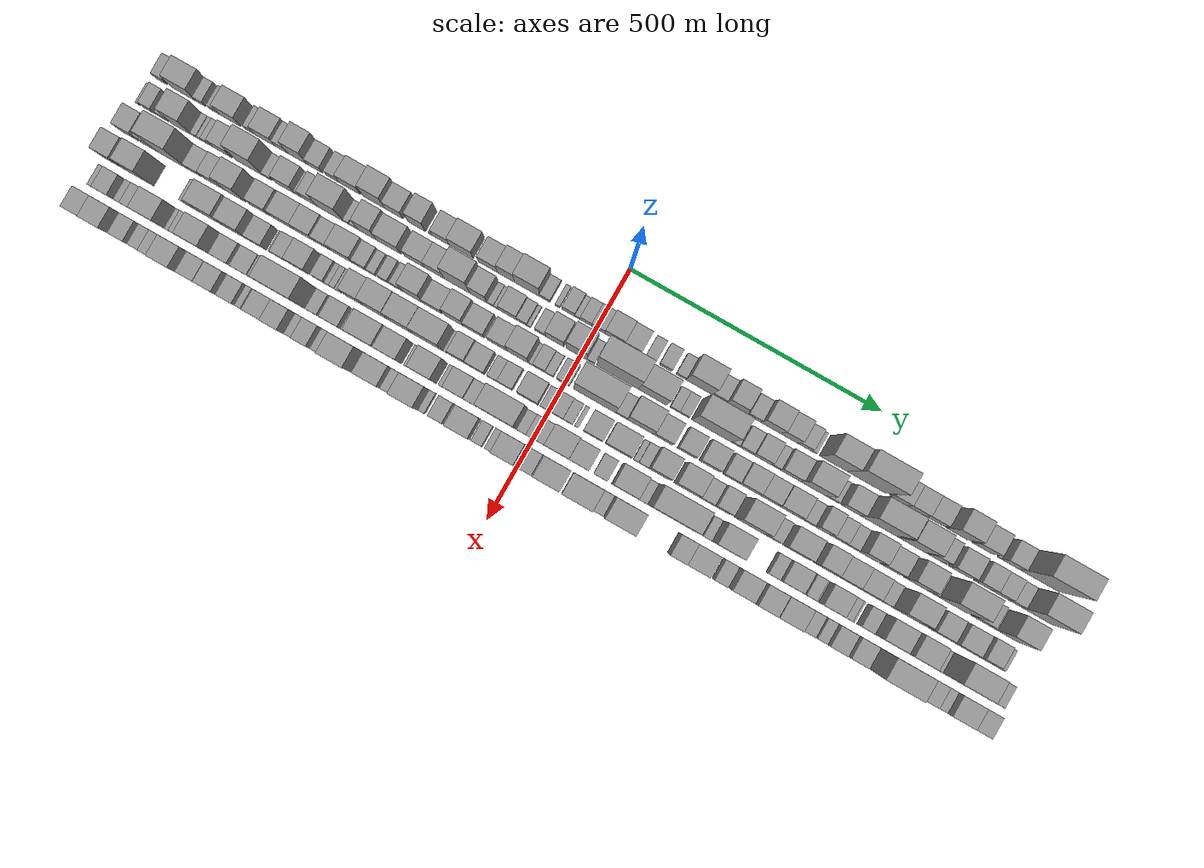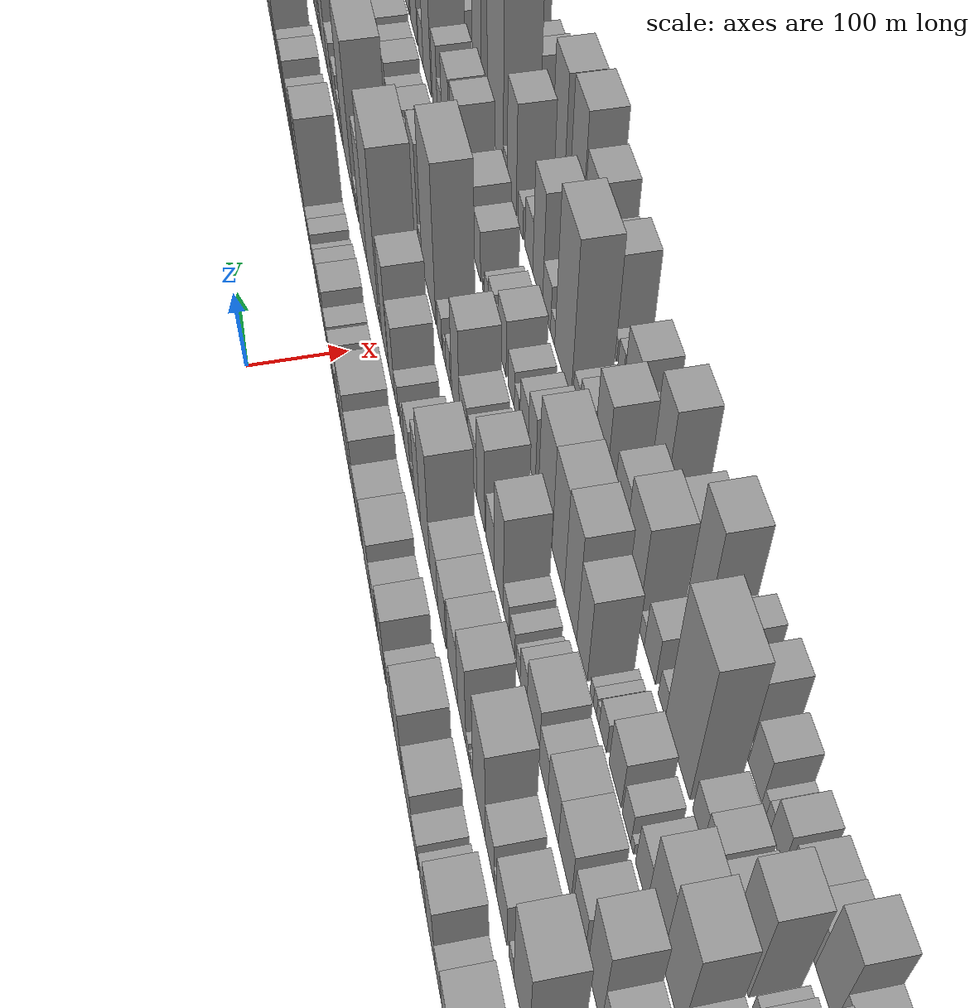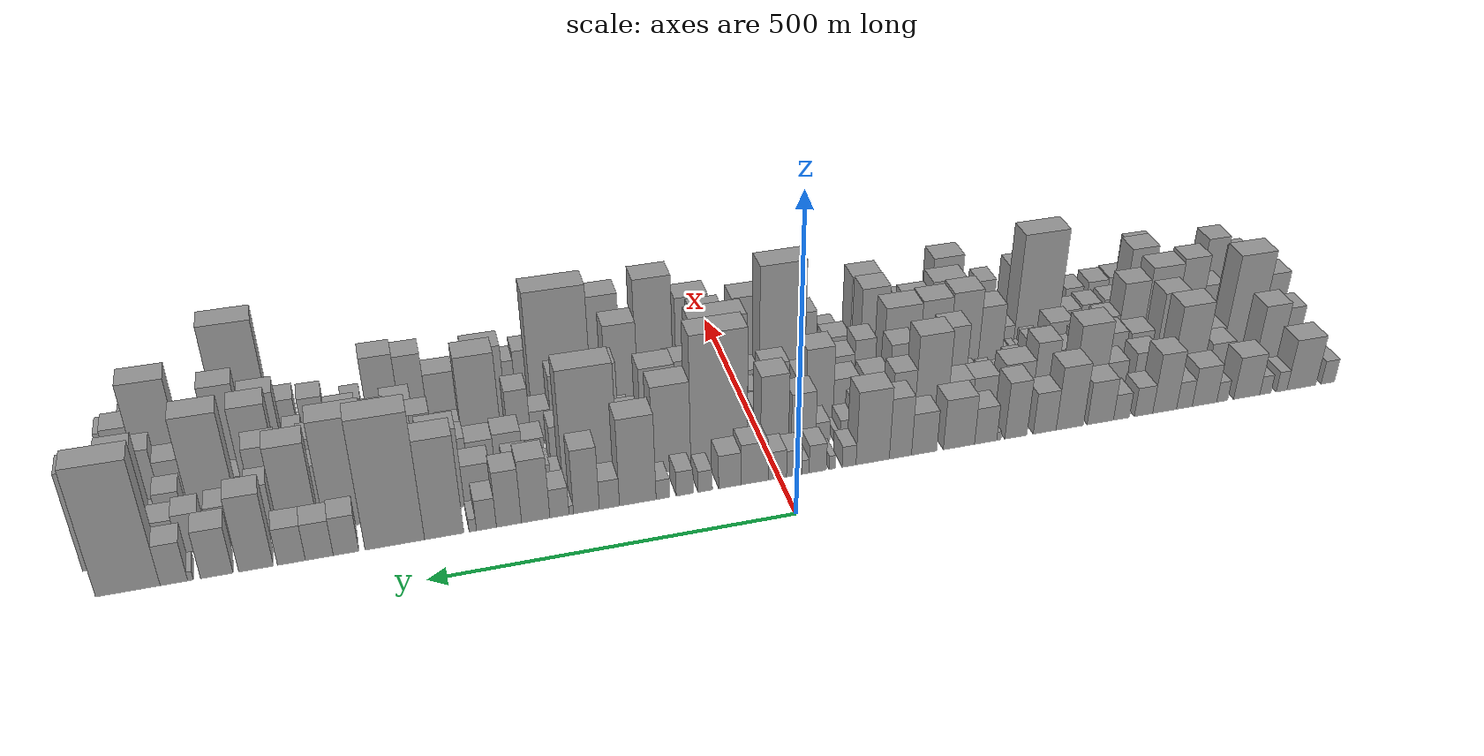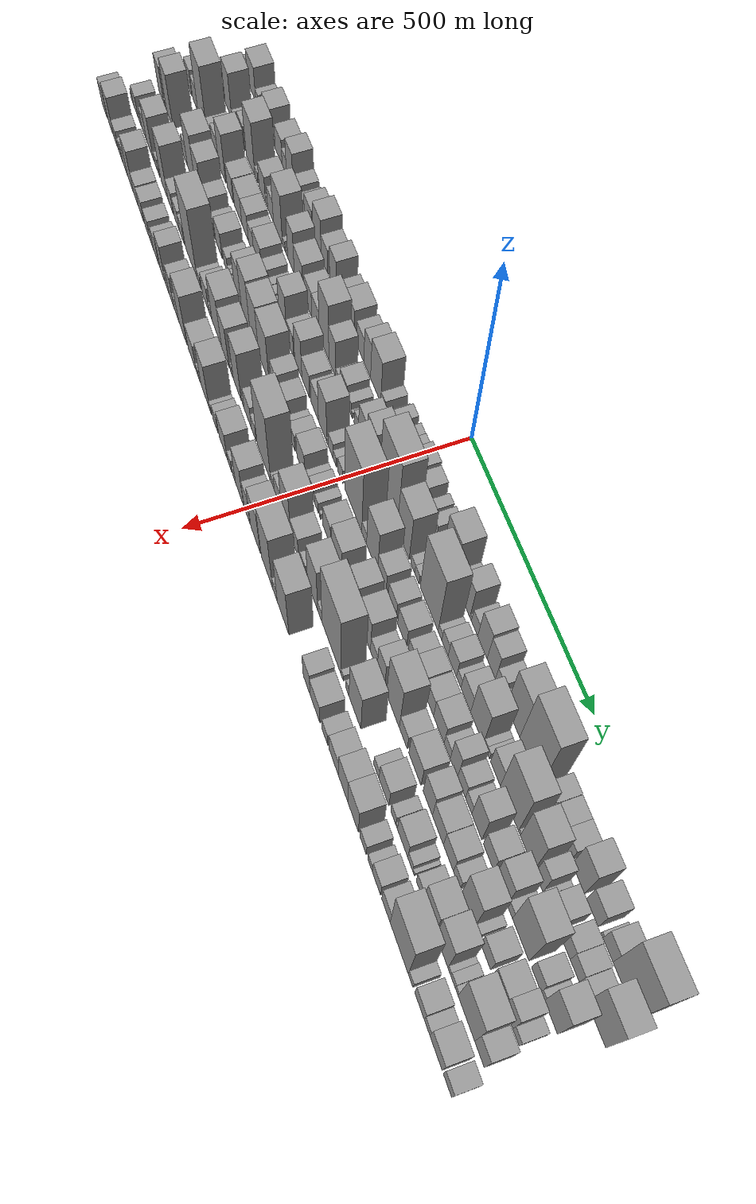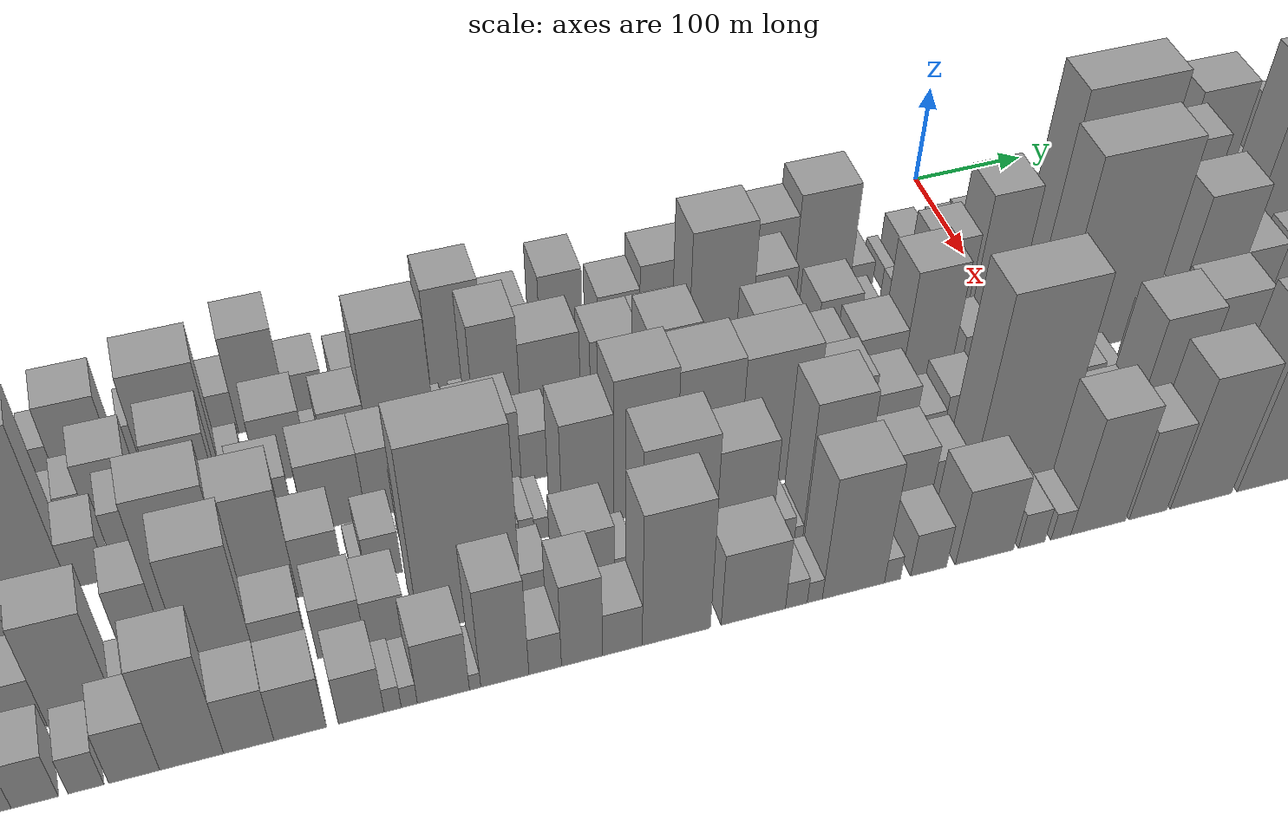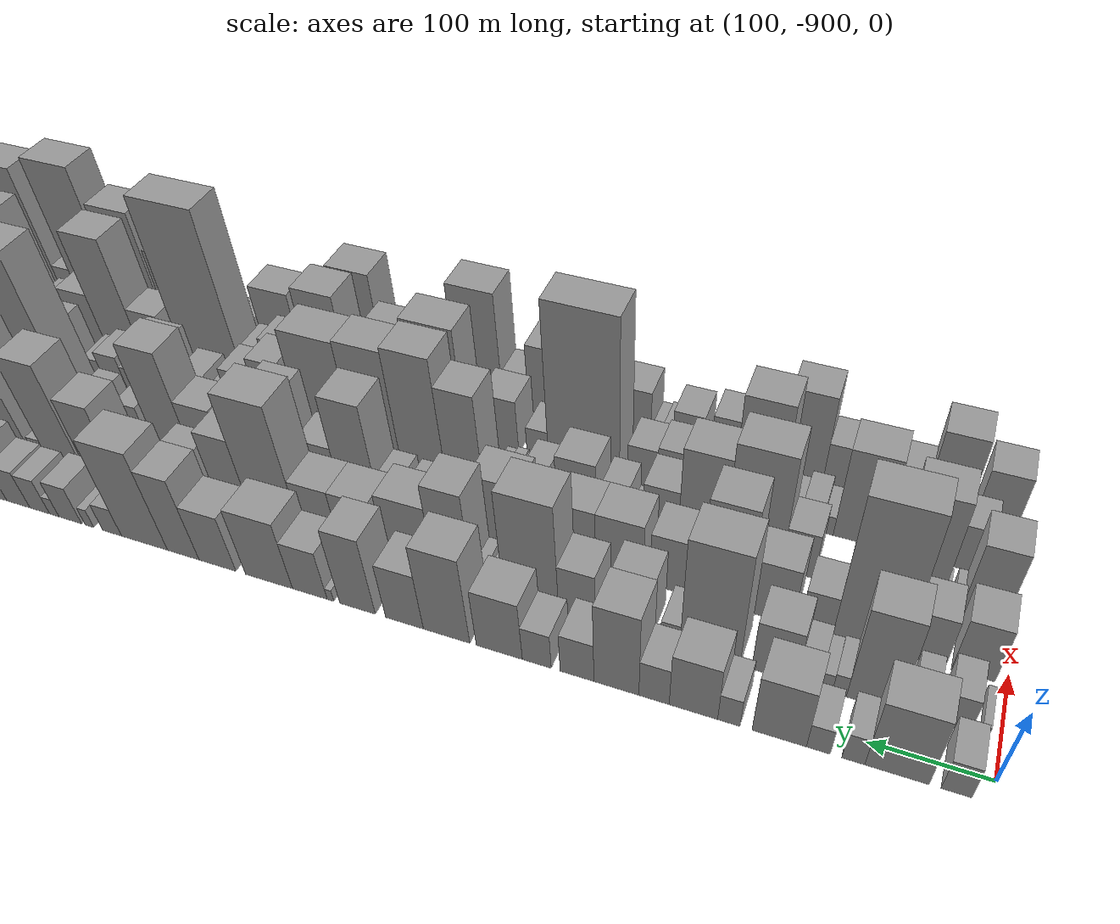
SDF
<sdf version="1.6">
 <world name="default">
  <scene>
   <sky><clouds><speed>12</speed></clouds></sky>
   <ambient>0.4 0.4 0.4 1</ambient>
   <background>0.7 0.7 0.7 1</background>
   <shadows>1</shadows>
  </scene>
  <gravity>0 0 -9.8066</gravity>
  <magnetic_field>6e-06 2.3e-05 -4.2e-05</magnetic_field>
  <physics default="0" name="default_physics" type="ode">
   <ode>
    <solver>
     <type>quick</type>
     <iters>10</iters>
     <sor>1.0</sor>
     <use_dynamic_moi_rescaling>0</use_dynamic_moi_rescaling>
    </solver>
    <constraints>
     <cfm>0</cfm>
     <erp>0.2</erp>
     <contact_max_correcting_vel>100</contact_max_correcting_vel>
     <contact_surface_layer>0.001</contact_surface_layer>
    </constraints>
   </ode>
   <max_step_size>0.004</max_step_size>
   <real_time_factor>1</real_time_factor>
   <real_time_update_rate>250</real_time_update_rate>
  </physics>
  <light name="sun" type="directional">
   <pose>0 0 10 0 0 0</pose>
   <diffuse>0.8 0.8 0.8 1</diffuse>
   <specular>0.2 0.2 0.2 1</specular>
   <attenuation>
    <range>1000</range>
    <constant>0.9</constant>
    <linear>0.01</linear>
    <quadratic>0.001</quadratic>
   </attenuation>
   <direction>-0.5 0.1 -0.9</direction>
  </light>
  <model name="building_1">
   <static>1</static>
   <pose>100.0000 -872.4348 0 0.000000 0.000000 0.000000</pose>
   <link name="link">
    <pose>0 0 21.00 0 0 0</pose>
    <collision name="collision"><geometry><box><size>40.0000 23.1304 42.0000</size></box></geometry></collision>
    <visual name="visual">
     <cast_shadows>0</cast_shadows>
     <geometry><box><size>40.0000 23.1304 42.0000</size></box></geometry>
     <material>
      <script>
       <uri>model://grey_wall/materials/scripts</uri>
       <uri>model://grey_wall/materials/textures</uri>
       <name>vrc/grey_wall</name>
      </script>
     </material>
    </visual>
   </link>
  </model>
  <model name="building_2">
   <static>1</static>
   <pose>100.0000 -827.0367 0 0.000000 0.000000 0.000000</pose>
   <link name="link">
    <pose>0 0 45.00 0 0 0</pose>
    <collision name="collision"><geometry><box><size>40.0000 49.6659 90.0000</size></box></geometry></collision>
    <visual name="visual">
     <cast_shadows>0</cast_shadows>
     <geometry><box><size>40.0000 49.6659 90.0000</size></box></geometry>
     <material>
      <script>
       <uri>model://grey_wall/materials/scripts</uri>
       <uri>model://grey_wall/materials/textures</uri>
       <name>vrc/grey_wall</name>
      </script>
     </material>
    </visual>
   </link>
  </model>
  <model name="building_3">
   <static>1</static>
   <pose>100.0000 -793.1880 0 0.000000 0.000000 0.000000</pose>
   <link name="link">
    <pose>0 0 18.00 0 0 0</pose>
    <collision name="collision"><geometry><box><size>40.0000 18.0314 36.0000</size></box></geometry></collision>
    <visual name="visual">
     <cast_shadows>0</cast_shadows>
     <geometry><box><size>40.0000 18.0314 36.0000</size></box></geometry>
     <material>
      <script>
       <uri>model://grey_wall/materials/scripts</uri>
       <uri>model://grey_wall/materials/textures</uri>
       <name>vrc/grey_wall</name>
      </script>
     </material>
    </visual>
   </link>
  </model>
  <model name="building_4">
   <static>1</static>
   <pose>100.0000 -765.6844 0 0.000000 0.000000 0.000000</pose>
   <link name="link">
    <pose>0 0 16.50 0 0 0</pose>
    <collision name="collision"><geometry><box><size>40.0000 18.9759 33.0000</size></box></geometry></collision>
    <visual name="visual">
     <cast_shadows>0</cast_shadows>
     <geometry><box><size>40.0000 18.9759 33.0000</size></box></geometry>
     <material>
      <script>
       <uri>model://grey_wall/materials/scripts</uri>
       <uri>model://grey_wall/materials/textures</uri>
       <name>vrc/grey_wall</name>
      </script>
     </material>
    </visual>
   </link>
  </model>
  <model name="building_5">
   <static>1</static>
   <pose>100.0000 -734.1484 0 0.000000 0.000000 0.000000</pose>
   <link name="link">
    <pose>0 0 37.50 0 0 0</pose>
    <collision name="collision"><geometry><box><size>40.0000 44.0961 75.0000</size></box></geometry></collision>
    <visual name="visual">
     <cast_shadows>0</cast_shadows>
     <geometry><box><size>40.0000 44.0961 75.0000</size></box></geometry>
     <material>
      <script>
       <uri>model://grey_wall/materials/scripts</uri>
       <uri>model://grey_wall/materials/textures</uri>
       <name>vrc/grey_wall</name>
      </script>
     </material>
    </visual>
   </link>
  </model>
  <model name="building_6">
   <static>1</static>
   <pose>100.0000 -692.8843 0 0.000000 0.000000 0.000000</pose>
   <link name="link">
    <pose>0 0 18.00 0 0 0</pose>
    <collision name="collision"><geometry><box><size>40.0000 18.4320 36.0000</size></box></geometry></collision>
    <visual name="visual">
     <cast_shadows>0</cast_shadows>
     <geometry><box><size>40.0000 18.4320 36.0000</size></box></geometry>
     <material>
      <script>
       <uri>model://grey_wall/materials/scripts</uri>
       <uri>model://grey_wall/materials/textures</uri>
       <name>vrc/grey_wall</name>
      </script>
     </material>
    </visual>
   </link>
  </model>
  <model name="building_7">
   <static>1</static>
   <pose>100.0000 -663.2856 0 0.000000 0.000000 0.000000</pose>
   <link name="link">
    <pose>0 0 34.50 0 0 0</pose>
    <collision name="collision"><geometry><box><size>40.0000 40.7653 69.0000</size></box></geometry></collision>
    <visual name="visual">
     <cast_shadows>0</cast_shadows>
     <geometry><box><size>40.0000 40.7653 69.0000</size></box></geometry>
     <material>
      <script>
       <uri>model://grey_wall/materials/scripts</uri>
       <uri>model://grey_wall/materials/textures</uri>
       <name>vrc/grey_wall</name>
      </script>
     </material>
    </visual>
   </link>
  </model>
  <model name="building_8">
   <static>1</static>
   <pose>100.0000 -629.9261 0 0.000000 0.000000 0.000000</pose>
   <link name="link">
    <pose>0 0 24.00 0 0 0</pose>
    <collision name="collision"><geometry><box><size>40.0000 25.9536 48.0000</size></box></geometry></collision>
    <visual name="visual">
     <cast_shadows>0</cast_shadows>
     <geometry><box><size>40.0000 25.9536 48.0000</size></box></geometry>
     <material>
      <script>
       <uri>model://grey_wall/materials/scripts</uri>
       <uri>model://grey_wall/materials/textures</uri>
       <name>vrc/grey_wall</name>
      </script>
     </material>
    </visual>
   </link>
  </model>
  <model name="building_9">
   <static>1</static>
   <pose>100.0000 -597.4305 0 0.000000 0.000000 0.000000</pose>
   <link name="link">
    <pose>0 0 52.50 0 0 0</pose>
    <collision name="collision"><geometry><box><size>40.0000 39.0376 105.0000</size></box></geometry></collision>
    <visual name="visual">
     <cast_shadows>0</cast_shadows>
     <geometry><box><size>40.0000 39.0376 105.0000</size></box></geometry>
     <material>
      <script>
       <uri>model://grey_wall/materials/scripts</uri>
       <uri>model://grey_wall/materials/textures</uri>
       <name>vrc/grey_wall</name>
      </script>
     </material>
    </visual>
   </link>
  </model>
  <model name="building_10">
   <static>1</static>
   <pose>100.0000 -562.9785 0 0.000000 0.000000 0.000000</pose>
   <link name="link">
    <pose>0 0 25.50 0 0 0</pose>
    <collision name="collision"><geometry><box><size>40.0000 29.8665 51.0000</size></box></geometry></collision>
    <visual name="visual">
     <cast_shadows>0</cast_shadows>
     <geometry><box><size>40.0000 29.8665 51.0000</size></box></geometry>
     <material>
      <script>
       <uri>model://grey_wall/materials/scripts</uri>
       <uri>model://grey_wall/materials/textures</uri>
       <name>vrc/grey_wall</name>
      </script>
     </material>
    </visual>
   </link>
  </model>
  <model name="building_11">
   <static>1</static>
   <pose>100.0000 -527.0309 0 0.000000 0.000000 0.000000</pose>
   <link name="link">
    <pose>0 0 22.50 0 0 0</pose>
    <collision name="collision"><geometry><box><size>40.0000 26.0288 45.0000</size></box></geometry></collision>
    <visual name="visual">
     <cast_shadows>0</cast_shadows>
     <geometry><box><size>40.0000 26.0288 45.0000</size></box></geometry>
     <material>
      <script>
       <uri>model://grey_wall/materials/scripts</uri>
       <uri>model://grey_wall/materials/textures</uri>
       <name>vrc/grey_wall</name>
      </script>
     </material>
    </visual>
   </link>
  </model>
  <model name="building_12">
   <static>1</static>
   <pose>100.0000 -492.8909 0 0.000000 0.000000 0.000000</pose>
   <link name="link">
    <pose>0 0 37.50 0 0 0</pose>
    <collision name="collision"><geometry><box><size>40.0000 42.2512 75.0000</size></box></geometry></collision>
    <visual name="visual">
     <cast_shadows>0</cast_shadows>
     <geometry><box><size>40.0000 42.2512 75.0000</size></box></geometry>
     <material>
      <script>
       <uri>model://grey_wall/materials/scripts</uri>
       <uri>model://grey_wall/materials/textures</uri>
       <name>vrc/grey_wall</name>
      </script>
     </material>
    </visual>
   </link>
  </model>
  <model name="building_13">
   <static>1</static>
   <pose>100.0000 -443.9070 0 0.000000 0.000000 0.000000</pose>
   <link name="link">
    <pose>0 0 55.50 0 0 0</pose>
    <collision name="collision"><geometry><box><size>40.0000 43.7164 111.0000</size></box></geometry></collision>
    <visual name="visual">
     <cast_shadows>0</cast_shadows>
     <geometry><box><size>40.0000 43.7164 111.0000</size></box></geometry>
     <material>
      <script>
       <uri>model://grey_wall/materials/scripts</uri>
       <uri>model://grey_wall/materials/textures</uri>
       <name>vrc/grey_wall</name>
      </script>
     </material>
    </visual>
   </link>
  </model>
  <model name="building_14">
   <static>1</static>
   <pose>100.0000 -403.9635 0 0.000000 0.000000 0.000000</pose>
   <link name="link">
    <pose>0 0 36.00 0 0 0</pose>
    <collision name="collision"><geometry><box><size>40.0000 36.1706 72.0000</size></box></geometry></collision>
    <visual name="visual">
     <cast_shadows>0</cast_shadows>
     <geometry><box><size>40.0000 36.1706 72.0000</size></box></geometry>
     <material>
      <script>
       <uri>model://grey_wall/materials/scripts</uri>
       <uri>model://grey_wall/materials/textures</uri>
       <name>vrc/grey_wall</name>
      </script>
     </material>
    </visual>
   </link>
  </model>
  <model name="building_15">
   <static>1</static>
   <pose>100.0000 -358.4672 0 0.000000 0.000000 0.000000</pose>
   <link name="link">
    <pose>0 0 49.50 0 0 0</pose>
    <collision name="collision"><geometry><box><size>40.0000 34.8221 99.0000</size></box></geometry></collision>
    <visual name="visual">
     <cast_shadows>0</cast_shadows>
     <geometry><box><size>40.0000 34.8221 99.0000</size></box></geometry>
     <material>
      <script>
       <uri>model://grey_wall/materials/scripts</uri>
       <uri>model://grey_wall/materials/textures</uri>
       <name>vrc/grey_wall</name>
      </script>
     </material>
    </visual>
   </link>
  </model>
  <model name="building_16">
   <static>1</static>
   <pose>100.0000 -331.7835 0 0.000000 0.000000 0.000000</pose>
   <link name="link">
    <pose>0 0 7.50 0 0 0</pose>
    <collision name="collision"><geometry><box><size>40.0000 6.5454 15.0000</size></box></geometry></collision>
    <visual name="visual">
     <cast_shadows>0</cast_shadows>
     <geometry><box><size>40.0000 6.5454 15.0000</size></box></geometry>
     <material>
      <script>
       <uri>model://grey_wall/materials/scripts</uri>
       <uri>model://grey_wall/materials/textures</uri>
       <name>vrc/grey_wall</name>
      </script>
     </material>
    </visual>
   </link>
  </model>
  <model name="building_17">
   <static>1</static>
   <pose>100.0000 -311.1654 0 0.000000 0.000000 0.000000</pose>
   <link name="link">
    <pose>0 0 31.50 0 0 0</pose>
    <collision name="collision"><geometry><box><size>40.0000 34.6909 63.0000</size></box></geometry></collision>
    <visual name="visual">
     <cast_shadows>0</cast_shadows>
     <geometry><box><size>40.0000 34.6909 63.0000</size></box></geometry>
     <material>
      <script>
       <uri>model://grey_wall/materials/scripts</uri>
       <uri>model://grey_wall/materials/textures</uri>
       <name>vrc/grey_wall</name>
      </script>
     </material>
    </visual>
   </link>
  </model>
  <model name="building_18">
   <static>1</static>
   <pose>100.0000 -269.7449 0 0.000000 0.000000 0.000000</pose>
   <link name="link">
    <pose>0 0 43.50 0 0 0</pose>
    <collision name="collision"><geometry><box><size>40.0000 48.1501 87.0000</size></box></geometry></collision>
    <visual name="visual">
     <cast_shadows>0</cast_shadows>
     <geometry><box><size>40.0000 48.1501 87.0000</size></box></geometry>
     <material>
      <script>
       <uri>model://grey_wall/materials/scripts</uri>
       <uri>model://grey_wall/materials/textures</uri>
       <name>vrc/grey_wall</name>
      </script>
     </material>
    </visual>
   </link>
  </model>
  <model name="building_19">
   <static>1</static>
   <pose>100.0000 -216.3100 0 0.000000 0.000000 0.000000</pose>
   <link name="link">
    <pose>0 0 36.00 0 0 0</pose>
    <collision name="collision"><geometry><box><size>40.0000 38.7197 72.0000</size></box></geometry></collision>
    <visual name="visual">
     <cast_shadows>0</cast_shadows>
     <geometry><box><size>40.0000 38.7197 72.0000</size></box></geometry>
     <material>
      <script>
       <uri>model://grey_wall/materials/scripts</uri>
       <uri>model://grey_wall/materials/textures</uri>
       <name>vrc/grey_wall</name>
      </script>
     </material>
    </visual>
   </link>
  </model>
  <model name="building_20">
   <static>1</static>
   <pose>100.0000 -180.1216 0 0.000000 0.000000 0.000000</pose>
   <link name="link">
    <pose>0 0 52.50 0 0 0</pose>
    <collision name="collision"><geometry><box><size>40.0000 33.6571 105.0000</size></box></geometry></collision>
    <visual name="visual">
     <cast_shadows>0</cast_shadows>
     <geometry><box><size>40.0000 33.6571 105.0000</size></box></geometry>
     <material>
      <script>
       <uri>model://grey_wall/materials/scripts</uri>
       <uri>model://grey_wall/materials/textures</uri>
       <name>vrc/grey_wall</name>
      </script>
     </material>
    </visual>
   </link>
  </model>
  <model name="building_21">
   <static>1</static>
   <pose>100.0000 -138.2085 0 0.000000 0.000000 0.000000</pose>
   <link name="link">
    <pose>0 0 63.00 0 0 0</pose>
    <collision name="collision"><geometry><box><size>40.0000 50.1690 126.0000</size></box></geometry></collision>
    <visual name="visual">
     <cast_shadows>0</cast_shadows>
     <geometry><box><size>40.0000 50.1690 126.0000</size></box></geometry>
     <material>
      <script>
       <uri>model://grey_wall/materials/scripts</uri>
       <uri>model://grey_wall/materials/textures</uri>
       <name>vrc/grey_wall</name>
      </script>
     </material>
    </visual>
   </link>
  </model>
  <model name="building_22">
   <static>1</static>
   <pose>100.0000 -102.7595 0 0.000000 0.000000 0.000000</pose>
   <link name="link">
    <pose>0 0 18.00 0 0 0</pose>
    <collision name="collision"><geometry><box><size>40.0000 20.7290 36.0000</size></box></geometry></collision>
    <visual name="visual">
     <cast_shadows>0</cast_shadows>
     <geometry><box><size>40.0000 20.7290 36.0000</size></box></geometry>
     <material>
      <script>
       <uri>model://grey_wall/materials/scripts</uri>
       <uri>model://grey_wall/materials/textures</uri>
       <name>vrc/grey_wall</name>
      </script>
     </material>
    </visual>
   </link>
  </model>
  <model name="building_23">
   <static>1</static>
   <pose>100.0000 -77.5715 0 0.000000 0.000000 0.000000</pose>
   <link name="link">
    <pose>0 0 12.00 0 0 0</pose>
    <collision name="collision"><geometry><box><size>40.0000 9.6469 24.0000</size></box></geometry></collision>
    <visual name="visual">
     <cast_shadows>0</cast_shadows>
     <geometry><box><size>40.0000 9.6469 24.0000</size></box></geometry>
     <material>
      <script>
       <uri>model://grey_wall/materials/scripts</uri>
       <uri>model://grey_wall/materials/textures</uri>
       <name>vrc/grey_wall</name>
      </script>
     </material>
    </visual>
   </link>
  </model>
  <model name="building_24">
   <static>1</static>
   <pose>100.0000 -55.9709 0 0.000000 0.000000 0.000000</pose>
   <link name="link">
    <pose>0 0 24.00 0 0 0</pose>
    <collision name="collision"><geometry><box><size>40.0000 25.5543 48.0000</size></box></geometry></collision>
    <visual name="visual">
     <cast_shadows>0</cast_shadows>
     <geometry><box><size>40.0000 25.5543 48.0000</size></box></geometry>
     <material>
      <script>
       <uri>model://grey_wall/materials/scripts</uri>
       <uri>model://grey_wall/materials/textures</uri>
       <name>vrc/grey_wall</name>
      </script>
     </material>
    </visual>
   </link>
  </model>
  <model name="building_25">
   <static>1</static>
   <pose>100.0000 -37.8460 0 0.000000 0.000000 0.000000</pose>
   <link name="link">
    <pose>0 0 12.00 0 0 0</pose>
    <collision name="collision"><geometry><box><size>40.0000 10.6956 24.0000</size></box></geometry></collision>
    <visual name="visual">
     <cast_shadows>0</cast_shadows>
     <geometry><box><size>40.0000 10.6956 24.0000</size></box></geometry>
     <material>
      <script>
       <uri>model://grey_wall/materials/scripts</uri>
       <uri>model://grey_wall/materials/textures</uri>
       <name>vrc/grey_wall</name>
      </script>
     </material>
    </visual>
   </link>
  </model>
  <model name="building_26">
   <static>1</static>
   <pose>100.0000 -21.2353 0 0.000000 0.000000 0.000000</pose>
   <link name="link">
    <pose>0 0 22.50 0 0 0</pose>
    <collision name="collision"><geometry><box><size>40.0000 22.5257 45.0000</size></box></geometry></collision>
    <visual name="visual">
     <cast_shadows>0</cast_shadows>
     <geometry><box><size>40.0000 22.5257 45.0000</size></box></geometry>
     <material>
      <script>
       <uri>model://grey_wall/materials/scripts</uri>
       <uri>model://grey_wall/materials/textures</uri>
       <name>vrc/grey_wall</name>
      </script>
     </material>
    </visual>
   </link>
  </model>
  <model name="building_27">
   <static>1</static>
   <pose>100.0000 3.4044 0 0.000000 0.000000 0.000000</pose>
   <link name="link">
    <pose>0 0 24.00 0 0 0</pose>
    <collision name="collision"><geometry><box><size>40.0000 26.7537 48.0000</size></box></geometry></collision>
    <visual name="visual">
     <cast_shadows>0</cast_shadows>
     <geometry><box><size>40.0000 26.7537 48.0000</size></box></geometry>
     <material>
      <script>
       <uri>model://grey_wall/materials/scripts</uri>
       <uri>model://grey_wall/materials/textures</uri>
       <name>vrc/grey_wall</name>
      </script>
     </material>
    </visual>
   </link>
  </model>
  <model name="building_28">
   <static>1</static>
   <pose>100.0000 36.5227 0 0.000000 0.000000 0.000000</pose>
   <link name="link">
    <pose>0 0 34.50 0 0 0</pose>
    <collision name="collision"><geometry><box><size>40.0000 39.4829 69.0000</size></box></geometry></collision>
    <visual name="visual">
     <cast_shadows>0</cast_shadows>
     <geometry><box><size>40.0000 39.4829 69.0000</size></box></geometry>
     <material>
      <script>
       <uri>model://grey_wall/materials/scripts</uri>
       <uri>model://grey_wall/materials/textures</uri>
       <name>vrc/grey_wall</name>
      </script>
     </material>
    </visual>
   </link>
  </model>
  <model name="building_29">
   <static>1</static>
   <pose>100.0000 72.4692 0 0.000000 0.000000 0.000000</pose>
   <link name="link">
    <pose>0 0 28.50 0 0 0</pose>
    <collision name="collision"><geometry><box><size>40.0000 32.4100 57.0000</size></box></geometry></collision>
    <visual name="visual">
     <cast_shadows>0</cast_shadows>
     <geometry><box><size>40.0000 32.4100 57.0000</size></box></geometry>
     <material>
      <script>
       <uri>model://grey_wall/materials/scripts</uri>
       <uri>model://grey_wall/materials/textures</uri>
       <name>vrc/grey_wall</name>
      </script>
     </material>
    </visual>
   </link>
  </model>
  <model name="building_30">
   <static>1</static>
   <pose>100.0000 107.8525 0 0.000000 0.000000 0.000000</pose>
   <link name="link">
    <pose>0 0 18.00 0 0 0</pose>
    <collision name="collision"><geometry><box><size>40.0000 20.3566 36.0000</size></box></geometry></collision>
    <visual name="visual">
     <cast_shadows>0</cast_shadows>
     <geometry><box><size>40.0000 20.3566 36.0000</size></box></geometry>
     <material>
      <script>
       <uri>model://grey_wall/materials/scripts</uri>
       <uri>model://grey_wall/materials/textures</uri>
       <name>vrc/grey_wall</name>
      </script>
     </material>
    </visual>
   </link>
  </model>
  <model name="building_31">
   <static>1</static>
   <pose>100.0000 137.2129 0 0.000000 0.000000 0.000000</pose>
   <link name="link">
    <pose>0 0 21.00 0 0 0</pose>
    <collision name="collision"><geometry><box><size>40.0000 24.3643 42.0000</size></box></geometry></collision>
    <visual name="visual">
     <cast_shadows>0</cast_shadows>
     <geometry><box><size>40.0000 24.3643 42.0000</size></box></geometry>
     <material>
      <script>
       <uri>model://grey_wall/materials/scripts</uri>
       <uri>model://grey_wall/materials/textures</uri>
       <name>vrc/grey_wall</name>
      </script>
     </material>
    </visual>
   </link>
  </model>
  <model name="building_32">
   <static>1</static>
   <pose>100.0000 168.2064 0 0.000000 0.000000 0.000000</pose>
   <link name="link">
    <pose>0 0 16.50 0 0 0</pose>
    <collision name="collision"><geometry><box><size>40.0000 19.6229 33.0000</size></box></geometry></collision>
    <visual name="visual">
     <cast_shadows>0</cast_shadows>
     <geometry><box><size>40.0000 19.6229 33.0000</size></box></geometry>
     <material>
      <script>
       <uri>model://grey_wall/materials/scripts</uri>
       <uri>model://grey_wall/materials/textures</uri>
       <name>vrc/grey_wall</name>
      </script>
     </material>
    </visual>
   </link>
  </model>
  <model name="building_33">
   <static>1</static>
   <pose>100.0000 203.8029 0 0.000000 0.000000 0.000000</pose>
   <link name="link">
    <pose>0 0 73.50 0 0 0</pose>
    <collision name="collision"><geometry><box><size>40.0000 51.5702 147.0000</size></box></geometry></collision>
    <visual name="visual">
     <cast_shadows>0</cast_shadows>
     <geometry><box><size>40.0000 51.5702 147.0000</size></box></geometry>
     <material>
      <script>
       <uri>model://grey_wall/materials/scripts</uri>
       <uri>model://grey_wall/materials/textures</uri>
       <name>vrc/grey_wall</name>
      </script>
     </material>
    </visual>
   </link>
  </model>
  <model name="building_34">
   <static>1</static>
   <pose>100.0000 243.6097 0 0.000000 0.000000 0.000000</pose>
   <link name="link">
    <pose>0 0 24.00 0 0 0</pose>
    <collision name="collision"><geometry><box><size>40.0000 28.0434 48.0000</size></box></geometry></collision>
    <visual name="visual">
     <cast_shadows>0</cast_shadows>
     <geometry><box><size>40.0000 28.0434 48.0000</size></box></geometry>
     <material>
      <script>
       <uri>model://grey_wall/materials/scripts</uri>
       <uri>model://grey_wall/materials/textures</uri>
       <name>vrc/grey_wall</name>
      </script>
     </material>
    </visual>
   </link>
  </model>
  <model name="building_35">
   <static>1</static>
   <pose>100.0000 275.5706 0 0.000000 0.000000 0.000000</pose>
   <link name="link">
    <pose>0 0 54.00 0 0 0</pose>
    <collision name="collision"><geometry><box><size>40.0000 35.8784 108.0000</size></box></geometry></collision>
    <visual name="visual">
     <cast_shadows>0</cast_shadows>
     <geometry><box><size>40.0000 35.8784 108.0000</size></box></geometry>
     <material>
      <script>
       <uri>model://grey_wall/materials/scripts</uri>
       <uri>model://grey_wall/materials/textures</uri>
       <name>vrc/grey_wall</name>
      </script>
     </material>
    </visual>
   </link>
  </model>
  <model name="building_36">
   <static>1</static>
   <pose>100.0000 296.6218 0 0.000000 0.000000 0.000000</pose>
   <link name="link">
    <pose>0 0 7.50 0 0 0</pose>
    <collision name="collision"><geometry><box><size>40.0000 6.2238 15.0000</size></box></geometry></collision>
    <visual name="visual">
     <cast_shadows>0</cast_shadows>
     <geometry><box><size>40.0000 6.2238 15.0000</size></box></geometry>
     <material>
      <script>
       <uri>model://grey_wall/materials/scripts</uri>
       <uri>model://grey_wall/materials/textures</uri>
       <name>vrc/grey_wall</name>
      </script>
     </material>
    </visual>
   </link>
  </model>
  <model name="building_37">
   <static>1</static>
   <pose>100.0000 312.8875 0 0.000000 0.000000 0.000000</pose>
   <link name="link">
    <pose>0 0 24.00 0 0 0</pose>
    <collision name="collision"><geometry><box><size>40.0000 26.3076 48.0000</size></box></geometry></collision>
    <visual name="visual">
     <cast_shadows>0</cast_shadows>
     <geometry><box><size>40.0000 26.3076 48.0000</size></box></geometry>
     <material>
      <script>
       <uri>model://grey_wall/materials/scripts</uri>
       <uri>model://grey_wall/materials/textures</uri>
       <name>vrc/grey_wall</name>
      </script>
     </material>
    </visual>
   </link>
  </model>
  <model name="building_38">
   <static>1</static>
   <pose>100.0000 345.4138 0 0.000000 0.000000 0.000000</pose>
   <link name="link">
    <pose>0 0 52.50 0 0 0</pose>
    <collision name="collision"><geometry><box><size>40.0000 38.7450 105.0000</size></box></geometry></collision>
    <visual name="visual">
     <cast_shadows>0</cast_shadows>
     <geometry><box><size>40.0000 38.7450 105.0000</size></box></geometry>
     <material>
      <script>
       <uri>model://grey_wall/materials/scripts</uri>
       <uri>model://grey_wall/materials/textures</uri>
       <name>vrc/grey_wall</name>
      </script>
     </material>
    </visual>
   </link>
  </model>
  <model name="building_39">
   <static>1</static>
   <pose>100.0000 381.8537 0 0.000000 0.000000 0.000000</pose>
   <link name="link">
    <pose>0 0 46.50 0 0 0</pose>
    <collision name="collision"><geometry><box><size>40.0000 34.1349 93.0000</size></box></geometry></collision>
    <visual name="visual">
     <cast_shadows>0</cast_shadows>
     <geometry><box><size>40.0000 34.1349 93.0000</size></box></geometry>
     <material>
      <script>
       <uri>model://grey_wall/materials/scripts</uri>
       <uri>model://grey_wall/materials/textures</uri>
       <name>vrc/grey_wall</name>
      </script>
     </material>
    </visual>
   </link>
  </model>
  <model name="building_40">
   <static>1</static>
   <pose>100.0000 412.3421 0 0.000000 0.000000 0.000000</pose>
   <link name="link">
    <pose>0 0 25.50 0 0 0</pose>
    <collision name="collision"><geometry><box><size>40.0000 26.8418 51.0000</size></box></geometry></collision>
    <visual name="visual">
     <cast_shadows>0</cast_shadows>
     <geometry><box><size>40.0000 26.8418 51.0000</size></box></geometry>
     <material>
      <script>
       <uri>model://grey_wall/materials/scripts</uri>
       <uri>model://grey_wall/materials/textures</uri>
       <name>vrc/grey_wall</name>
      </script>
     </material>
    </visual>
   </link>
  </model>
  <model name="building_41">
   <static>1</static>
   <pose>100.0000 430.7759 0 0.000000 0.000000 0.000000</pose>
   <link name="link">
    <pose>0 0 10.50 0 0 0</pose>
    <collision name="collision"><geometry><box><size>40.0000 10.0258 21.0000</size></box></geometry></collision>
    <visual name="visual">
     <cast_shadows>0</cast_shadows>
     <geometry><box><size>40.0000 10.0258 21.0000</size></box></geometry>
     <material>
      <script>
       <uri>model://grey_wall/materials/scripts</uri>
       <uri>model://grey_wall/materials/textures</uri>
       <name>vrc/grey_wall</name>
      </script>
     </material>
    </visual>
   </link>
  </model>
  <model name="building_42">
   <static>1</static>
   <pose>100.0000 468.9980 0 0.000000 0.000000 0.000000</pose>
   <link name="link">
    <pose>0 0 82.50 0 0 0</pose>
    <collision name="collision"><geometry><box><size>40.0000 52.4184 165.0000</size></box></geometry></collision>
    <visual name="visual">
     <cast_shadows>0</cast_shadows>
     <geometry><box><size>40.0000 52.4184 165.0000</size></box></geometry>
     <material>
      <script>
       <uri>model://grey_wall/materials/scripts</uri>
       <uri>model://grey_wall/materials/textures</uri>
       <name>vrc/grey_wall</name>
      </script>
     </material>
    </visual>
   </link>
  </model>
  <model name="building_43">
   <static>1</static>
   <pose>100.0000 534.4264 0 0.000000 0.000000 0.000000</pose>
   <link name="link">
    <pose>0 0 106.50 0 0 0</pose>
    <collision name="collision"><geometry><box><size>40.0000 78.4383 213.0000</size></box></geometry></collision>
    <visual name="visual">
     <cast_shadows>0</cast_shadows>
     <geometry><box><size>40.0000 78.4383 213.0000</size></box></geometry>
     <material>
      <script>
       <uri>model://grey_wall/materials/scripts</uri>
       <uri>model://grey_wall/materials/textures</uri>
       <name>vrc/grey_wall</name>
      </script>
     </material>
    </visual>
   </link>
  </model>
  <model name="building_44">
   <static>1</static>
   <pose>100.0000 598.2994 0 0.000000 0.000000 0.000000</pose>
   <link name="link">
    <pose>0 0 31.50 0 0 0</pose>
    <collision name="collision"><geometry><box><size>40.0000 33.3076 63.0000</size></box></geometry></collision>
    <visual name="visual">
     <cast_shadows>0</cast_shadows>
     <geometry><box><size>40.0000 33.3076 63.0000</size></box></geometry>
     <material>
      <script>
       <uri>model://grey_wall/materials/scripts</uri>
       <uri>model://grey_wall/materials/textures</uri>
       <name>vrc/grey_wall</name>
      </script>
     </material>
    </visual>
   </link>
  </model>
  <model name="building_45">
   <static>1</static>
   <pose>100.0000 632.9223 0 0.000000 0.000000 0.000000</pose>
   <link name="link">
    <pose>0 0 30.00 0 0 0</pose>
    <collision name="collision"><geometry><box><size>40.0000 35.9383 60.0000</size></box></geometry></collision>
    <visual name="visual">
     <cast_shadows>0</cast_shadows>
     <geometry><box><size>40.0000 35.9383 60.0000</size></box></geometry>
     <material>
      <script>
       <uri>model://grey_wall/materials/scripts</uri>
       <uri>model://grey_wall/materials/textures</uri>
       <name>vrc/grey_wall</name>
      </script>
     </material>
    </visual>
   </link>
  </model>
  <model name="building_46">
   <static>1</static>
   <pose>100.0000 668.8182 0 0.000000 0.000000 0.000000</pose>
   <link name="link">
    <pose>0 0 30.00 0 0 0</pose>
    <collision name="collision"><geometry><box><size>40.0000 35.8536 60.0000</size></box></geometry></collision>
    <visual name="visual">
     <cast_shadows>0</cast_shadows>
     <geometry><box><size>40.0000 35.8536 60.0000</size></box></geometry>
     <material>
      <script>
       <uri>model://grey_wall/materials/scripts</uri>
       <uri>model://grey_wall/materials/textures</uri>
       <name>vrc/grey_wall</name>
      </script>
     </material>
    </visual>
   </link>
  </model>
  <model name="building_47">
   <static>1</static>
   <pose>100.0000 713.8570 0 0.000000 0.000000 0.000000</pose>
   <link name="link">
    <pose>0 0 61.50 0 0 0</pose>
    <collision name="collision"><geometry><box><size>40.0000 44.2238 123.0000</size></box></geometry></collision>
    <visual name="visual">
     <cast_shadows>0</cast_shadows>
     <geometry><box><size>40.0000 44.2238 123.0000</size></box></geometry>
     <material>
      <script>
       <uri>model://grey_wall/materials/scripts</uri>
       <uri>model://grey_wall/materials/textures</uri>
       <name>vrc/grey_wall</name>
      </script>
     </material>
    </visual>
   </link>
  </model>
  <model name="building_48">
   <static>1</static>
   <pose>100.0000 763.4033 0 0.000000 0.000000 0.000000</pose>
   <link name="link">
    <pose>0 0 39.00 0 0 0</pose>
    <collision name="collision"><geometry><box><size>40.0000 40.8688 78.0000</size></box></geometry></collision>
    <visual name="visual">
     <cast_shadows>0</cast_shadows>
     <geometry><box><size>40.0000 40.8688 78.0000</size></box></geometry>
     <material>
      <script>
       <uri>model://grey_wall/materials/scripts</uri>
       <uri>model://grey_wall/materials/textures</uri>
       <name>vrc/grey_wall</name>
      </script>
     </material>
    </visual>
   </link>
  </model>
  <model name="building_49">
   <static>1</static>
   <pose>100.0000 796.3240 0 0.000000 0.000000 0.000000</pose>
   <link name="link">
    <pose>0 0 7.50 0 0 0</pose>
    <collision name="collision"><geometry><box><size>40.0000 6.9727 15.0000</size></box></geometry></collision>
    <visual name="visual">
     <cast_shadows>0</cast_shadows>
     <geometry><box><size>40.0000 6.9727 15.0000</size></box></geometry>
     <material>
      <script>
       <uri>model://grey_wall/materials/scripts</uri>
       <uri>model://grey_wall/materials/textures</uri>
       <name>vrc/grey_wall</name>
      </script>
     </material>
    </visual>
   </link>
  </model>
  <model name="building_50">
   <static>1</static>
   <pose>100.0000 816.8563 0 0.000000 0.000000 0.000000</pose>
   <link name="link">
    <pose>0 0 33.00 0 0 0</pose>
    <collision name="collision"><geometry><box><size>40.0000 34.0918 66.0000</size></box></geometry></collision>
    <visual name="visual">
     <cast_shadows>0</cast_shadows>
     <geometry><box><size>40.0000 34.0918 66.0000</size></box></geometry>
     <material>
      <script>
       <uri>model://grey_wall/materials/scripts</uri>
       <uri>model://grey_wall/materials/textures</uri>
       <name>vrc/grey_wall</name>
      </script>
     </material>
    </visual>
   </link>
  </model>
  <model name="building_51">
   <static>1</static>
   <pose>100.0000 873.5854 0 0.000000 0.000000 0.000000</pose>
   <link name="link">
    <pose>0 0 103.50 0 0 0</pose>
    <collision name="collision"><geometry><box><size>40.0000 79.3665 207.0000</size></box></geometry></collision>
    <visual name="visual">
     <cast_shadows>0</cast_shadows>
     <geometry><box><size>40.0000 79.3665 207.0000</size></box></geometry>
     <material>
      <script>
       <uri>model://grey_wall/materials/scripts</uri>
       <uri>model://grey_wall/materials/textures</uri>
       <name>vrc/grey_wall</name>
      </script>
     </material>
    </visual>
   </link>
  </model>
  <model name="building_52">
   <static>1</static>
   <pose>155.0000 -886.6439 0 0.000000 0.000000 0.000000</pose>
   <link name="link">
    <pose>0 0 7.50 0 0 0</pose>
    <collision name="collision"><geometry><box><size>40.0000 6.7123 15.0000</size></box></geometry></collision>
    <visual name="visual">
     <cast_shadows>0</cast_shadows>
     <geometry><box><size>40.0000 6.7123 15.0000</size></box></geometry>
     <material>
      <script>
       <uri>model://grey_wall/materials/scripts</uri>
       <uri>model://grey_wall/materials/textures</uri>
       <name>vrc/grey_wall</name>
      </script>
     </material>
    </visual>
   </link>
  </model>
  <model name="building_53">
   <static>1</static>
   <pose>155.0000 -864.4158 0 0.000000 0.000000 0.000000</pose>
   <link name="link">
    <pose>0 0 22.50 0 0 0</pose>
    <collision name="collision"><geometry><box><size>40.0000 23.7439 45.0000</size></box></geometry></collision>
    <visual name="visual">
     <cast_shadows>0</cast_shadows>
     <geometry><box><size>40.0000 23.7439 45.0000</size></box></geometry>
     <material>
      <script>
       <uri>model://grey_wall/materials/scripts</uri>
       <uri>model://grey_wall/materials/textures</uri>
       <name>vrc/grey_wall</name>
      </script>
     </material>
    </visual>
   </link>
  </model>
  <model name="building_54">
   <static>1</static>
   <pose>155.0000 -835.6951 0 0.000000 0.000000 0.000000</pose>
   <link name="link">
    <pose>0 0 18.00 0 0 0</pose>
    <collision name="collision"><geometry><box><size>40.0000 19.6974 36.0000</size></box></geometry></collision>
    <visual name="visual">
     <cast_shadows>0</cast_shadows>
     <geometry><box><size>40.0000 19.6974 36.0000</size></box></geometry>
     <material>
      <script>
       <uri>model://grey_wall/materials/scripts</uri>
       <uri>model://grey_wall/materials/textures</uri>
       <name>vrc/grey_wall</name>
      </script>
     </material>
    </visual>
   </link>
  </model>
  <model name="building_55">
   <static>1</static>
   <pose>155.0000 -798.4498 0 0.000000 0.000000 0.000000</pose>
   <link name="link">
    <pose>0 0 60.00 0 0 0</pose>
    <collision name="collision"><geometry><box><size>40.0000 42.7933 120.0000</size></box></geometry></collision>
    <visual name="visual">
     <cast_shadows>0</cast_shadows>
     <geometry><box><size>40.0000 42.7933 120.0000</size></box></geometry>
     <material>
      <script>
       <uri>model://grey_wall/materials/scripts</uri>
       <uri>model://grey_wall/materials/textures</uri>
       <name>vrc/grey_wall</name>
      </script>
     </material>
    </visual>
   </link>
  </model>
  <model name="building_56">
   <static>1</static>
   <pose>155.0000 -771.1854 0 0.000000 0.000000 0.000000</pose>
   <link name="link">
    <pose>0 0 13.50 0 0 0</pose>
    <collision name="collision"><geometry><box><size>40.0000 11.7354 27.0000</size></box></geometry></collision>
    <visual name="visual">
     <cast_shadows>0</cast_shadows>
     <geometry><box><size>40.0000 11.7354 27.0000</size></box></geometry>
     <material>
      <script>
       <uri>model://grey_wall/materials/scripts</uri>
       <uri>model://grey_wall/materials/textures</uri>
       <name>vrc/grey_wall</name>
      </script>
     </material>
    </visual>
   </link>
  </model>
  <model name="building_57">
   <static>1</static>
   <pose>155.0000 -760.0500 0 0.000000 0.000000 0.000000</pose>
   <link name="link">
    <pose>0 0 12.00 0 0 0</pose>
    <collision name="collision"><geometry><box><size>40.0000 10.5354 24.0000</size></box></geometry></collision>
    <visual name="visual">
     <cast_shadows>0</cast_shadows>
     <geometry><box><size>40.0000 10.5354 24.0000</size></box></geometry>
     <material>
      <script>
       <uri>model://grey_wall/materials/scripts</uri>
       <uri>model://grey_wall/materials/textures</uri>
       <name>vrc/grey_wall</name>
      </script>
     </material>
    </visual>
   </link>
  </model>
  <model name="building_58">
   <static>1</static>
   <pose>155.0000 -745.4426 0 0.000000 0.000000 0.000000</pose>
   <link name="link">
    <pose>0 0 18.00 0 0 0</pose>
    <collision name="collision"><geometry><box><size>40.0000 18.6794 36.0000</size></box></geometry></collision>
    <visual name="visual">
     <cast_shadows>0</cast_shadows>
     <geometry><box><size>40.0000 18.6794 36.0000</size></box></geometry>
     <material>
      <script>
       <uri>model://grey_wall/materials/scripts</uri>
       <uri>model://grey_wall/materials/textures</uri>
       <name>vrc/grey_wall</name>
      </script>
     </material>
    </visual>
   </link>
  </model>
  <model name="building_59">
   <static>1</static>
   <pose>155.0000 -716.8376 0 0.000000 0.000000 0.000000</pose>
   <link name="link">
    <pose>0 0 33.00 0 0 0</pose>
    <collision name="collision"><geometry><box><size>40.0000 38.5307 66.0000</size></box></geometry></collision>
    <visual name="visual">
     <cast_shadows>0</cast_shadows>
     <geometry><box><size>40.0000 38.5307 66.0000</size></box></geometry>
     <material>
      <script>
       <uri>model://grey_wall/materials/scripts</uri>
       <uri>model://grey_wall/materials/textures</uri>
       <name>vrc/grey_wall</name>
      </script>
     </material>
    </visual>
   </link>
  </model>
  <model name="building_60">
   <static>1</static>
   <pose>155.0000 -661.3154 0 0.000000 0.000000 0.000000</pose>
   <link name="link">
    <pose>0 0 72.00 0 0 0</pose>
    <collision name="collision"><geometry><box><size>40.0000 52.5136 144.0000</size></box></geometry></collision>
    <visual name="visual">
     <cast_shadows>0</cast_shadows>
     <geometry><box><size>40.0000 52.5136 144.0000</size></box></geometry>
     <material>
      <script>
       <uri>model://grey_wall/materials/scripts</uri>
       <uri>model://grey_wall/materials/textures</uri>
       <name>vrc/grey_wall</name>
      </script>
     </material>
    </visual>
   </link>
  </model>
  <model name="building_61">
   <static>1</static>
   <pose>155.0000 -626.3956 0 0.000000 0.000000 0.000000</pose>
   <link name="link">
    <pose>0 0 15.00 0 0 0</pose>
    <collision name="collision"><geometry><box><size>40.0000 17.3260 30.0000</size></box></geometry></collision>
    <visual name="visual">
     <cast_shadows>0</cast_shadows>
     <geometry><box><size>40.0000 17.3260 30.0000</size></box></geometry>
     <material>
      <script>
       <uri>model://grey_wall/materials/scripts</uri>
       <uri>model://grey_wall/materials/textures</uri>
       <name>vrc/grey_wall</name>
      </script>
     </material>
    </visual>
   </link>
  </model>
  <model name="building_62">
   <static>1</static>
   <pose>155.0000 -590.5070 0 0.000000 0.000000 0.000000</pose>
   <link name="link">
    <pose>0 0 36.00 0 0 0</pose>
    <collision name="collision"><geometry><box><size>40.0000 38.4511 72.0000</size></box></geometry></collision>
    <visual name="visual">
     <cast_shadows>0</cast_shadows>
     <geometry><box><size>40.0000 38.4511 72.0000</size></box></geometry>
     <material>
      <script>
       <uri>model://grey_wall/materials/scripts</uri>
       <uri>model://grey_wall/materials/textures</uri>
       <name>vrc/grey_wall</name>
      </script>
     </material>
    </visual>
   </link>
  </model>
  <model name="building_63">
   <static>1</static>
   <pose>155.0000 -565.2389 0 0.000000 0.000000 0.000000</pose>
   <link name="link">
    <pose>0 0 13.50 0 0 0</pose>
    <collision name="collision"><geometry><box><size>40.0000 12.0852 27.0000</size></box></geometry></collision>
    <visual name="visual">
     <cast_shadows>0</cast_shadows>
     <geometry><box><size>40.0000 12.0852 27.0000</size></box></geometry>
     <material>
      <script>
       <uri>model://grey_wall/materials/scripts</uri>
       <uri>model://grey_wall/materials/textures</uri>
       <name>vrc/grey_wall</name>
      </script>
     </material>
    </visual>
   </link>
  </model>
  <model name="building_64">
   <static>1</static>
   <pose>155.0000 -542.1429 0 0.000000 0.000000 0.000000</pose>
   <link name="link">
    <pose>0 0 31.50 0 0 0</pose>
    <collision name="collision"><geometry><box><size>40.0000 34.1068 63.0000</size></box></geometry></collision>
    <visual name="visual">
     <cast_shadows>0</cast_shadows>
     <geometry><box><size>40.0000 34.1068 63.0000</size></box></geometry>
     <material>
      <script>
       <uri>model://grey_wall/materials/scripts</uri>
       <uri>model://grey_wall/materials/textures</uri>
       <name>vrc/grey_wall</name>
      </script>
     </material>
    </visual>
   </link>
  </model>
  <model name="building_65">
   <static>1</static>
   <pose>155.0000 -499.2032 0 0.000000 0.000000 0.000000</pose>
   <link name="link">
    <pose>0 0 69.00 0 0 0</pose>
    <collision name="collision"><geometry><box><size>40.0000 51.7726 138.0000</size></box></geometry></collision>
    <visual name="visual">
     <cast_shadows>0</cast_shadows>
     <geometry><box><size>40.0000 51.7726 138.0000</size></box></geometry>
     <material>
      <script>
       <uri>model://grey_wall/materials/scripts</uri>
       <uri>model://grey_wall/materials/textures</uri>
       <name>vrc/grey_wall</name>
      </script>
     </material>
    </visual>
   </link>
  </model>
  <model name="building_66">
   <static>1</static>
   <pose>155.0000 -467.5959 0 0.000000 0.000000 0.000000</pose>
   <link name="link">
    <pose>0 0 12.00 0 0 0</pose>
    <collision name="collision"><geometry><box><size>40.0000 11.4419 24.0000</size></box></geometry></collision>
    <visual name="visual">
     <cast_shadows>0</cast_shadows>
     <geometry><box><size>40.0000 11.4419 24.0000</size></box></geometry>
     <material>
      <script>
       <uri>model://grey_wall/materials/scripts</uri>
       <uri>model://grey_wall/materials/textures</uri>
       <name>vrc/grey_wall</name>
      </script>
     </material>
    </visual>
   </link>
  </model>
  <model name="building_67">
   <static>1</static>
   <pose>155.0000 -458.2778 0 0.000000 0.000000 0.000000</pose>
   <link name="link">
    <pose>0 0 7.50 0 0 0</pose>
    <collision name="collision"><geometry><box><size>40.0000 7.1944 15.0000</size></box></geometry></collision>
    <visual name="visual">
     <cast_shadows>0</cast_shadows>
     <geometry><box><size>40.0000 7.1944 15.0000</size></box></geometry>
     <material>
      <script>
       <uri>model://grey_wall/materials/scripts</uri>
       <uri>model://grey_wall/materials/textures</uri>
       <name>vrc/grey_wall</name>
      </script>
     </material>
    </visual>
   </link>
  </model>
  <model name="building_68">
   <static>1</static>
   <pose>155.0000 -449.0482 0 0.000000 0.000000 0.000000</pose>
   <link name="link">
    <pose>0 0 12.00 0 0 0</pose>
    <collision name="collision"><geometry><box><size>40.0000 11.2648 24.0000</size></box></geometry></collision>
    <visual name="visual">
     <cast_shadows>0</cast_shadows>
     <geometry><box><size>40.0000 11.2648 24.0000</size></box></geometry>
     <material>
      <script>
       <uri>model://grey_wall/materials/scripts</uri>
       <uri>model://grey_wall/materials/textures</uri>
       <name>vrc/grey_wall</name>
      </script>
     </material>
    </visual>
   </link>
  </model>
  <model name="building_69">
   <static>1</static>
   <pose>155.0000 -424.9394 0 0.000000 0.000000 0.000000</pose>
   <link name="link">
    <pose>0 0 60.00 0 0 0</pose>
    <collision name="collision"><geometry><box><size>40.0000 36.9528 120.0000</size></box></geometry></collision>
    <visual name="visual">
     <cast_shadows>0</cast_shadows>
     <geometry><box><size>40.0000 36.9528 120.0000</size></box></geometry>
     <material>
      <script>
       <uri>model://grey_wall/materials/scripts</uri>
       <uri>model://grey_wall/materials/textures</uri>
       <name>vrc/grey_wall</name>
      </script>
     </material>
    </visual>
   </link>
  </model>
  <model name="building_70">
   <static>1</static>
   <pose>155.0000 -382.6719 0 0.000000 0.000000 0.000000</pose>
   <link name="link">
    <pose>0 0 45.00 0 0 0</pose>
    <collision name="collision"><geometry><box><size>40.0000 47.5822 90.0000</size></box></geometry></collision>
    <visual name="visual">
     <cast_shadows>0</cast_shadows>
     <geometry><box><size>40.0000 47.5822 90.0000</size></box></geometry>
     <material>
      <script>
       <uri>model://grey_wall/materials/scripts</uri>
       <uri>model://grey_wall/materials/textures</uri>
       <name>vrc/grey_wall</name>
      </script>
     </material>
    </visual>
   </link>
  </model>
  <model name="building_71">
   <static>1</static>
   <pose>155.0000 -330.9458 0 0.000000 0.000000 0.000000</pose>
   <link name="link">
    <pose>0 0 37.50 0 0 0</pose>
    <collision name="collision"><geometry><box><size>40.0000 39.8699 75.0000</size></box></geometry></collision>
    <visual name="visual">
     <cast_shadows>0</cast_shadows>
     <geometry><box><size>40.0000 39.8699 75.0000</size></box></geometry>
     <material>
      <script>
       <uri>model://grey_wall/materials/scripts</uri>
       <uri>model://grey_wall/materials/textures</uri>
       <name>vrc/grey_wall</name>
      </script>
     </material>
    </visual>
   </link>
  </model>
  <model name="building_72">
   <static>1</static>
   <pose>155.0000 -291.3191 0 0.000000 0.000000 0.000000</pose>
   <link name="link">
    <pose>0 0 37.50 0 0 0</pose>
    <collision name="collision"><geometry><box><size>40.0000 39.3836 75.0000</size></box></geometry></collision>
    <visual name="visual">
     <cast_shadows>0</cast_shadows>
     <geometry><box><size>40.0000 39.3836 75.0000</size></box></geometry>
     <material>
      <script>
       <uri>model://grey_wall/materials/scripts</uri>
       <uri>model://grey_wall/materials/textures</uri>
       <name>vrc/grey_wall</name>
      </script>
     </material>
    </visual>
   </link>
  </model>
  <model name="building_73">
   <static>1</static>
   <pose>155.0000 -246.0139 0 0.000000 0.000000 0.000000</pose>
   <link name="link">
    <pose>0 0 82.50 0 0 0</pose>
    <collision name="collision"><geometry><box><size>40.0000 51.2267 165.0000</size></box></geometry></collision>
    <visual name="visual">
     <cast_shadows>0</cast_shadows>
     <geometry><box><size>40.0000 51.2267 165.0000</size></box></geometry>
     <material>
      <script>
       <uri>model://grey_wall/materials/scripts</uri>
       <uri>model://grey_wall/materials/textures</uri>
       <name>vrc/grey_wall</name>
      </script>
     </material>
    </visual>
   </link>
  </model>
  <model name="building_74">
   <static>1</static>
   <pose>155.0000 -203.1030 0 0.000000 0.000000 0.000000</pose>
   <link name="link">
    <pose>0 0 54.00 0 0 0</pose>
    <collision name="collision"><geometry><box><size>40.0000 34.5952 108.0000</size></box></geometry></collision>
    <visual name="visual">
     <cast_shadows>0</cast_shadows>
     <geometry><box><size>40.0000 34.5952 108.0000</size></box></geometry>
     <material>
      <script>
       <uri>model://grey_wall/materials/scripts</uri>
       <uri>model://grey_wall/materials/textures</uri>
       <name>vrc/grey_wall</name>
      </script>
     </material>
    </visual>
   </link>
  </model>
  <model name="building_75">
   <static>1</static>
   <pose>155.0000 -179.4837 0 0.000000 0.000000 0.000000</pose>
   <link name="link">
    <pose>0 0 13.50 0 0 0</pose>
    <collision name="collision"><geometry><box><size>40.0000 12.6434 27.0000</size></box></geometry></collision>
    <visual name="visual">
     <cast_shadows>0</cast_shadows>
     <geometry><box><size>40.0000 12.6434 27.0000</size></box></geometry>
     <material>
      <script>
       <uri>model://grey_wall/materials/scripts</uri>
       <uri>model://grey_wall/materials/textures</uri>
       <name>vrc/grey_wall</name>
      </script>
     </material>
    </visual>
   </link>
  </model>
  <model name="building_76">
   <static>1</static>
   <pose>155.0000 -168.3558 0 0.000000 0.000000 0.000000</pose>
   <link name="link">
    <pose>0 0 10.50 0 0 0</pose>
    <collision name="collision"><geometry><box><size>40.0000 9.6123 21.0000</size></box></geometry></collision>
    <visual name="visual">
     <cast_shadows>0</cast_shadows>
     <geometry><box><size>40.0000 9.6123 21.0000</size></box></geometry>
     <material>
      <script>
       <uri>model://grey_wall/materials/scripts</uri>
       <uri>model://grey_wall/materials/textures</uri>
       <name>vrc/grey_wall</name>
      </script>
     </material>
    </visual>
   </link>
  </model>
  <model name="building_77">
   <static>1</static>
   <pose>155.0000 -145.5878 0 0.000000 0.000000 0.000000</pose>
   <link name="link">
    <pose>0 0 31.50 0 0 0</pose>
    <collision name="collision"><geometry><box><size>40.0000 35.9239 63.0000</size></box></geometry></collision>
    <visual name="visual">
     <cast_shadows>0</cast_shadows>
     <geometry><box><size>40.0000 35.9239 63.0000</size></box></geometry>
     <material>
      <script>
       <uri>model://grey_wall/materials/scripts</uri>
       <uri>model://grey_wall/materials/textures</uri>
       <name>vrc/grey_wall</name>
      </script>
     </material>
    </visual>
   </link>
  </model>
  <model name="building_78">
   <static>1</static>
   <pose>155.0000 -117.3536 0 0.000000 0.000000 0.000000</pose>
   <link name="link">
    <pose>0 0 19.50 0 0 0</pose>
    <collision name="collision"><geometry><box><size>40.0000 20.5445 39.0000</size></box></geometry></collision>
    <visual name="visual">
     <cast_shadows>0</cast_shadows>
     <geometry><box><size>40.0000 20.5445 39.0000</size></box></geometry>
     <material>
      <script>
       <uri>model://grey_wall/materials/scripts</uri>
       <uri>model://grey_wall/materials/textures</uri>
       <name>vrc/grey_wall</name>
      </script>
     </material>
    </visual>
   </link>
  </model>
  <model name="building_79">
   <static>1</static>
   <pose>155.0000 -103.3924 0 0.000000 0.000000 0.000000</pose>
   <link name="link">
    <pose>0 0 9.00 0 0 0</pose>
    <collision name="collision"><geometry><box><size>40.0000 7.3778 18.0000</size></box></geometry></collision>
    <visual name="visual">
     <cast_shadows>0</cast_shadows>
     <geometry><box><size>40.0000 7.3778 18.0000</size></box></geometry>
     <material>
      <script>
       <uri>model://grey_wall/materials/scripts</uri>
       <uri>model://grey_wall/materials/textures</uri>
       <name>vrc/grey_wall</name>
      </script>
     </material>
    </visual>
   </link>
  </model>
  <model name="building_80">
   <static>1</static>
   <pose>155.0000 -80.8789 0 0.000000 0.000000 0.000000</pose>
   <link name="link">
    <pose>0 0 21.00 0 0 0</pose>
    <collision name="collision"><geometry><box><size>40.0000 21.6493 42.0000</size></box></geometry></collision>
    <visual name="visual">
     <cast_shadows>0</cast_shadows>
     <geometry><box><size>40.0000 21.6493 42.0000</size></box></geometry>
     <material>
      <script>
       <uri>model://grey_wall/materials/scripts</uri>
       <uri>model://grey_wall/materials/textures</uri>
       <name>vrc/grey_wall</name>
      </script>
     </material>
    </visual>
   </link>
  </model>
  <model name="building_81">
   <static>1</static>
   <pose>155.0000 -51.6519 0 0.000000 0.000000 0.000000</pose>
   <link name="link">
    <pose>0 0 49.50 0 0 0</pose>
    <collision name="collision"><geometry><box><size>40.0000 36.8046 99.0000</size></box></geometry></collision>
    <visual name="visual">
     <cast_shadows>0</cast_shadows>
     <geometry><box><size>40.0000 36.8046 99.0000</size></box></geometry>
     <material>
      <script>
       <uri>model://grey_wall/materials/scripts</uri>
       <uri>model://grey_wall/materials/textures</uri>
       <name>vrc/grey_wall</name>
      </script>
     </material>
    </visual>
   </link>
  </model>
  <model name="building_82">
   <static>1</static>
   <pose>155.0000 -8.4640 0 0.000000 0.000000 0.000000</pose>
   <link name="link">
    <pose>0 0 69.00 0 0 0</pose>
    <collision name="collision"><geometry><box><size>40.0000 41.5712 138.0000</size></box></geometry></collision>
    <visual name="visual">
     <cast_shadows>0</cast_shadows>
     <geometry><box><size>40.0000 41.5712 138.0000</size></box></geometry>
     <material>
      <script>
       <uri>model://grey_wall/materials/scripts</uri>
       <uri>model://grey_wall/materials/textures</uri>
       <name>vrc/grey_wall</name>
      </script>
     </material>
    </visual>
   </link>
  </model>
  <model name="building_83">
   <static>1</static>
   <pose>155.0000 20.0709 0 0.000000 0.000000 0.000000</pose>
   <link name="link">
    <pose>0 0 15.00 0 0 0</pose>
    <collision name="collision"><geometry><box><size>40.0000 15.4985 30.0000</size></box></geometry></collision>
    <visual name="visual">
     <cast_shadows>0</cast_shadows>
     <geometry><box><size>40.0000 15.4985 30.0000</size></box></geometry>
     <material>
      <script>
       <uri>model://grey_wall/materials/scripts</uri>
       <uri>model://grey_wall/materials/textures</uri>
       <name>vrc/grey_wall</name>
      </script>
     </material>
    </visual>
   </link>
  </model>
  <model name="building_84">
   <static>1</static>
   <pose>155.0000 73.4142 0 0.000000 0.000000 0.000000</pose>
   <link name="link">
    <pose>0 0 112.50 0 0 0</pose>
    <collision name="collision"><geometry><box><size>40.0000 83.1882 225.0000</size></box></geometry></collision>
    <visual name="visual">
     <cast_shadows>0</cast_shadows>
     <geometry><box><size>40.0000 83.1882 225.0000</size></box></geometry>
     <material>
      <script>
       <uri>model://grey_wall/materials/scripts</uri>
       <uri>model://grey_wall/materials/textures</uri>
       <name>vrc/grey_wall</name>
      </script>
     </material>
    </visual>
   </link>
  </model>
  <model name="building_85">
   <static>1</static>
   <pose>155.0000 142.6392 0 0.000000 0.000000 0.000000</pose>
   <link name="link">
    <pose>0 0 75.00 0 0 0</pose>
    <collision name="collision"><geometry><box><size>40.0000 55.2619 150.0000</size></box></geometry></collision>
    <visual name="visual">
     <cast_shadows>0</cast_shadows>
     <geometry><box><size>40.0000 55.2619 150.0000</size></box></geometry>
     <material>
      <script>
       <uri>model://grey_wall/materials/scripts</uri>
       <uri>model://grey_wall/materials/textures</uri>
       <name>vrc/grey_wall</name>
      </script>
     </material>
    </visual>
   </link>
  </model>
  <model name="building_86">
   <static>1</static>
   <pose>155.0000 186.3872 0 0.000000 0.000000 0.000000</pose>
   <link name="link">
    <pose>0 0 16.50 0 0 0</pose>
    <collision name="collision"><geometry><box><size>40.0000 18.2342 33.0000</size></box></geometry></collision>
    <visual name="visual">
     <cast_shadows>0</cast_shadows>
     <geometry><box><size>40.0000 18.2342 33.0000</size></box></geometry>
     <material>
      <script>
       <uri>model://grey_wall/materials/scripts</uri>
       <uri>model://grey_wall/materials/textures</uri>
       <name>vrc/grey_wall</name>
      </script>
     </material>
    </visual>
   </link>
  </model>
  <model name="building_87">
   <static>1</static>
   <pose>155.0000 205.1898 0 0.000000 0.000000 0.000000</pose>
   <link name="link">
    <pose>0 0 16.50 0 0 0</pose>
    <collision name="collision"><geometry><box><size>40.0000 19.3710 33.0000</size></box></geometry></collision>
    <visual name="visual">
     <cast_shadows>0</cast_shadows>
     <geometry><box><size>40.0000 19.3710 33.0000</size></box></geometry>
     <material>
      <script>
       <uri>model://grey_wall/materials/scripts</uri>
       <uri>model://grey_wall/materials/textures</uri>
       <name>vrc/grey_wall</name>
      </script>
     </material>
    </visual>
   </link>
  </model>
  <model name="building_88">
   <static>1</static>
   <pose>155.0000 258.9706 0 0.000000 0.000000 0.000000</pose>
   <link name="link">
    <pose>0 0 100.50 0 0 0</pose>
    <collision name="collision"><geometry><box><size>40.0000 78.1904 201.0000</size></box></geometry></collision>
    <visual name="visual">
     <cast_shadows>0</cast_shadows>
     <geometry><box><size>40.0000 78.1904 201.0000</size></box></geometry>
     <material>
      <script>
       <uri>model://grey_wall/materials/scripts</uri>
       <uri>model://grey_wall/materials/textures</uri>
       <name>vrc/grey_wall</name>
      </script>
     </material>
    </visual>
   </link>
  </model>
  <model name="building_89">
   <static>1</static>
   <pose>155.0000 306.1345 0 0.000000 0.000000 0.000000</pose>
   <link name="link">
    <pose>0 0 15.00 0 0 0</pose>
    <collision name="collision"><geometry><box><size>40.0000 16.1374 30.0000</size></box></geometry></collision>
    <visual name="visual">
     <cast_shadows>0</cast_shadows>
     <geometry><box><size>40.0000 16.1374 30.0000</size></box></geometry>
     <material>
      <script>
       <uri>model://grey_wall/materials/scripts</uri>
       <uri>model://grey_wall/materials/textures</uri>
       <name>vrc/grey_wall</name>
      </script>
     </material>
    </visual>
   </link>
  </model>
  <model name="building_90">
   <static>1</static>
   <pose>155.0000 327.7226 0 0.000000 0.000000 0.000000</pose>
   <link name="link">
    <pose>0 0 24.00 0 0 0</pose>
    <collision name="collision"><geometry><box><size>40.0000 27.0387 48.0000</size></box></geometry></collision>
    <visual name="visual">
     <cast_shadows>0</cast_shadows>
     <geometry><box><size>40.0000 27.0387 48.0000</size></box></geometry>
     <material>
      <script>
       <uri>model://grey_wall/materials/scripts</uri>
       <uri>model://grey_wall/materials/textures</uri>
       <name>vrc/grey_wall</name>
      </script>
     </material>
    </visual>
   </link>
  </model>
  <model name="building_91">
   <static>1</static>
   <pose>155.0000 358.8055 0 0.000000 0.000000 0.000000</pose>
   <link name="link">
    <pose>0 0 33.00 0 0 0</pose>
    <collision name="collision"><geometry><box><size>40.0000 35.1271 66.0000</size></box></geometry></collision>
    <visual name="visual">
     <cast_shadows>0</cast_shadows>
     <geometry><box><size>40.0000 35.1271 66.0000</size></box></geometry>
     <material>
      <script>
       <uri>model://grey_wall/materials/scripts</uri>
       <uri>model://grey_wall/materials/textures</uri>
       <name>vrc/grey_wall</name>
      </script>
     </material>
    </visual>
   </link>
  </model>
  <model name="building_92">
   <static>1</static>
   <pose>155.0000 385.6916 0 0.000000 0.000000 0.000000</pose>
   <link name="link">
    <pose>0 0 18.00 0 0 0</pose>
    <collision name="collision"><geometry><box><size>40.0000 18.6451 36.0000</size></box></geometry></collision>
    <visual name="visual">
     <cast_shadows>0</cast_shadows>
     <geometry><box><size>40.0000 18.6451 36.0000</size></box></geometry>
     <material>
      <script>
       <uri>model://grey_wall/materials/scripts</uri>
       <uri>model://grey_wall/materials/textures</uri>
       <name>vrc/grey_wall</name>
      </script>
     </material>
    </visual>
   </link>
  </model>
  <model name="building_93">
   <static>1</static>
   <pose>155.0000 414.9712 0 0.000000 0.000000 0.000000</pose>
   <link name="link">
    <pose>0 0 34.50 0 0 0</pose>
    <collision name="collision"><geometry><box><size>40.0000 39.9142 69.0000</size></box></geometry></collision>
    <visual name="visual">
     <cast_shadows>0</cast_shadows>
     <geometry><box><size>40.0000 39.9142 69.0000</size></box></geometry>
     <material>
      <script>
       <uri>model://grey_wall/materials/scripts</uri>
       <uri>model://grey_wall/materials/textures</uri>
       <name>vrc/grey_wall</name>
      </script>
     </material>
    </visual>
   </link>
  </model>
  <model name="building_94">
   <static>1</static>
   <pose>155.0000 460.6095 0 0.000000 0.000000 0.000000</pose>
   <link name="link">
    <pose>0 0 67.50 0 0 0</pose>
    <collision name="collision"><geometry><box><size>40.0000 51.3624 135.0000</size></box></geometry></collision>
    <visual name="visual">
     <cast_shadows>0</cast_shadows>
     <geometry><box><size>40.0000 51.3624 135.0000</size></box></geometry>
     <material>
      <script>
       <uri>model://grey_wall/materials/scripts</uri>
       <uri>model://grey_wall/materials/textures</uri>
       <name>vrc/grey_wall</name>
      </script>
     </material>
    </visual>
   </link>
  </model>
  <model name="building_95">
   <static>1</static>
   <pose>155.0000 492.5485 0 0.000000 0.000000 0.000000</pose>
   <link name="link">
    <pose>0 0 13.50 0 0 0</pose>
    <collision name="collision"><geometry><box><size>40.0000 12.5156 27.0000</size></box></geometry></collision>
    <visual name="visual">
     <cast_shadows>0</cast_shadows>
     <geometry><box><size>40.0000 12.5156 27.0000</size></box></geometry>
     <material>
      <script>
       <uri>model://grey_wall/materials/scripts</uri>
       <uri>model://grey_wall/materials/textures</uri>
       <name>vrc/grey_wall</name>
      </script>
     </material>
    </visual>
   </link>
  </model>
  <model name="building_96">
   <static>1</static>
   <pose>155.0000 504.8740 0 0.000000 0.000000 0.000000</pose>
   <link name="link">
    <pose>0 0 13.50 0 0 0</pose>
    <collision name="collision"><geometry><box><size>40.0000 12.1354 27.0000</size></box></geometry></collision>
    <visual name="visual">
     <cast_shadows>0</cast_shadows>
     <geometry><box><size>40.0000 12.1354 27.0000</size></box></geometry>
     <material>
      <script>
       <uri>model://grey_wall/materials/scripts</uri>
       <uri>model://grey_wall/materials/textures</uri>
       <name>vrc/grey_wall</name>
      </script>
     </material>
    </visual>
   </link>
  </model>
  <model name="building_97">
   <static>1</static>
   <pose>155.0000 534.1987 0 0.000000 0.000000 0.000000</pose>
   <link name="link">
    <pose>0 0 37.50 0 0 0</pose>
    <collision name="collision"><geometry><box><size>40.0000 38.5141 75.0000</size></box></geometry></collision>
    <visual name="visual">
     <cast_shadows>0</cast_shadows>
     <geometry><box><size>40.0000 38.5141 75.0000</size></box></geometry>
     <material>
      <script>
       <uri>model://grey_wall/materials/scripts</uri>
       <uri>model://grey_wall/materials/textures</uri>
       <name>vrc/grey_wall</name>
      </script>
     </material>
    </visual>
   </link>
  </model>
  <model name="building_98">
   <static>1</static>
   <pose>155.0000 588.2048 0 0.000000 0.000000 0.000000</pose>
   <link name="link">
    <pose>0 0 90.00 0 0 0</pose>
    <collision name="collision"><geometry><box><size>40.0000 69.4981 180.0000</size></box></geometry></collision>
    <visual name="visual">
     <cast_shadows>0</cast_shadows>
     <geometry><box><size>40.0000 69.4981 180.0000</size></box></geometry>
     <material>
      <script>
       <uri>model://grey_wall/materials/scripts</uri>
       <uri>model://grey_wall/materials/textures</uri>
       <name>vrc/grey_wall</name>
      </script>
     </material>
    </visual>
   </link>
  </model>
  <model name="building_99">
   <static>1</static>
   <pose>155.0000 626.5438 0 0.000000 0.000000 0.000000</pose>
   <link name="link">
    <pose>0 0 7.50 0 0 0</pose>
    <collision name="collision"><geometry><box><size>40.0000 7.1798 15.0000</size></box></geometry></collision>
    <visual name="visual">
     <cast_shadows>0</cast_shadows>
     <geometry><box><size>40.0000 7.1798 15.0000</size></box></geometry>
     <material>
      <script>
       <uri>model://grey_wall/materials/scripts</uri>
       <uri>model://grey_wall/materials/textures</uri>
       <name>vrc/grey_wall</name>
      </script>
     </material>
    </visual>
   </link>
  </model>
  <model name="building_100">
   <static>1</static>
   <pose>155.0000 655.9914 0 0.000000 0.000000 0.000000</pose>
   <link name="link">
    <pose>0 0 75.00 0 0 0</pose>
    <collision name="collision"><geometry><box><size>40.0000 51.7154 150.0000</size></box></geometry></collision>
    <visual name="visual">
     <cast_shadows>0</cast_shadows>
     <geometry><box><size>40.0000 51.7154 150.0000</size></box></geometry>
     <material>
      <script>
       <uri>model://grey_wall/materials/scripts</uri>
       <uri>model://grey_wall/materials/textures</uri>
       <name>vrc/grey_wall</name>
      </script>
     </material>
    </visual>
   </link>
  </model>
  <model name="building_101">
   <static>1</static>
   <pose>155.0000 699.9116 0 0.000000 0.000000 0.000000</pose>
   <link name="link">
    <pose>0 0 46.50 0 0 0</pose>
    <collision name="collision"><geometry><box><size>40.0000 28.1250 93.0000</size></box></geometry></collision>
    <visual name="visual">
     <cast_shadows>0</cast_shadows>
     <geometry><box><size>40.0000 28.1250 93.0000</size></box></geometry>
     <material>
      <script>
       <uri>model://grey_wall/materials/scripts</uri>
       <uri>model://grey_wall/materials/textures</uri>
       <name>vrc/grey_wall</name>
      </script>
     </material>
    </visual>
   </link>
  </model>
  <model name="building_102">
   <static>1</static>
   <pose>155.0000 718.5795 0 0.000000 0.000000 0.000000</pose>
   <link name="link">
    <pose>0 0 10.50 0 0 0</pose>
    <collision name="collision"><geometry><box><size>40.0000 9.2106 21.0000</size></box></geometry></collision>
    <visual name="visual">
     <cast_shadows>0</cast_shadows>
     <geometry><box><size>40.0000 9.2106 21.0000</size></box></geometry>
     <material>
      <script>
       <uri>model://grey_wall/materials/scripts</uri>
       <uri>model://grey_wall/materials/textures</uri>
       <name>vrc/grey_wall</name>
      </script>
     </material>
    </visual>
   </link>
  </model>
  <model name="building_103">
   <static>1</static>
   <pose>155.0000 748.7558 0 0.000000 0.000000 0.000000</pose>
   <link name="link">
    <pose>0 0 34.50 0 0 0</pose>
    <collision name="collision"><geometry><box><size>40.0000 41.1420 69.0000</size></box></geometry></collision>
    <visual name="visual">
     <cast_shadows>0</cast_shadows>
     <geometry><box><size>40.0000 41.1420 69.0000</size></box></geometry>
     <material>
      <script>
       <uri>model://grey_wall/materials/scripts</uri>
       <uri>model://grey_wall/materials/textures</uri>
       <name>vrc/grey_wall</name>
      </script>
     </material>
    </visual>
   </link>
  </model>
  <model name="building_104">
   <static>1</static>
   <pose>155.0000 794.2425 0 0.000000 0.000000 0.000000</pose>
   <link name="link">
    <pose>0 0 33.00 0 0 0</pose>
    <collision name="collision"><geometry><box><size>40.0000 33.8315 66.0000</size></box></geometry></collision>
    <visual name="visual">
     <cast_shadows>0</cast_shadows>
     <geometry><box><size>40.0000 33.8315 66.0000</size></box></geometry>
     <material>
      <script>
       <uri>model://grey_wall/materials/scripts</uri>
       <uri>model://grey_wall/materials/textures</uri>
       <name>vrc/grey_wall</name>
      </script>
     </material>
    </visual>
   </link>
  </model>
  <model name="building_105">
   <static>1</static>
   <pose>155.0000 826.9555 0 0.000000 0.000000 0.000000</pose>
   <link name="link">
    <pose>0 0 30.00 0 0 0</pose>
    <collision name="collision"><geometry><box><size>40.0000 31.5944 60.0000</size></box></geometry></collision>
    <visual name="visual">
     <cast_shadows>0</cast_shadows>
     <geometry><box><size>40.0000 31.5944 60.0000</size></box></geometry>
     <material>
      <script>
       <uri>model://grey_wall/materials/scripts</uri>
       <uri>model://grey_wall/materials/textures</uri>
       <name>vrc/grey_wall</name>
      </script>
     </material>
    </visual>
   </link>
  </model>
  <model name="building_106">
   <static>1</static>
   <pose>155.0000 855.8504 0 0.000000 0.000000 0.000000</pose>
   <link name="link">
    <pose>0 0 24.00 0 0 0</pose>
    <collision name="collision"><geometry><box><size>40.0000 26.1955 48.0000</size></box></geometry></collision>
    <visual name="visual">
     <cast_shadows>0</cast_shadows>
     <geometry><box><size>40.0000 26.1955 48.0000</size></box></geometry>
     <material>
      <script>
       <uri>model://grey_wall/materials/scripts</uri>
       <uri>model://grey_wall/materials/textures</uri>
       <name>vrc/grey_wall</name>
      </script>
     </material>
    </visual>
   </link>
  </model>
  <model name="building_107">
   <static>1</static>
   <pose>155.0000 900.6072 0 0.000000 0.000000 0.000000</pose>
   <link name="link">
    <pose>0 0 81.00 0 0 0</pose>
    <collision name="collision"><geometry><box><size>40.0000 63.3182 162.0000</size></box></geometry></collision>
    <visual name="visual">
     <cast_shadows>0</cast_shadows>
     <geometry><box><size>40.0000 63.3182 162.0000</size></box></geometry>
     <material>
      <script>
       <uri>model://grey_wall/materials/scripts</uri>
       <uri>model://grey_wall/materials/textures</uri>
       <name>vrc/grey_wall</name>
      </script>
     </material>
    </visual>
   </link>
  </model>
  <model name="building_108">
   <static>1</static>
   <pose>210.0000 -872.2195 0 0.000000 0.000000 0.000000</pose>
   <link name="link">
    <pose>0 0 34.50 0 0 0</pose>
    <collision name="collision"><geometry><box><size>40.0000 35.5610 69.0000</size></box></geometry></collision>
    <visual name="visual">
     <cast_shadows>0</cast_shadows>
     <geometry><box><size>40.0000 35.5610 69.0000</size></box></geometry>
     <material>
      <script>
       <uri>model://grey_wall/materials/scripts</uri>
       <uri>model://grey_wall/materials/textures</uri>
       <name>vrc/grey_wall</name>
      </script>
     </material>
    </visual>
   </link>
  </model>
  <model name="building_109">
   <static>1</static>
   <pose>210.0000 -832.1753 0 0.000000 0.000000 0.000000</pose>
   <link name="link">
    <pose>0 0 31.50 0 0 0</pose>
    <collision name="collision"><geometry><box><size>40.0000 34.5273 63.0000</size></box></geometry></collision>
    <visual name="visual">
     <cast_shadows>0</cast_shadows>
     <geometry><box><size>40.0000 34.5273 63.0000</size></box></geometry>
     <material>
      <script>
       <uri>model://grey_wall/materials/scripts</uri>
       <uri>model://grey_wall/materials/textures</uri>
       <name>vrc/grey_wall</name>
      </script>
     </material>
    </visual>
   </link>
  </model>
  <model name="building_110">
   <static>1</static>
   <pose>210.0000 -784.7230 0 0.000000 0.000000 0.000000</pose>
   <link name="link">
    <pose>0 0 90.00 0 0 0</pose>
    <collision name="collision"><geometry><box><size>40.0000 60.3774 180.0000</size></box></geometry></collision>
    <visual name="visual">
     <cast_shadows>0</cast_shadows>
     <geometry><box><size>40.0000 60.3774 180.0000</size></box></geometry>
     <material>
      <script>
       <uri>model://grey_wall/materials/scripts</uri>
       <uri>model://grey_wall/materials/textures</uri>
       <name>vrc/grey_wall</name>
      </script>
     </material>
    </visual>
   </link>
  </model>
  <model name="building_111">
   <static>1</static>
   <pose>210.0000 -740.4530 0 0.000000 0.000000 0.000000</pose>
   <link name="link">
    <pose>0 0 25.50 0 0 0</pose>
    <collision name="collision"><geometry><box><size>40.0000 28.1626 51.0000</size></box></geometry></collision>
    <visual name="visual">
     <cast_shadows>0</cast_shadows>
     <geometry><box><size>40.0000 28.1626 51.0000</size></box></geometry>
     <material>
      <script>
       <uri>model://grey_wall/materials/scripts</uri>
       <uri>model://grey_wall/materials/textures</uri>
       <name>vrc/grey_wall</name>
      </script>
     </material>
    </visual>
   </link>
  </model>
  <model name="building_112">
   <static>1</static>
   <pose>210.0000 -700.1022 0 0.000000 0.000000 0.000000</pose>
   <link name="link">
    <pose>0 0 36.00 0 0 0</pose>
    <collision name="collision"><geometry><box><size>40.0000 40.5390 72.0000</size></box></geometry></collision>
    <visual name="visual">
     <cast_shadows>0</cast_shadows>
     <geometry><box><size>40.0000 40.5390 72.0000</size></box></geometry>
     <material>
      <script>
       <uri>model://grey_wall/materials/scripts</uri>
       <uri>model://grey_wall/materials/textures</uri>
       <name>vrc/grey_wall</name>
      </script>
     </material>
    </visual>
   </link>
  </model>
  <model name="building_113">
   <static>1</static>
   <pose>210.0000 -658.6355 0 0.000000 0.000000 0.000000</pose>
   <link name="link">
    <pose>0 0 66.00 0 0 0</pose>
    <collision name="collision"><geometry><box><size>40.0000 42.3944 132.0000</size></box></geometry></collision>
    <visual name="visual">
     <cast_shadows>0</cast_shadows>
     <geometry><box><size>40.0000 42.3944 132.0000</size></box></geometry>
     <material>
      <script>
       <uri>model://grey_wall/materials/scripts</uri>
       <uri>model://grey_wall/materials/textures</uri>
       <name>vrc/grey_wall</name>
      </script>
     </material>
    </visual>
   </link>
  </model>
  <model name="building_114">
   <static>1</static>
   <pose>210.0000 -609.3199 0 0.000000 0.000000 0.000000</pose>
   <link name="link">
    <pose>0 0 34.50 0 0 0</pose>
    <collision name="collision"><geometry><box><size>40.0000 38.2367 69.0000</size></box></geometry></collision>
    <visual name="visual">
     <cast_shadows>0</cast_shadows>
     <geometry><box><size>40.0000 38.2367 69.0000</size></box></geometry>
     <material>
      <script>
       <uri>model://grey_wall/materials/scripts</uri>
       <uri>model://grey_wall/materials/textures</uri>
       <name>vrc/grey_wall</name>
      </script>
     </material>
    </visual>
   </link>
  </model>
  <model name="building_115">
   <static>1</static>
   <pose>210.0000 -561.7399 0 0.000000 0.000000 0.000000</pose>
   <link name="link">
    <pose>0 0 37.50 0 0 0</pose>
    <collision name="collision"><geometry><box><size>40.0000 44.9233 75.0000</size></box></geometry></collision>
    <visual name="visual">
     <cast_shadows>0</cast_shadows>
     <geometry><box><size>40.0000 44.9233 75.0000</size></box></geometry>
     <material>
      <script>
       <uri>model://grey_wall/materials/scripts</uri>
       <uri>model://grey_wall/materials/textures</uri>
       <name>vrc/grey_wall</name>
      </script>
     </material>
    </visual>
   </link>
  </model>
  <model name="building_116">
   <static>1</static>
   <pose>210.0000 -519.8857 0 0.000000 0.000000 0.000000</pose>
   <link name="link">
    <pose>0 0 37.50 0 0 0</pose>
    <collision name="collision"><geometry><box><size>40.0000 38.7851 75.0000</size></box></geometry></collision>
    <visual name="visual">
     <cast_shadows>0</cast_shadows>
     <geometry><box><size>40.0000 38.7851 75.0000</size></box></geometry>
     <material>
      <script>
       <uri>model://grey_wall/materials/scripts</uri>
       <uri>model://grey_wall/materials/textures</uri>
       <name>vrc/grey_wall</name>
      </script>
     </material>
    </visual>
   </link>
  </model>
  <model name="building_117">
   <static>1</static>
   <pose>210.0000 -484.4606 0 0.000000 0.000000 0.000000</pose>
   <link name="link">
    <pose>0 0 30.00 0 0 0</pose>
    <collision name="collision"><geometry><box><size>40.0000 32.0651 60.0000</size></box></geometry></collision>
    <visual name="visual">
     <cast_shadows>0</cast_shadows>
     <geometry><box><size>40.0000 32.0651 60.0000</size></box></geometry>
     <material>
      <script>
       <uri>model://grey_wall/materials/scripts</uri>
       <uri>model://grey_wall/materials/textures</uri>
       <name>vrc/grey_wall</name>
      </script>
     </material>
    </visual>
   </link>
  </model>
  <model name="building_118">
   <static>1</static>
   <pose>210.0000 -444.7118 0 0.000000 0.000000 0.000000</pose>
   <link name="link">
    <pose>0 0 40.50 0 0 0</pose>
    <collision name="collision"><geometry><box><size>40.0000 47.4326 81.0000</size></box></geometry></collision>
    <visual name="visual">
     <cast_shadows>0</cast_shadows>
     <geometry><box><size>40.0000 47.4326 81.0000</size></box></geometry>
     <material>
      <script>
       <uri>model://grey_wall/materials/scripts</uri>
       <uri>model://grey_wall/materials/textures</uri>
       <name>vrc/grey_wall</name>
      </script>
     </material>
    </visual>
   </link>
  </model>
  <model name="building_119">
   <static>1</static>
   <pose>210.0000 -407.4408 0 0.000000 0.000000 0.000000</pose>
   <link name="link">
    <pose>0 0 27.00 0 0 0</pose>
    <collision name="collision"><geometry><box><size>40.0000 27.1093 54.0000</size></box></geometry></collision>
    <visual name="visual">
     <cast_shadows>0</cast_shadows>
     <geometry><box><size>40.0000 27.1093 54.0000</size></box></geometry>
     <material>
      <script>
       <uri>model://grey_wall/materials/scripts</uri>
       <uri>model://grey_wall/materials/textures</uri>
       <name>vrc/grey_wall</name>
      </script>
     </material>
    </visual>
   </link>
  </model>
  <model name="building_120">
   <static>1</static>
   <pose>210.0000 -385.4485 0 0.000000 0.000000 0.000000</pose>
   <link name="link">
    <pose>0 0 16.50 0 0 0</pose>
    <collision name="collision"><geometry><box><size>40.0000 16.8754 33.0000</size></box></geometry></collision>
    <visual name="visual">
     <cast_shadows>0</cast_shadows>
     <geometry><box><size>40.0000 16.8754 33.0000</size></box></geometry>
     <material>
      <script>
       <uri>model://grey_wall/materials/scripts</uri>
       <uri>model://grey_wall/materials/textures</uri>
       <name>vrc/grey_wall</name>
      </script>
     </material>
    </visual>
   </link>
  </model>
  <model name="building_121">
   <static>1</static>
   <pose>210.0000 -362.0069 0 0.000000 0.000000 0.000000</pose>
   <link name="link">
    <pose>0 0 19.50 0 0 0</pose>
    <collision name="collision"><geometry><box><size>40.0000 20.0077 39.0000</size></box></geometry></collision>
    <visual name="visual">
     <cast_shadows>0</cast_shadows>
     <geometry><box><size>40.0000 20.0077 39.0000</size></box></geometry>
     <material>
      <script>
       <uri>model://grey_wall/materials/scripts</uri>
       <uri>model://grey_wall/materials/textures</uri>
       <name>vrc/grey_wall</name>
      </script>
     </material>
    </visual>
   </link>
  </model>
  <model name="building_122">
   <static>1</static>
   <pose>210.0000 -334.7473 0 0.000000 0.000000 0.000000</pose>
   <link name="link">
    <pose>0 0 21.00 0 0 0</pose>
    <collision name="collision"><geometry><box><size>40.0000 24.5114 42.0000</size></box></geometry></collision>
    <visual name="visual">
     <cast_shadows>0</cast_shadows>
     <geometry><box><size>40.0000 24.5114 42.0000</size></box></geometry>
     <material>
      <script>
       <uri>model://grey_wall/materials/scripts</uri>
       <uri>model://grey_wall/materials/textures</uri>
       <name>vrc/grey_wall</name>
      </script>
     </material>
    </visual>
   </link>
  </model>
  <model name="building_123">
   <static>1</static>
   <pose>210.0000 -302.0046 0 0.000000 0.000000 0.000000</pose>
   <link name="link">
    <pose>0 0 66.00 0 0 0</pose>
    <collision name="collision"><geometry><box><size>40.0000 40.9741 132.0000</size></box></geometry></collision>
    <visual name="visual">
     <cast_shadows>0</cast_shadows>
     <geometry><box><size>40.0000 40.9741 132.0000</size></box></geometry>
     <material>
      <script>
       <uri>model://grey_wall/materials/scripts</uri>
       <uri>model://grey_wall/materials/textures</uri>
       <name>vrc/grey_wall</name>
      </script>
     </material>
    </visual>
   </link>
  </model>
  <model name="building_124">
   <static>1</static>
   <pose>210.0000 -263.2662 0 0.000000 0.000000 0.000000</pose>
   <link name="link">
    <pose>0 0 33.00 0 0 0</pose>
    <collision name="collision"><geometry><box><size>40.0000 36.5026 66.0000</size></box></geometry></collision>
    <visual name="visual">
     <cast_shadows>0</cast_shadows>
     <geometry><box><size>40.0000 36.5026 66.0000</size></box></geometry>
     <material>
      <script>
       <uri>model://grey_wall/materials/scripts</uri>
       <uri>model://grey_wall/materials/textures</uri>
       <name>vrc/grey_wall</name>
      </script>
     </material>
    </visual>
   </link>
  </model>
  <model name="building_125">
   <static>1</static>
   <pose>210.0000 -219.9818 0 0.000000 0.000000 0.000000</pose>
   <link name="link">
    <pose>0 0 58.50 0 0 0</pose>
    <collision name="collision"><geometry><box><size>40.0000 38.0663 117.0000</size></box></geometry></collision>
    <visual name="visual">
     <cast_shadows>0</cast_shadows>
     <geometry><box><size>40.0000 38.0663 117.0000</size></box></geometry>
     <material>
      <script>
       <uri>model://grey_wall/materials/scripts</uri>
       <uri>model://grey_wall/materials/textures</uri>
       <name>vrc/grey_wall</name>
      </script>
     </material>
    </visual>
   </link>
  </model>
  <model name="building_126">
   <static>1</static>
   <pose>210.0000 -180.7599 0 0.000000 0.000000 0.000000</pose>
   <link name="link">
    <pose>0 0 36.00 0 0 0</pose>
    <collision name="collision"><geometry><box><size>40.0000 40.3775 72.0000</size></box></geometry></collision>
    <visual name="visual">
     <cast_shadows>0</cast_shadows>
     <geometry><box><size>40.0000 40.3775 72.0000</size></box></geometry>
     <material>
      <script>
       <uri>model://grey_wall/materials/scripts</uri>
       <uri>model://grey_wall/materials/textures</uri>
       <name>vrc/grey_wall</name>
      </script>
     </material>
    </visual>
   </link>
  </model>
  <model name="building_127">
   <static>1</static>
   <pose>210.0000 -133.9832 0 0.000000 0.000000 0.000000</pose>
   <link name="link">
    <pose>0 0 36.00 0 0 0</pose>
    <collision name="collision"><geometry><box><size>40.0000 39.1757 72.0000</size></box></geometry></collision>
    <visual name="visual">
     <cast_shadows>0</cast_shadows>
     <geometry><box><size>40.0000 39.1757 72.0000</size></box></geometry>
     <material>
      <script>
       <uri>model://grey_wall/materials/scripts</uri>
       <uri>model://grey_wall/materials/textures</uri>
       <name>vrc/grey_wall</name>
      </script>
     </material>
    </visual>
   </link>
  </model>
  <model name="building_128">
   <static>1</static>
   <pose>210.0000 -93.2815 0 0.000000 0.000000 0.000000</pose>
   <link name="link">
    <pose>0 0 66.00 0 0 0</pose>
    <collision name="collision"><geometry><box><size>40.0000 42.2277 132.0000</size></box></geometry></collision>
    <visual name="visual">
     <cast_shadows>0</cast_shadows>
     <geometry><box><size>40.0000 42.2277 132.0000</size></box></geometry>
     <material>
      <script>
       <uri>model://grey_wall/materials/scripts</uri>
       <uri>model://grey_wall/materials/textures</uri>
       <name>vrc/grey_wall</name>
      </script>
     </material>
    </visual>
   </link>
  </model>
  <model name="building_129">
   <static>1</static>
   <pose>210.0000 -67.9918 0 0.000000 0.000000 0.000000</pose>
   <link name="link">
    <pose>0 0 9.00 0 0 0</pose>
    <collision name="collision"><geometry><box><size>40.0000 8.3517 18.0000</size></box></geometry></collision>
    <visual name="visual">
     <cast_shadows>0</cast_shadows>
     <geometry><box><size>40.0000 8.3517 18.0000</size></box></geometry>
     <material>
      <script>
       <uri>model://grey_wall/materials/scripts</uri>
       <uri>model://grey_wall/materials/textures</uri>
       <name>vrc/grey_wall</name>
      </script>
     </material>
    </visual>
   </link>
  </model>
  <model name="building_130">
   <static>1</static>
   <pose>210.0000 -51.6586 0 0.000000 0.000000 0.000000</pose>
   <link name="link">
    <pose>0 0 24.00 0 0 0</pose>
    <collision name="collision"><geometry><box><size>40.0000 24.3146 48.0000</size></box></geometry></collision>
    <visual name="visual">
     <cast_shadows>0</cast_shadows>
     <geometry><box><size>40.0000 24.3146 48.0000</size></box></geometry>
     <material>
      <script>
       <uri>model://grey_wall/materials/scripts</uri>
       <uri>model://grey_wall/materials/textures</uri>
       <name>vrc/grey_wall</name>
      </script>
     </material>
    </visual>
   </link>
  </model>
  <model name="building_131">
   <static>1</static>
   <pose>210.0000 -31.2239 0 0.000000 0.000000 0.000000</pose>
   <link name="link">
    <pose>0 0 15.00 0 0 0</pose>
    <collision name="collision"><geometry><box><size>40.0000 16.5548 30.0000</size></box></geometry></collision>
    <visual name="visual">
     <cast_shadows>0</cast_shadows>
     <geometry><box><size>40.0000 16.5548 30.0000</size></box></geometry>
     <material>
      <script>
       <uri>model://grey_wall/materials/scripts</uri>
       <uri>model://grey_wall/materials/textures</uri>
       <name>vrc/grey_wall</name>
      </script>
     </material>
    </visual>
   </link>
  </model>
  <model name="building_132">
   <static>1</static>
   <pose>210.0000 -3.9739 0 0.000000 0.000000 0.000000</pose>
   <link name="link">
    <pose>0 0 22.50 0 0 0</pose>
    <collision name="collision"><geometry><box><size>40.0000 25.9451 45.0000</size></box></geometry></collision>
    <visual name="visual">
     <cast_shadows>0</cast_shadows>
     <geometry><box><size>40.0000 25.9451 45.0000</size></box></geometry>
     <material>
      <script>
       <uri>model://grey_wall/materials/scripts</uri>
       <uri>model://grey_wall/materials/textures</uri>
       <name>vrc/grey_wall</name>
      </script>
     </material>
    </visual>
   </link>
  </model>
  <model name="building_133">
   <static>1</static>
   <pose>210.0000 59.1884 0 0.000000 0.000000 0.000000</pose>
   <link name="link">
    <pose>0 0 105.00 0 0 0</pose>
    <collision name="collision"><geometry><box><size>40.0000 82.3796 210.0000</size></box></geometry></collision>
    <visual name="visual">
     <cast_shadows>0</cast_shadows>
     <geometry><box><size>40.0000 82.3796 210.0000</size></box></geometry>
     <material>
      <script>
       <uri>model://grey_wall/materials/scripts</uri>
       <uri>model://grey_wall/materials/textures</uri>
       <name>vrc/grey_wall</name>
      </script>
     </material>
    </visual>
   </link>
  </model>
  <model name="building_134">
   <static>1</static>
   <pose>210.0000 111.8678 0 0.000000 0.000000 0.000000</pose>
   <link name="link">
    <pose>0 0 19.50 0 0 0</pose>
    <collision name="collision"><geometry><box><size>40.0000 22.9790 39.0000</size></box></geometry></collision>
    <visual name="visual">
     <cast_shadows>0</cast_shadows>
     <geometry><box><size>40.0000 22.9790 39.0000</size></box></geometry>
     <material>
      <script>
       <uri>model://grey_wall/materials/scripts</uri>
       <uri>model://grey_wall/materials/textures</uri>
       <name>vrc/grey_wall</name>
      </script>
     </material>
    </visual>
   </link>
  </model>
  <model name="building_135">
   <static>1</static>
   <pose>210.0000 149.0389 0 0.000000 0.000000 0.000000</pose>
   <link name="link">
    <pose>0 0 72.00 0 0 0</pose>
    <collision name="collision"><geometry><box><size>40.0000 51.3633 144.0000</size></box></geometry></collision>
    <visual name="visual">
     <cast_shadows>0</cast_shadows>
     <geometry><box><size>40.0000 51.3633 144.0000</size></box></geometry>
     <material>
      <script>
       <uri>model://grey_wall/materials/scripts</uri>
       <uri>model://grey_wall/materials/textures</uri>
       <name>vrc/grey_wall</name>
      </script>
     </material>
    </visual>
   </link>
  </model>
  <model name="building_136">
   <static>1</static>
   <pose>210.0000 193.8286 0 0.000000 0.000000 0.000000</pose>
   <link name="link">
    <pose>0 0 36.00 0 0 0</pose>
    <collision name="collision"><geometry><box><size>40.0000 38.2161 72.0000</size></box></geometry></collision>
    <visual name="visual">
     <cast_shadows>0</cast_shadows>
     <geometry><box><size>40.0000 38.2161 72.0000</size></box></geometry>
     <material>
      <script>
       <uri>model://grey_wall/materials/scripts</uri>
       <uri>model://grey_wall/materials/textures</uri>
       <name>vrc/grey_wall</name>
      </script>
     </material>
    </visual>
   </link>
  </model>
  <model name="building_137">
   <static>1</static>
   <pose>210.0000 241.0541 0 0.000000 0.000000 0.000000</pose>
   <link name="link">
    <pose>0 0 33.00 0 0 0</pose>
    <collision name="collision"><geometry><box><size>40.0000 36.2350 66.0000</size></box></geometry></collision>
    <visual name="visual">
     <cast_shadows>0</cast_shadows>
     <geometry><box><size>40.0000 36.2350 66.0000</size></box></geometry>
     <material>
      <script>
       <uri>model://grey_wall/materials/scripts</uri>
       <uri>model://grey_wall/materials/textures</uri>
       <name>vrc/grey_wall</name>
      </script>
     </material>
    </visual>
   </link>
  </model>
  <model name="building_138">
   <static>1</static>
   <pose>210.0000 285.9108 0 0.000000 0.000000 0.000000</pose>
   <link name="link">
    <pose>0 0 34.50 0 0 0</pose>
    <collision name="collision"><geometry><box><size>40.0000 39.4783 69.0000</size></box></geometry></collision>
    <visual name="visual">
     <cast_shadows>0</cast_shadows>
     <geometry><box><size>40.0000 39.4783 69.0000</size></box></geometry>
     <material>
      <script>
       <uri>model://grey_wall/materials/scripts</uri>
       <uri>model://grey_wall/materials/textures</uri>
       <name>vrc/grey_wall</name>
      </script>
     </material>
    </visual>
   </link>
  </model>
  <model name="building_139">
   <static>1</static>
   <pose>210.0000 328.5919 0 0.000000 0.000000 0.000000</pose>
   <link name="link">
    <pose>0 0 27.00 0 0 0</pose>
    <collision name="collision"><geometry><box><size>40.0000 31.8839 54.0000</size></box></geometry></collision>
    <visual name="visual">
     <cast_shadows>0</cast_shadows>
     <geometry><box><size>40.0000 31.8839 54.0000</size></box></geometry>
     <material>
      <script>
       <uri>model://grey_wall/materials/scripts</uri>
       <uri>model://grey_wall/materials/textures</uri>
       <name>vrc/grey_wall</name>
      </script>
     </material>
    </visual>
   </link>
  </model>
  <model name="building_140">
   <static>1</static>
   <pose>210.0000 364.3609 0 0.000000 0.000000 0.000000</pose>
   <link name="link">
    <pose>0 0 36.00 0 0 0</pose>
    <collision name="collision"><geometry><box><size>40.0000 39.6540 72.0000</size></box></geometry></collision>
    <visual name="visual">
     <cast_shadows>0</cast_shadows>
     <geometry><box><size>40.0000 39.6540 72.0000</size></box></geometry>
     <material>
      <script>
       <uri>model://grey_wall/materials/scripts</uri>
       <uri>model://grey_wall/materials/textures</uri>
       <name>vrc/grey_wall</name>
      </script>
     </material>
    </visual>
   </link>
  </model>
  <model name="building_141">
   <static>1</static>
   <pose>210.0000 403.1392 0 0.000000 0.000000 0.000000</pose>
   <link name="link">
    <pose>0 0 33.00 0 0 0</pose>
    <collision name="collision"><geometry><box><size>40.0000 37.9028 66.0000</size></box></geometry></collision>
    <visual name="visual">
     <cast_shadows>0</cast_shadows>
     <geometry><box><size>40.0000 37.9028 66.0000</size></box></geometry>
     <material>
      <script>
       <uri>model://grey_wall/materials/scripts</uri>
       <uri>model://grey_wall/materials/textures</uri>
       <name>vrc/grey_wall</name>
      </script>
     </material>
    </visual>
   </link>
  </model>
  <model name="building_142">
   <static>1</static>
   <pose>210.0000 444.2615 0 0.000000 0.000000 0.000000</pose>
   <link name="link">
    <pose>0 0 37.50 0 0 0</pose>
    <collision name="collision"><geometry><box><size>40.0000 44.3418 75.0000</size></box></geometry></collision>
    <visual name="visual">
     <cast_shadows>0</cast_shadows>
     <geometry><box><size>40.0000 44.3418 75.0000</size></box></geometry>
     <material>
      <script>
       <uri>model://grey_wall/materials/scripts</uri>
       <uri>model://grey_wall/materials/textures</uri>
       <name>vrc/grey_wall</name>
      </script>
     </material>
    </visual>
   </link>
  </model>
  <model name="building_143">
   <static>1</static>
   <pose>210.0000 478.9311 0 0.000000 0.000000 0.000000</pose>
   <link name="link">
    <pose>0 0 21.00 0 0 0</pose>
    <collision name="collision"><geometry><box><size>40.0000 24.9975 42.0000</size></box></geometry></collision>
    <visual name="visual">
     <cast_shadows>0</cast_shadows>
     <geometry><box><size>40.0000 24.9975 42.0000</size></box></geometry>
     <material>
      <script>
       <uri>model://grey_wall/materials/scripts</uri>
       <uri>model://grey_wall/materials/textures</uri>
       <name>vrc/grey_wall</name>
      </script>
     </material>
    </visual>
   </link>
  </model>
  <model name="building_144">
   <static>1</static>
   <pose>210.0000 506.2931 0 0.000000 0.000000 0.000000</pose>
   <link name="link">
    <pose>0 0 49.50 0 0 0</pose>
    <collision name="collision"><geometry><box><size>40.0000 29.7265 99.0000</size></box></geometry></collision>
    <visual name="visual">
     <cast_shadows>0</cast_shadows>
     <geometry><box><size>40.0000 29.7265 99.0000</size></box></geometry>
     <material>
      <script>
       <uri>model://grey_wall/materials/scripts</uri>
       <uri>model://grey_wall/materials/textures</uri>
       <name>vrc/grey_wall</name>
      </script>
     </material>
    </visual>
   </link>
  </model>
  <model name="building_145">
   <static>1</static>
   <pose>210.0000 537.0270 0 0.000000 0.000000 0.000000</pose>
   <link name="link">
    <pose>0 0 30.00 0 0 0</pose>
    <collision name="collision"><geometry><box><size>40.0000 31.7413 60.0000</size></box></geometry></collision>
    <visual name="visual">
     <cast_shadows>0</cast_shadows>
     <geometry><box><size>40.0000 31.7413 60.0000</size></box></geometry>
     <material>
      <script>
       <uri>model://grey_wall/materials/scripts</uri>
       <uri>model://grey_wall/materials/textures</uri>
       <name>vrc/grey_wall</name>
      </script>
     </material>
    </visual>
   </link>
  </model>
  <model name="building_146">
   <static>1</static>
   <pose>210.0000 565.3184 0 0.000000 0.000000 0.000000</pose>
   <link name="link">
    <pose>0 0 21.00 0 0 0</pose>
    <collision name="collision"><geometry><box><size>40.0000 24.8414 42.0000</size></box></geometry></collision>
    <visual name="visual">
     <cast_shadows>0</cast_shadows>
     <geometry><box><size>40.0000 24.8414 42.0000</size></box></geometry>
     <material>
      <script>
       <uri>model://grey_wall/materials/scripts</uri>
       <uri>model://grey_wall/materials/textures</uri>
       <name>vrc/grey_wall</name>
      </script>
     </material>
    </visual>
   </link>
  </model>
  <model name="building_147">
   <static>1</static>
   <pose>210.0000 597.5307 0 0.000000 0.000000 0.000000</pose>
   <link name="link">
    <pose>0 0 58.50 0 0 0</pose>
    <collision name="collision"><geometry><box><size>40.0000 39.5834 117.0000</size></box></geometry></collision>
    <visual name="visual">
     <cast_shadows>0</cast_shadows>
     <geometry><box><size>40.0000 39.5834 117.0000</size></box></geometry>
     <material>
      <script>
       <uri>model://grey_wall/materials/scripts</uri>
       <uri>model://grey_wall/materials/textures</uri>
       <name>vrc/grey_wall</name>
      </script>
     </material>
    </visual>
   </link>
  </model>
  <model name="building_148">
   <static>1</static>
   <pose>210.0000 643.3754 0 0.000000 0.000000 0.000000</pose>
   <link name="link">
    <pose>0 0 34.50 0 0 0</pose>
    <collision name="collision"><geometry><box><size>40.0000 40.1060 69.0000</size></box></geometry></collision>
    <visual name="visual">
     <cast_shadows>0</cast_shadows>
     <geometry><box><size>40.0000 40.1060 69.0000</size></box></geometry>
     <material>
      <script>
       <uri>model://grey_wall/materials/scripts</uri>
       <uri>model://grey_wall/materials/textures</uri>
       <name>vrc/grey_wall</name>
      </script>
     </material>
    </visual>
   </link>
  </model>
  <model name="building_149">
   <static>1</static>
   <pose>210.0000 692.0297 0 0.000000 0.000000 0.000000</pose>
   <link name="link">
    <pose>0 0 57.00 0 0 0</pose>
    <collision name="collision"><geometry><box><size>40.0000 43.2027 114.0000</size></box></geometry></collision>
    <visual name="visual">
     <cast_shadows>0</cast_shadows>
     <geometry><box><size>40.0000 43.2027 114.0000</size></box></geometry>
     <material>
      <script>
       <uri>model://grey_wall/materials/scripts</uri>
       <uri>model://grey_wall/materials/textures</uri>
       <name>vrc/grey_wall</name>
      </script>
     </material>
    </visual>
   </link>
  </model>
  <model name="building_150">
   <static>1</static>
   <pose>210.0000 723.5658 0 0.000000 0.000000 0.000000</pose>
   <link name="link">
    <pose>0 0 19.50 0 0 0</pose>
    <collision name="collision"><geometry><box><size>40.0000 19.8695 39.0000</size></box></geometry></collision>
    <visual name="visual">
     <cast_shadows>0</cast_shadows>
     <geometry><box><size>40.0000 19.8695 39.0000</size></box></geometry>
     <material>
      <script>
       <uri>model://grey_wall/materials/scripts</uri>
       <uri>model://grey_wall/materials/textures</uri>
       <name>vrc/grey_wall</name>
      </script>
     </material>
    </visual>
   </link>
  </model>
  <model name="building_151">
   <static>1</static>
   <pose>210.0000 763.7306 0 0.000000 0.000000 0.000000</pose>
   <link name="link">
    <pose>0 0 90.00 0 0 0</pose>
    <collision name="collision"><geometry><box><size>40.0000 60.4600 180.0000</size></box></geometry></collision>
    <visual name="visual">
     <cast_shadows>0</cast_shadows>
     <geometry><box><size>40.0000 60.4600 180.0000</size></box></geometry>
     <material>
      <script>
       <uri>model://grey_wall/materials/scripts</uri>
       <uri>model://grey_wall/materials/textures</uri>
       <name>vrc/grey_wall</name>
      </script>
     </material>
    </visual>
   </link>
  </model>
  <model name="building_152">
   <static>1</static>
   <pose>210.0000 819.9204 0 0.000000 0.000000 0.000000</pose>
   <link name="link">
    <pose>0 0 31.50 0 0 0</pose>
    <collision name="collision"><geometry><box><size>40.0000 33.9198 63.0000</size></box></geometry></collision>
    <visual name="visual">
     <cast_shadows>0</cast_shadows>
     <geometry><box><size>40.0000 33.9198 63.0000</size></box></geometry>
     <material>
      <script>
       <uri>model://grey_wall/materials/scripts</uri>
       <uri>model://grey_wall/materials/textures</uri>
       <name>vrc/grey_wall</name>
      </script>
     </material>
    </visual>
   </link>
  </model>
  <model name="building_153">
   <static>1</static>
   <pose>210.0000 842.8672 0 0.000000 0.000000 0.000000</pose>
   <link name="link">
    <pose>0 0 13.50 0 0 0</pose>
    <collision name="collision"><geometry><box><size>40.0000 11.9738 27.0000</size></box></geometry></collision>
    <visual name="visual">
     <cast_shadows>0</cast_shadows>
     <geometry><box><size>40.0000 11.9738 27.0000</size></box></geometry>
     <material>
      <script>
       <uri>model://grey_wall/materials/scripts</uri>
       <uri>model://grey_wall/materials/textures</uri>
       <name>vrc/grey_wall</name>
      </script>
     </material>
    </visual>
   </link>
  </model>
  <model name="building_154">
   <static>1</static>
   <pose>210.0000 871.7853 0 0.000000 0.000000 0.000000</pose>
   <link name="link">
    <pose>0 0 70.50 0 0 0</pose>
    <collision name="collision"><geometry><box><size>40.0000 45.8624 141.0000</size></box></geometry></collision>
    <visual name="visual">
     <cast_shadows>0</cast_shadows>
     <geometry><box><size>40.0000 45.8624 141.0000</size></box></geometry>
     <material>
      <script>
       <uri>model://grey_wall/materials/scripts</uri>
       <uri>model://grey_wall/materials/textures</uri>
       <name>vrc/grey_wall</name>
      </script>
     </material>
    </visual>
   </link>
  </model>
  <model name="building_155">
   <static>1</static>
   <pose>265.0000 -871.7541 0 0.000000 0.000000 0.000000</pose>
   <link name="link">
    <pose>0 0 49.50 0 0 0</pose>
    <collision name="collision"><geometry><box><size>40.0000 36.4919 99.0000</size></box></geometry></collision>
    <visual name="visual">
     <cast_shadows>0</cast_shadows>
     <geometry><box><size>40.0000 36.4919 99.0000</size></box></geometry>
     <material>
      <script>
       <uri>model://grey_wall/materials/scripts</uri>
       <uri>model://grey_wall/materials/textures</uri>
       <name>vrc/grey_wall</name>
      </script>
     </material>
    </visual>
   </link>
  </model>
  <model name="building_156">
   <static>1</static>
   <pose>265.0000 -849.6989 0 0.000000 0.000000 0.000000</pose>
   <link name="link">
    <pose>0 0 9.00 0 0 0</pose>
    <collision name="collision"><geometry><box><size>40.0000 7.6184 18.0000</size></box></geometry></collision>
    <visual name="visual">
     <cast_shadows>0</cast_shadows>
     <geometry><box><size>40.0000 7.6184 18.0000</size></box></geometry>
     <material>
      <script>
       <uri>model://grey_wall/materials/scripts</uri>
       <uri>model://grey_wall/materials/textures</uri>
       <name>vrc/grey_wall</name>
      </script>
     </material>
    </visual>
   </link>
  </model>
  <model name="building_157">
   <static>1</static>
   <pose>265.0000 -838.5946 0 0.000000 0.000000 0.000000</pose>
   <link name="link">
    <pose>0 0 7.50 0 0 0</pose>
    <collision name="collision"><geometry><box><size>40.0000 6.5903 15.0000</size></box></geometry></collision>
    <visual name="visual">
     <cast_shadows>0</cast_shadows>
     <geometry><box><size>40.0000 6.5903 15.0000</size></box></geometry>
     <material>
      <script>
       <uri>model://grey_wall/materials/scripts</uri>
       <uri>model://grey_wall/materials/textures</uri>
       <name>vrc/grey_wall</name>
      </script>
     </material>
    </visual>
   </link>
  </model>
  <model name="building_158">
   <static>1</static>
   <pose>265.0000 -813.4398 0 0.000000 0.000000 0.000000</pose>
   <link name="link">
    <pose>0 0 70.50 0 0 0</pose>
    <collision name="collision"><geometry><box><size>40.0000 43.7192 141.0000</size></box></geometry></collision>
    <visual name="visual">
     <cast_shadows>0</cast_shadows>
     <geometry><box><size>40.0000 43.7192 141.0000</size></box></geometry>
     <material>
      <script>
       <uri>model://grey_wall/materials/scripts</uri>
       <uri>model://grey_wall/materials/textures</uri>
       <name>vrc/grey_wall</name>
      </script>
     </material>
    </visual>
   </link>
  </model>
  <model name="building_159">
   <static>1</static>
   <pose>265.0000 -711.7170 0 0.000000 0.000000 0.000000</pose>
   <link name="link">
    <pose>0 0 28.50 0 0 0</pose>
    <collision name="collision"><geometry><box><size>40.0000 29.9088 57.0000</size></box></geometry></collision>
    <visual name="visual">
     <cast_shadows>0</cast_shadows>
     <geometry><box><size>40.0000 29.9088 57.0000</size></box></geometry>
     <material>
      <script>
       <uri>model://grey_wall/materials/scripts</uri>
       <uri>model://grey_wall/materials/textures</uri>
       <name>vrc/grey_wall</name>
      </script>
     </material>
    </visual>
   </link>
  </model>
  <model name="building_160">
   <static>1</static>
   <pose>265.0000 -670.2023 0 0.000000 0.000000 0.000000</pose>
   <link name="link">
    <pose>0 0 72.00 0 0 0</pose>
    <collision name="collision"><geometry><box><size>40.0000 53.1206 144.0000</size></box></geometry></collision>
    <visual name="visual">
     <cast_shadows>0</cast_shadows>
     <geometry><box><size>40.0000 53.1206 144.0000</size></box></geometry>
     <material>
      <script>
       <uri>model://grey_wall/materials/scripts</uri>
       <uri>model://grey_wall/materials/textures</uri>
       <name>vrc/grey_wall</name>
      </script>
     </material>
    </visual>
   </link>
  </model>
  <model name="building_161">
   <static>1</static>
   <pose>265.0000 -621.5360 0 0.000000 0.000000 0.000000</pose>
   <link name="link">
    <pose>0 0 61.50 0 0 0</pose>
    <collision name="collision"><geometry><box><size>40.0000 44.2121 123.0000</size></box></geometry></collision>
    <visual name="visual">
     <cast_shadows>0</cast_shadows>
     <geometry><box><size>40.0000 44.2121 123.0000</size></box></geometry>
     <material>
      <script>
       <uri>model://grey_wall/materials/scripts</uri>
       <uri>model://grey_wall/materials/textures</uri>
       <name>vrc/grey_wall</name>
      </script>
     </material>
    </visual>
   </link>
  </model>
  <model name="building_162">
   <static>1</static>
   <pose>265.0000 -582.2779 0 0.000000 0.000000 0.000000</pose>
   <link name="link">
    <pose>0 0 33.00 0 0 0</pose>
    <collision name="collision"><geometry><box><size>40.0000 34.3040 66.0000</size></box></geometry></collision>
    <visual name="visual">
     <cast_shadows>0</cast_shadows>
     <geometry><box><size>40.0000 34.3040 66.0000</size></box></geometry>
     <material>
      <script>
       <uri>model://grey_wall/materials/scripts</uri>
       <uri>model://grey_wall/materials/textures</uri>
       <name>vrc/grey_wall</name>
      </script>
     </material>
    </visual>
   </link>
  </model>
  <model name="building_163">
   <static>1</static>
   <pose>265.0000 -554.7098 0 0.000000 0.000000 0.000000</pose>
   <link name="link">
    <pose>0 0 9.00 0 0 0</pose>
    <collision name="collision"><geometry><box><size>40.0000 8.8322 18.0000</size></box></geometry></collision>
    <visual name="visual">
     <cast_shadows>0</cast_shadows>
     <geometry><box><size>40.0000 8.8322 18.0000</size></box></geometry>
     <material>
      <script>
       <uri>model://grey_wall/materials/scripts</uri>
       <uri>model://grey_wall/materials/textures</uri>
       <name>vrc/grey_wall</name>
      </script>
     </material>
    </visual>
   </link>
  </model>
  <model name="building_164">
   <static>1</static>
   <pose>265.0000 -537.0578 0 0.000000 0.000000 0.000000</pose>
   <link name="link">
    <pose>0 0 24.00 0 0 0</pose>
    <collision name="collision"><geometry><box><size>40.0000 26.4719 48.0000</size></box></geometry></collision>
    <visual name="visual">
     <cast_shadows>0</cast_shadows>
     <geometry><box><size>40.0000 26.4719 48.0000</size></box></geometry>
     <material>
      <script>
       <uri>model://grey_wall/materials/scripts</uri>
       <uri>model://grey_wall/materials/textures</uri>
       <name>vrc/grey_wall</name>
      </script>
     </material>
    </visual>
   </link>
  </model>
  <model name="building_165">
   <static>1</static>
   <pose>265.0000 -499.9683 0 0.000000 0.000000 0.000000</pose>
   <link name="link">
    <pose>0 0 36.00 0 0 0</pose>
    <collision name="collision"><geometry><box><size>40.0000 39.7071 72.0000</size></box></geometry></collision>
    <visual name="visual">
     <cast_shadows>0</cast_shadows>
     <geometry><box><size>40.0000 39.7071 72.0000</size></box></geometry>
     <material>
      <script>
       <uri>model://grey_wall/materials/scripts</uri>
       <uri>model://grey_wall/materials/textures</uri>
       <name>vrc/grey_wall</name>
      </script>
     </material>
    </visual>
   </link>
  </model>
  <model name="building_166">
   <static>1</static>
   <pose>265.0000 -458.9181 0 0.000000 0.000000 0.000000</pose>
   <link name="link">
    <pose>0 0 22.50 0 0 0</pose>
    <collision name="collision"><geometry><box><size>40.0000 24.3934 45.0000</size></box></geometry></collision>
    <visual name="visual">
     <cast_shadows>0</cast_shadows>
     <geometry><box><size>40.0000 24.3934 45.0000</size></box></geometry>
     <material>
      <script>
       <uri>model://grey_wall/materials/scripts</uri>
       <uri>model://grey_wall/materials/textures</uri>
       <name>vrc/grey_wall</name>
      </script>
     </material>
    </visual>
   </link>
  </model>
  <model name="building_167">
   <static>1</static>
   <pose>265.0000 -441.7846 0 0.000000 0.000000 0.000000</pose>
   <link name="link">
    <pose>0 0 12.00 0 0 0</pose>
    <collision name="collision"><geometry><box><size>40.0000 9.8736 24.0000</size></box></geometry></collision>
    <visual name="visual">
     <cast_shadows>0</cast_shadows>
     <geometry><box><size>40.0000 9.8736 24.0000</size></box></geometry>
     <material>
      <script>
       <uri>model://grey_wall/materials/scripts</uri>
       <uri>model://grey_wall/materials/textures</uri>
       <name>vrc/grey_wall</name>
      </script>
     </material>
    </visual>
   </link>
  </model>
  <model name="building_168">
   <static>1</static>
   <pose>265.0000 -431.2583 0 0.000000 0.000000 0.000000</pose>
   <link name="link">
    <pose>0 0 13.50 0 0 0</pose>
    <collision name="collision"><geometry><box><size>40.0000 11.1790 27.0000</size></box></geometry></collision>
    <visual name="visual">
     <cast_shadows>0</cast_shadows>
     <geometry><box><size>40.0000 11.1790 27.0000</size></box></geometry>
     <material>
      <script>
       <uri>model://grey_wall/materials/scripts</uri>
       <uri>model://grey_wall/materials/textures</uri>
       <name>vrc/grey_wall</name>
      </script>
     </material>
    </visual>
   </link>
  </model>
  <model name="building_169">
   <static>1</static>
   <pose>265.0000 -420.0051 0 0.000000 0.000000 0.000000</pose>
   <link name="link">
    <pose>0 0 12.00 0 0 0</pose>
    <collision name="collision"><geometry><box><size>40.0000 11.3274 24.0000</size></box></geometry></collision>
    <visual name="visual">
     <cast_shadows>0</cast_shadows>
     <geometry><box><size>40.0000 11.3274 24.0000</size></box></geometry>
     <material>
      <script>
       <uri>model://grey_wall/materials/scripts</uri>
       <uri>model://grey_wall/materials/textures</uri>
       <name>vrc/grey_wall</name>
      </script>
     </material>
    </visual>
   </link>
  </model>
  <model name="building_170">
   <static>1</static>
   <pose>265.0000 -384.6492 0 0.000000 0.000000 0.000000</pose>
   <link name="link">
    <pose>0 0 60.00 0 0 0</pose>
    <collision name="collision"><geometry><box><size>40.0000 39.3845 120.0000</size></box></geometry></collision>
    <visual name="visual">
     <cast_shadows>0</cast_shadows>
     <geometry><box><size>40.0000 39.3845 120.0000</size></box></geometry>
     <material>
      <script>
       <uri>model://grey_wall/materials/scripts</uri>
       <uri>model://grey_wall/materials/textures</uri>
       <name>vrc/grey_wall</name>
      </script>
     </material>
    </visual>
   </link>
  </model>
  <model name="building_171">
   <static>1</static>
   <pose>265.0000 -341.0384 0 0.000000 0.000000 0.000000</pose>
   <link name="link">
    <pose>0 0 76.50 0 0 0</pose>
    <collision name="collision"><geometry><box><size>40.0000 47.8370 153.0000</size></box></geometry></collision>
    <visual name="visual">
     <cast_shadows>0</cast_shadows>
     <geometry><box><size>40.0000 47.8370 153.0000</size></box></geometry>
     <material>
      <script>
       <uri>model://grey_wall/materials/scripts</uri>
       <uri>model://grey_wall/materials/textures</uri>
       <name>vrc/grey_wall</name>
      </script>
     </material>
    </visual>
   </link>
  </model>
  <model name="building_172">
   <static>1</static>
   <pose>265.0000 -292.7248 0 0.000000 0.000000 0.000000</pose>
   <link name="link">
    <pose>0 0 73.50 0 0 0</pose>
    <collision name="collision"><geometry><box><size>40.0000 48.7903 147.0000</size></box></geometry></collision>
    <visual name="visual">
     <cast_shadows>0</cast_shadows>
     <geometry><box><size>40.0000 48.7903 147.0000</size></box></geometry>
     <material>
      <script>
       <uri>model://grey_wall/materials/scripts</uri>
       <uri>model://grey_wall/materials/textures</uri>
       <name>vrc/grey_wall</name>
      </script>
     </material>
    </visual>
   </link>
  </model>
  <model name="building_173">
   <static>1</static>
   <pose>265.0000 -239.5447 0 0.000000 0.000000 0.000000</pose>
   <link name="link">
    <pose>0 0 72.00 0 0 0</pose>
    <collision name="collision"><geometry><box><size>40.0000 57.5699 144.0000</size></box></geometry></collision>
    <visual name="visual">
     <cast_shadows>0</cast_shadows>
     <geometry><box><size>40.0000 57.5699 144.0000</size></box></geometry>
     <material>
      <script>
       <uri>model://grey_wall/materials/scripts</uri>
       <uri>model://grey_wall/materials/textures</uri>
       <name>vrc/grey_wall</name>
      </script>
     </material>
    </visual>
   </link>
  </model>
  <model name="building_174">
   <static>1</static>
   <pose>265.0000 -207.2648 0 0.000000 0.000000 0.000000</pose>
   <link name="link">
    <pose>0 0 7.50 0 0 0</pose>
    <collision name="collision"><geometry><box><size>40.0000 6.9899 15.0000</size></box></geometry></collision>
    <visual name="visual">
     <cast_shadows>0</cast_shadows>
     <geometry><box><size>40.0000 6.9899 15.0000</size></box></geometry>
     <material>
      <script>
       <uri>model://grey_wall/materials/scripts</uri>
       <uri>model://grey_wall/materials/textures</uri>
       <name>vrc/grey_wall</name>
      </script>
     </material>
    </visual>
   </link>
  </model>
  <model name="building_175">
   <static>1</static>
   <pose>265.0000 -181.3751 0 0.000000 0.000000 0.000000</pose>
   <link name="link">
    <pose>0 0 48.00 0 0 0</pose>
    <collision name="collision"><geometry><box><size>40.0000 32.7893 96.0000</size></box></geometry></collision>
    <visual name="visual">
     <cast_shadows>0</cast_shadows>
     <geometry><box><size>40.0000 32.7893 96.0000</size></box></geometry>
     <material>
      <script>
       <uri>model://grey_wall/materials/scripts</uri>
       <uri>model://grey_wall/materials/textures</uri>
       <name>vrc/grey_wall</name>
      </script>
     </material>
    </visual>
   </link>
  </model>
  <model name="building_176">
   <static>1</static>
   <pose>265.0000 -146.4206 0 0.000000 0.000000 0.000000</pose>
   <link name="link">
    <pose>0 0 36.00 0 0 0</pose>
    <collision name="collision"><geometry><box><size>40.0000 37.1198 72.0000</size></box></geometry></collision>
    <visual name="visual">
     <cast_shadows>0</cast_shadows>
     <geometry><box><size>40.0000 37.1198 72.0000</size></box></geometry>
     <material>
      <script>
       <uri>model://grey_wall/materials/scripts</uri>
       <uri>model://grey_wall/materials/textures</uri>
       <name>vrc/grey_wall</name>
      </script>
     </material>
    </visual>
   </link>
  </model>
  <model name="building_177">
   <static>1</static>
   <pose>265.0000 -112.7512 0 0.000000 0.000000 0.000000</pose>
   <link name="link">
    <pose>0 0 18.00 0 0 0</pose>
    <collision name="collision"><geometry><box><size>40.0000 20.2190 36.0000</size></box></geometry></collision>
    <visual name="visual">
     <cast_shadows>0</cast_shadows>
     <geometry><box><size>40.0000 20.2190 36.0000</size></box></geometry>
     <material>
      <script>
       <uri>model://grey_wall/materials/scripts</uri>
       <uri>model://grey_wall/materials/textures</uri>
       <name>vrc/grey_wall</name>
      </script>
     </material>
    </visual>
   </link>
  </model>
  <model name="building_178">
   <static>1</static>
   <pose>265.0000 -87.7753 0 0.000000 0.000000 0.000000</pose>
   <link name="link">
    <pose>0 0 25.50 0 0 0</pose>
    <collision name="collision"><geometry><box><size>40.0000 29.7329 51.0000</size></box></geometry></collision>
    <visual name="visual">
     <cast_shadows>0</cast_shadows>
     <geometry><box><size>40.0000 29.7329 51.0000</size></box></geometry>
     <material>
      <script>
       <uri>model://grey_wall/materials/scripts</uri>
       <uri>model://grey_wall/materials/textures</uri>
       <name>vrc/grey_wall</name>
      </script>
     </material>
    </visual>
   </link>
  </model>
  <model name="building_179">
   <static>1</static>
   <pose>265.0000 -42.2687 0 0.000000 0.000000 0.000000</pose>
   <link name="link">
    <pose>0 0 39.00 0 0 0</pose>
    <collision name="collision"><geometry><box><size>40.0000 41.2803 78.0000</size></box></geometry></collision>
    <visual name="visual">
     <cast_shadows>0</cast_shadows>
     <geometry><box><size>40.0000 41.2803 78.0000</size></box></geometry>
     <material>
      <script>
       <uri>model://grey_wall/materials/scripts</uri>
       <uri>model://grey_wall/materials/textures</uri>
       <name>vrc/grey_wall</name>
      </script>
     </material>
    </visual>
   </link>
  </model>
  <model name="building_180">
   <static>1</static>
   <pose>265.0000 -8.4573 0 0.000000 0.000000 0.000000</pose>
   <link name="link">
    <pose>0 0 18.00 0 0 0</pose>
    <collision name="collision"><geometry><box><size>40.0000 18.3424 36.0000</size></box></geometry></collision>
    <visual name="visual">
     <cast_shadows>0</cast_shadows>
     <geometry><box><size>40.0000 18.3424 36.0000</size></box></geometry>
     <material>
      <script>
       <uri>model://grey_wall/materials/scripts</uri>
       <uri>model://grey_wall/materials/textures</uri>
       <name>vrc/grey_wall</name>
      </script>
     </material>
    </visual>
   </link>
  </model>
  <model name="building_181">
   <static>1</static>
   <pose>265.0000 14.2465 0 0.000000 0.000000 0.000000</pose>
   <link name="link">
    <pose>0 0 24.00 0 0 0</pose>
    <collision name="collision"><geometry><box><size>40.0000 27.0651 48.0000</size></box></geometry></collision>
    <visual name="visual">
     <cast_shadows>0</cast_shadows>
     <geometry><box><size>40.0000 27.0651 48.0000</size></box></geometry>
     <material>
      <script>
       <uri>model://grey_wall/materials/scripts</uri>
       <uri>model://grey_wall/materials/textures</uri>
       <name>vrc/grey_wall</name>
      </script>
     </material>
    </visual>
   </link>
  </model>
  <model name="building_182">
   <static>1</static>
   <pose>265.0000 37.1599 0 0.000000 0.000000 0.000000</pose>
   <link name="link">
    <pose>0 0 18.00 0 0 0</pose>
    <collision name="collision"><geometry><box><size>40.0000 18.7616 36.0000</size></box></geometry></collision>
    <visual name="visual">
     <cast_shadows>0</cast_shadows>
     <geometry><box><size>40.0000 18.7616 36.0000</size></box></geometry>
     <material>
      <script>
       <uri>model://grey_wall/materials/scripts</uri>
       <uri>model://grey_wall/materials/textures</uri>
       <name>vrc/grey_wall</name>
      </script>
     </material>
    </visual>
   </link>
  </model>
  <model name="building_183">
   <static>1</static>
   <pose>265.0000 54.2100 0 0.000000 0.000000 0.000000</pose>
   <link name="link">
    <pose>0 0 9.00 0 0 0</pose>
    <collision name="collision"><geometry><box><size>40.0000 7.3387 18.0000</size></box></geometry></collision>
    <visual name="visual">
     <cast_shadows>0</cast_shadows>
     <geometry><box><size>40.0000 7.3387 18.0000</size></box></geometry>
     <material>
      <script>
       <uri>model://grey_wall/materials/scripts</uri>
       <uri>model://grey_wall/materials/textures</uri>
       <name>vrc/grey_wall</name>
      </script>
     </material>
    </visual>
   </link>
  </model>
  <model name="building_184">
   <static>1</static>
   <pose>265.0000 86.8997 0 0.000000 0.000000 0.000000</pose>
   <link name="link">
    <pose>0 0 34.50 0 0 0</pose>
    <collision name="collision"><geometry><box><size>40.0000 38.0406 69.0000</size></box></geometry></collision>
    <visual name="visual">
     <cast_shadows>0</cast_shadows>
     <geometry><box><size>40.0000 38.0406 69.0000</size></box></geometry>
     <material>
      <script>
       <uri>model://grey_wall/materials/scripts</uri>
       <uri>model://grey_wall/materials/textures</uri>
       <name>vrc/grey_wall</name>
      </script>
     </material>
    </visual>
   </link>
  </model>
  <model name="building_185">
   <static>1</static>
   <pose>265.0000 136.2984 0 0.000000 0.000000 0.000000</pose>
   <link name="link">
    <pose>0 0 45.00 0 0 0</pose>
    <collision name="collision"><geometry><box><size>40.0000 50.7569 90.0000</size></box></geometry></collision>
    <visual name="visual">
     <cast_shadows>0</cast_shadows>
     <geometry><box><size>40.0000 50.7569 90.0000</size></box></geometry>
     <material>
      <script>
       <uri>model://grey_wall/materials/scripts</uri>
       <uri>model://grey_wall/materials/textures</uri>
       <name>vrc/grey_wall</name>
      </script>
     </material>
    </visual>
   </link>
  </model>
  <model name="building_186">
   <static>1</static>
   <pose>265.0000 172.0142 0 0.000000 0.000000 0.000000</pose>
   <link name="link">
    <pose>0 0 12.00 0 0 0</pose>
    <collision name="collision"><geometry><box><size>40.0000 10.6747 24.0000</size></box></geometry></collision>
    <visual name="visual">
     <cast_shadows>0</cast_shadows>
     <geometry><box><size>40.0000 10.6747 24.0000</size></box></geometry>
     <material>
      <script>
       <uri>model://grey_wall/materials/scripts</uri>
       <uri>model://grey_wall/materials/textures</uri>
       <name>vrc/grey_wall</name>
      </script>
     </material>
    </visual>
   </link>
  </model>
  <model name="building_187">
   <static>1</static>
   <pose>265.0000 186.9871 0 0.000000 0.000000 0.000000</pose>
   <link name="link">
    <pose>0 0 18.00 0 0 0</pose>
    <collision name="collision"><geometry><box><size>40.0000 19.2710 36.0000</size></box></geometry></collision>
    <visual name="visual">
     <cast_shadows>0</cast_shadows>
     <geometry><box><size>40.0000 19.2710 36.0000</size></box></geometry>
     <material>
      <script>
       <uri>model://grey_wall/materials/scripts</uri>
       <uri>model://grey_wall/materials/textures</uri>
       <name>vrc/grey_wall</name>
      </script>
     </material>
    </visual>
   </link>
  </model>
  <model name="building_188">
   <static>1</static>
   <pose>265.0000 216.9808 0 0.000000 0.000000 0.000000</pose>
   <link name="link">
    <pose>0 0 61.50 0 0 0</pose>
    <collision name="collision"><geometry><box><size>40.0000 40.7165 123.0000</size></box></geometry></collision>
    <visual name="visual">
     <cast_shadows>0</cast_shadows>
     <geometry><box><size>40.0000 40.7165 123.0000</size></box></geometry>
     <material>
      <script>
       <uri>model://grey_wall/materials/scripts</uri>
       <uri>model://grey_wall/materials/textures</uri>
       <name>vrc/grey_wall</name>
      </script>
     </material>
    </visual>
   </link>
  </model>
  <model name="building_189">
   <static>1</static>
   <pose>265.0000 270.7020 0 0.000000 0.000000 0.000000</pose>
   <link name="link">
    <pose>0 0 58.50 0 0 0</pose>
    <collision name="collision"><geometry><box><size>40.0000 46.7258 117.0000</size></box></geometry></collision>
    <visual name="visual">
     <cast_shadows>0</cast_shadows>
     <geometry><box><size>40.0000 46.7258 117.0000</size></box></geometry>
     <material>
      <script>
       <uri>model://grey_wall/materials/scripts</uri>
       <uri>model://grey_wall/materials/textures</uri>
       <name>vrc/grey_wall</name>
      </script>
     </material>
    </visual>
   </link>
  </model>
  <model name="building_190">
   <static>1</static>
   <pose>265.0000 309.3010 0 0.000000 0.000000 0.000000</pose>
   <link name="link">
    <pose>0 0 30.00 0 0 0</pose>
    <collision name="collision"><geometry><box><size>40.0000 30.4721 60.0000</size></box></geometry></collision>
    <visual name="visual">
     <cast_shadows>0</cast_shadows>
     <geometry><box><size>40.0000 30.4721 60.0000</size></box></geometry>
     <material>
      <script>
       <uri>model://grey_wall/materials/scripts</uri>
       <uri>model://grey_wall/materials/textures</uri>
       <name>vrc/grey_wall</name>
      </script>
     </material>
    </visual>
   </link>
  </model>
  <model name="building_191">
   <static>1</static>
   <pose>265.0000 340.8959 0 0.000000 0.000000 0.000000</pose>
   <link name="link">
    <pose>0 0 51.00 0 0 0</pose>
    <collision name="collision"><geometry><box><size>40.0000 32.7177 102.0000</size></box></geometry></collision>
    <visual name="visual">
     <cast_shadows>0</cast_shadows>
     <geometry><box><size>40.0000 32.7177 102.0000</size></box></geometry>
     <material>
      <script>
       <uri>model://grey_wall/materials/scripts</uri>
       <uri>model://grey_wall/materials/textures</uri>
       <name>vrc/grey_wall</name>
      </script>
     </material>
    </visual>
   </link>
  </model>
  <model name="building_192">
   <static>1</static>
   <pose>265.0000 394.0456 0 0.000000 0.000000 0.000000</pose>
   <link name="link">
    <pose>0 0 85.50 0 0 0</pose>
    <collision name="collision"><geometry><box><size>40.0000 55.5817 171.0000</size></box></geometry></collision>
    <visual name="visual">
     <cast_shadows>0</cast_shadows>
     <geometry><box><size>40.0000 55.5817 171.0000</size></box></geometry>
     <material>
      <script>
       <uri>model://grey_wall/materials/scripts</uri>
       <uri>model://grey_wall/materials/textures</uri>
       <name>vrc/grey_wall</name>
      </script>
     </material>
    </visual>
   </link>
  </model>
  <model name="building_193">
   <static>1</static>
   <pose>265.0000 438.8470 0 0.000000 0.000000 0.000000</pose>
   <link name="link">
    <pose>0 0 28.50 0 0 0</pose>
    <collision name="collision"><geometry><box><size>40.0000 34.0211 57.0000</size></box></geometry></collision>
    <visual name="visual">
     <cast_shadows>0</cast_shadows>
     <geometry><box><size>40.0000 34.0211 57.0000</size></box></geometry>
     <material>
      <script>
       <uri>model://grey_wall/materials/scripts</uri>
       <uri>model://grey_wall/materials/textures</uri>
       <name>vrc/grey_wall</name>
      </script>
     </material>
    </visual>
   </link>
  </model>
  <model name="building_194">
   <static>1</static>
   <pose>265.0000 488.3261 0 0.000000 0.000000 0.000000</pose>
   <link name="link">
    <pose>0 0 43.50 0 0 0</pose>
    <collision name="collision"><geometry><box><size>40.0000 50.9370 87.0000</size></box></geometry></collision>
    <visual name="visual">
     <cast_shadows>0</cast_shadows>
     <geometry><box><size>40.0000 50.9370 87.0000</size></box></geometry>
     <material>
      <script>
       <uri>model://grey_wall/materials/scripts</uri>
       <uri>model://grey_wall/materials/textures</uri>
       <name>vrc/grey_wall</name>
      </script>
     </material>
    </visual>
   </link>
  </model>
  <model name="building_195">
   <static>1</static>
   <pose>265.0000 541.9169 0 0.000000 0.000000 0.000000</pose>
   <link name="link">
    <pose>0 0 49.50 0 0 0</pose>
    <collision name="collision"><geometry><box><size>40.0000 38.2446 99.0000</size></box></geometry></collision>
    <visual name="visual">
     <cast_shadows>0</cast_shadows>
     <geometry><box><size>40.0000 38.2446 99.0000</size></box></geometry>
     <material>
      <script>
       <uri>model://grey_wall/materials/scripts</uri>
       <uri>model://grey_wall/materials/textures</uri>
       <name>vrc/grey_wall</name>
      </script>
     </material>
    </visual>
   </link>
  </model>
  <model name="building_196">
   <static>1</static>
   <pose>265.0000 583.3566 0 0.000000 0.000000 0.000000</pose>
   <link name="link">
    <pose>0 0 39.00 0 0 0</pose>
    <collision name="collision"><geometry><box><size>40.0000 44.6348 78.0000</size></box></geometry></collision>
    <visual name="visual">
     <cast_shadows>0</cast_shadows>
     <geometry><box><size>40.0000 44.6348 78.0000</size></box></geometry>
     <material>
      <script>
       <uri>model://grey_wall/materials/scripts</uri>
       <uri>model://grey_wall/materials/textures</uri>
       <name>vrc/grey_wall</name>
      </script>
     </material>
    </visual>
   </link>
  </model>
  <model name="building_197">
   <static>1</static>
   <pose>265.0000 625.5995 0 0.000000 0.000000 0.000000</pose>
   <link name="link">
    <pose>0 0 37.50 0 0 0</pose>
    <collision name="collision"><geometry><box><size>40.0000 39.8512 75.0000</size></box></geometry></collision>
    <visual name="visual">
     <cast_shadows>0</cast_shadows>
     <geometry><box><size>40.0000 39.8512 75.0000</size></box></geometry>
     <material>
      <script>
       <uri>model://grey_wall/materials/scripts</uri>
       <uri>model://grey_wall/materials/textures</uri>
       <name>vrc/grey_wall</name>
      </script>
     </material>
    </visual>
   </link>
  </model>
  <model name="building_198">
   <static>1</static>
   <pose>265.0000 658.6505 0 0.000000 0.000000 0.000000</pose>
   <link name="link">
    <pose>0 0 24.00 0 0 0</pose>
    <collision name="collision"><geometry><box><size>40.0000 26.2507 48.0000</size></box></geometry></collision>
    <visual name="visual">
     <cast_shadows>0</cast_shadows>
     <geometry><box><size>40.0000 26.2507 48.0000</size></box></geometry>
     <material>
      <script>
       <uri>model://grey_wall/materials/scripts</uri>
       <uri>model://grey_wall/materials/textures</uri>
       <name>vrc/grey_wall</name>
      </script>
     </material>
    </visual>
   </link>
  </model>
  <model name="building_199">
   <static>1</static>
   <pose>265.0000 702.4014 0 0.000000 0.000000 0.000000</pose>
   <link name="link">
    <pose>0 0 72.00 0 0 0</pose>
    <collision name="collision"><geometry><box><size>40.0000 49.2511 144.0000</size></box></geometry></collision>
    <visual name="visual">
     <cast_shadows>0</cast_shadows>
     <geometry><box><size>40.0000 49.2511 144.0000</size></box></geometry>
     <material>
      <script>
       <uri>model://grey_wall/materials/scripts</uri>
       <uri>model://grey_wall/materials/textures</uri>
       <name>vrc/grey_wall</name>
      </script>
     </material>
    </visual>
   </link>
  </model>
  <model name="building_200">
   <static>1</static>
   <pose>265.0000 734.8977 0 0.000000 0.000000 0.000000</pose>
   <link name="link">
    <pose>0 0 15.00 0 0 0</pose>
    <collision name="collision"><geometry><box><size>40.0000 15.7416 30.0000</size></box></geometry></collision>
    <visual name="visual">
     <cast_shadows>0</cast_shadows>
     <geometry><box><size>40.0000 15.7416 30.0000</size></box></geometry>
     <material>
      <script>
       <uri>model://grey_wall/materials/scripts</uri>
       <uri>model://grey_wall/materials/textures</uri>
       <name>vrc/grey_wall</name>
      </script>
     </material>
    </visual>
   </link>
  </model>
  <model name="building_201">
   <static>1</static>
   <pose>265.0000 768.5330 0 0.000000 0.000000 0.000000</pose>
   <link name="link">
    <pose>0 0 36.00 0 0 0</pose>
    <collision name="collision"><geometry><box><size>40.0000 37.5289 72.0000</size></box></geometry></collision>
    <visual name="visual">
     <cast_shadows>0</cast_shadows>
     <geometry><box><size>40.0000 37.5289 72.0000</size></box></geometry>
     <material>
      <script>
       <uri>model://grey_wall/materials/scripts</uri>
       <uri>model://grey_wall/materials/textures</uri>
       <name>vrc/grey_wall</name>
      </script>
     </material>
    </visual>
   </link>
  </model>
  <model name="building_202">
   <static>1</static>
   <pose>265.0000 815.1306 0 0.000000 0.000000 0.000000</pose>
   <link name="link">
    <pose>0 0 37.50 0 0 0</pose>
    <collision name="collision"><geometry><box><size>40.0000 41.6664 75.0000</size></box></geometry></collision>
    <visual name="visual">
     <cast_shadows>0</cast_shadows>
     <geometry><box><size>40.0000 41.6664 75.0000</size></box></geometry>
     <material>
      <script>
       <uri>model://grey_wall/materials/scripts</uri>
       <uri>model://grey_wall/materials/textures</uri>
       <name>vrc/grey_wall</name>
      </script>
     </material>
    </visual>
   </link>
  </model>
  <model name="building_203">
   <static>1</static>
   <pose>265.0000 852.0621 0 0.000000 0.000000 0.000000</pose>
   <link name="link">
    <pose>0 0 49.50 0 0 0</pose>
    <collision name="collision"><geometry><box><size>40.0000 32.1965 99.0000</size></box></geometry></collision>
    <visual name="visual">
     <cast_shadows>0</cast_shadows>
     <geometry><box><size>40.0000 32.1965 99.0000</size></box></geometry>
     <material>
      <script>
       <uri>model://grey_wall/materials/scripts</uri>
       <uri>model://grey_wall/materials/textures</uri>
       <name>vrc/grey_wall</name>
      </script>
     </material>
    </visual>
   </link>
  </model>
  <model name="building_204">
   <static>1</static>
   <pose>265.0000 879.8087 0 0.000000 0.000000 0.000000</pose>
   <link name="link">
    <pose>0 0 19.50 0 0 0</pose>
    <collision name="collision"><geometry><box><size>40.0000 23.2968 39.0000</size></box></geometry></collision>
    <visual name="visual">
     <cast_shadows>0</cast_shadows>
     <geometry><box><size>40.0000 23.2968 39.0000</size></box></geometry>
     <material>
      <script>
       <uri>model://grey_wall/materials/scripts</uri>
       <uri>model://grey_wall/materials/textures</uri>
       <name>vrc/grey_wall</name>
      </script>
     </material>
    </visual>
   </link>
  </model>
  <model name="building_205">
   <static>1</static>
   <pose>320.0000 -876.5342 0 0.000000 0.000000 0.000000</pose>
   <link name="link">
    <pose>0 0 15.00 0 0 0</pose>
    <collision name="collision"><geometry><box><size>40.0000 16.9317 30.0000</size></box></geometry></collision>
    <visual name="visual">
     <cast_shadows>0</cast_shadows>
     <geometry><box><size>40.0000 16.9317 30.0000</size></box></geometry>
     <material>
      <script>
       <uri>model://grey_wall/materials/scripts</uri>
       <uri>model://grey_wall/materials/textures</uri>
       <name>vrc/grey_wall</name>
      </script>
     </material>
    </visual>
   </link>
  </model>
  <model name="building_206">
   <static>1</static>
   <pose>320.0000 -852.8253 0 0.000000 0.000000 0.000000</pose>
   <link name="link">
    <pose>0 0 28.50 0 0 0</pose>
    <collision name="collision"><geometry><box><size>40.0000 30.4861 57.0000</size></box></geometry></collision>
    <visual name="visual">
     <cast_shadows>0</cast_shadows>
     <geometry><box><size>40.0000 30.4861 57.0000</size></box></geometry>
     <material>
      <script>
       <uri>model://grey_wall/materials/scripts</uri>
       <uri>model://grey_wall/materials/textures</uri>
       <name>vrc/grey_wall</name>
      </script>
     </material>
    </visual>
   </link>
  </model>
  <model name="building_207">
   <static>1</static>
   <pose>320.0000 -834.1470 0 0.000000 0.000000 0.000000</pose>
   <link name="link">
    <pose>0 0 7.50 0 0 0</pose>
    <collision name="collision"><geometry><box><size>40.0000 6.8703 15.0000</size></box></geometry></collision>
    <visual name="visual">
     <cast_shadows>0</cast_shadows>
     <geometry><box><size>40.0000 6.8703 15.0000</size></box></geometry>
     <material>
      <script>
       <uri>model://grey_wall/materials/scripts</uri>
       <uri>model://grey_wall/materials/textures</uri>
       <name>vrc/grey_wall</name>
      </script>
     </material>
    </visual>
   </link>
  </model>
  <model name="building_208">
   <static>1</static>
   <pose>320.0000 -821.5449 0 0.000000 0.000000 0.000000</pose>
   <link name="link">
    <pose>0 0 18.00 0 0 0</pose>
    <collision name="collision"><geometry><box><size>40.0000 18.3340 36.0000</size></box></geometry></collision>
    <visual name="visual">
     <cast_shadows>0</cast_shadows>
     <geometry><box><size>40.0000 18.3340 36.0000</size></box></geometry>
     <material>
      <script>
       <uri>model://grey_wall/materials/scripts</uri>
       <uri>model://grey_wall/materials/textures</uri>
       <name>vrc/grey_wall</name>
      </script>
     </material>
    </visual>
   </link>
  </model>
  <model name="building_209">
   <static>1</static>
   <pose>320.0000 -795.3199 0 0.000000 0.000000 0.000000</pose>
   <link name="link">
    <pose>0 0 28.50 0 0 0</pose>
    <collision name="collision"><geometry><box><size>40.0000 34.1161 57.0000</size></box></geometry></collision>
    <visual name="visual">
     <cast_shadows>0</cast_shadows>
     <geometry><box><size>40.0000 34.1161 57.0000</size></box></geometry>
     <material>
      <script>
       <uri>model://grey_wall/materials/scripts</uri>
       <uri>model://grey_wall/materials/textures</uri>
       <name>vrc/grey_wall</name>
      </script>
     </material>
    </visual>
   </link>
  </model>
  <model name="building_210">
   <static>1</static>
   <pose>320.0000 -755.4643 0 0.000000 0.000000 0.000000</pose>
   <link name="link">
    <pose>0 0 57.00 0 0 0</pose>
    <collision name="collision"><geometry><box><size>40.0000 45.5950 114.0000</size></box></geometry></collision>
    <visual name="visual">
     <cast_shadows>0</cast_shadows>
     <geometry><box><size>40.0000 45.5950 114.0000</size></box></geometry>
     <material>
      <script>
       <uri>model://grey_wall/materials/scripts</uri>
       <uri>model://grey_wall/materials/textures</uri>
       <name>vrc/grey_wall</name>
      </script>
     </material>
    </visual>
   </link>
  </model>
  <model name="building_211">
   <static>1</static>
   <pose>320.0000 -727.2061 0 0.000000 0.000000 0.000000</pose>
   <link name="link">
    <pose>0 0 12.00 0 0 0</pose>
    <collision name="collision"><geometry><box><size>40.0000 10.9215 24.0000</size></box></geometry></collision>
    <visual name="visual">
     <cast_shadows>0</cast_shadows>
     <geometry><box><size>40.0000 10.9215 24.0000</size></box></geometry>
     <material>
      <script>
       <uri>model://grey_wall/materials/scripts</uri>
       <uri>model://grey_wall/materials/textures</uri>
       <name>vrc/grey_wall</name>
      </script>
     </material>
    </visual>
   </link>
  </model>
  <model name="building_212">
   <static>1</static>
   <pose>320.0000 -711.3767 0 0.000000 0.000000 0.000000</pose>
   <link name="link">
    <pose>0 0 18.00 0 0 0</pose>
    <collision name="collision"><geometry><box><size>40.0000 20.7373 36.0000</size></box></geometry></collision>
    <visual name="visual">
     <cast_shadows>0</cast_shadows>
     <geometry><box><size>40.0000 20.7373 36.0000</size></box></geometry>
     <material>
      <script>
       <uri>model://grey_wall/materials/scripts</uri>
       <uri>model://grey_wall/materials/textures</uri>
       <name>vrc/grey_wall</name>
      </script>
     </material>
    </visual>
   </link>
  </model>
  <model name="building_213">
   <static>1</static>
   <pose>320.0000 -695.1607 0 0.000000 0.000000 0.000000</pose>
   <link name="link">
    <pose>0 0 13.50 0 0 0</pose>
    <collision name="collision"><geometry><box><size>40.0000 11.6946 27.0000</size></box></geometry></collision>
    <visual name="visual">
     <cast_shadows>0</cast_shadows>
     <geometry><box><size>40.0000 11.6946 27.0000</size></box></geometry>
     <material>
      <script>
       <uri>model://grey_wall/materials/scripts</uri>
       <uri>model://grey_wall/materials/textures</uri>
       <name>vrc/grey_wall</name>
      </script>
     </material>
    </visual>
   </link>
  </model>
  <model name="building_214">
   <static>1</static>
   <pose>320.0000 -658.5609 0 0.000000 0.000000 0.000000</pose>
   <link name="link">
    <pose>0 0 73.50 0 0 0</pose>
    <collision name="collision"><geometry><box><size>40.0000 45.5051 147.0000</size></box></geometry></collision>
    <visual name="visual">
     <cast_shadows>0</cast_shadows>
     <geometry><box><size>40.0000 45.5051 147.0000</size></box></geometry>
     <material>
      <script>
       <uri>model://grey_wall/materials/scripts</uri>
       <uri>model://grey_wall/materials/textures</uri>
       <name>vrc/grey_wall</name>
      </script>
     </material>
    </visual>
   </link>
  </model>
  <model name="building_215">
   <static>1</static>
   <pose>320.0000 -618.0637 0 0.000000 0.000000 0.000000</pose>
   <link name="link">
    <pose>0 0 30.00 0 0 0</pose>
    <collision name="collision"><geometry><box><size>40.0000 35.4893 60.0000</size></box></geometry></collision>
    <visual name="visual">
     <cast_shadows>0</cast_shadows>
     <geometry><box><size>40.0000 35.4893 60.0000</size></box></geometry>
     <material>
      <script>
       <uri>model://grey_wall/materials/scripts</uri>
       <uri>model://grey_wall/materials/textures</uri>
       <name>vrc/grey_wall</name>
      </script>
     </material>
    </visual>
   </link>
  </model>
  <model name="building_216">
   <static>1</static>
   <pose>320.0000 -578.5402 0 0.000000 0.000000 0.000000</pose>
   <link name="link">
    <pose>0 0 28.50 0 0 0</pose>
    <collision name="collision"><geometry><box><size>40.0000 33.5576 57.0000</size></box></geometry></collision>
    <visual name="visual">
     <cast_shadows>0</cast_shadows>
     <geometry><box><size>40.0000 33.5576 57.0000</size></box></geometry>
     <material>
      <script>
       <uri>model://grey_wall/materials/scripts</uri>
       <uri>model://grey_wall/materials/textures</uri>
       <name>vrc/grey_wall</name>
      </script>
     </material>
    </visual>
   </link>
  </model>
  <model name="building_217">
   <static>1</static>
   <pose>320.0000 -546.7113 0 0.000000 0.000000 0.000000</pose>
   <link name="link">
    <pose>0 0 25.50 0 0 0</pose>
    <collision name="collision"><geometry><box><size>40.0000 30.1003 51.0000</size></box></geometry></collision>
    <visual name="visual">
     <cast_shadows>0</cast_shadows>
     <geometry><box><size>40.0000 30.1003 51.0000</size></box></geometry>
     <material>
      <script>
       <uri>model://grey_wall/materials/scripts</uri>
       <uri>model://grey_wall/materials/textures</uri>
       <name>vrc/grey_wall</name>
      </script>
     </material>
    </visual>
   </link>
  </model>
  <model name="building_218">
   <static>1</static>
   <pose>320.0000 -486.7060 0 0.000000 0.000000 0.000000</pose>
   <link name="link">
    <pose>0 0 100.50 0 0 0</pose>
    <collision name="collision"><geometry><box><size>40.0000 73.9104 201.0000</size></box></geometry></collision>
    <visual name="visual">
     <cast_shadows>0</cast_shadows>
     <geometry><box><size>40.0000 73.9104 201.0000</size></box></geometry>
     <material>
      <script>
       <uri>model://grey_wall/materials/scripts</uri>
       <uri>model://grey_wall/materials/textures</uri>
       <name>vrc/grey_wall</name>
      </script>
     </material>
    </visual>
   </link>
  </model>
  <model name="building_219">
   <static>1</static>
   <pose>320.0000 -438.4610 0 0.000000 0.000000 0.000000</pose>
   <link name="link">
    <pose>0 0 19.50 0 0 0</pose>
    <collision name="collision"><geometry><box><size>40.0000 22.5795 39.0000</size></box></geometry></collision>
    <visual name="visual">
     <cast_shadows>0</cast_shadows>
     <geometry><box><size>40.0000 22.5795 39.0000</size></box></geometry>
     <material>
      <script>
       <uri>model://grey_wall/materials/scripts</uri>
       <uri>model://grey_wall/materials/textures</uri>
       <name>vrc/grey_wall</name>
      </script>
     </material>
    </visual>
   </link>
  </model>
  <model name="building_220">
   <static>1</static>
   <pose>320.0000 -399.6013 0 0.000000 0.000000 0.000000</pose>
   <link name="link">
    <pose>0 0 34.50 0 0 0</pose>
    <collision name="collision"><geometry><box><size>40.0000 37.1399 69.0000</size></box></geometry></collision>
    <visual name="visual">
     <cast_shadows>0</cast_shadows>
     <geometry><box><size>40.0000 37.1399 69.0000</size></box></geometry>
     <material>
      <script>
       <uri>model://grey_wall/materials/scripts</uri>
       <uri>model://grey_wall/materials/textures</uri>
       <name>vrc/grey_wall</name>
      </script>
     </material>
    </visual>
   </link>
  </model>
  <model name="building_221">
   <static>1</static>
   <pose>320.0000 -372.7929 0 0.000000 0.000000 0.000000</pose>
   <link name="link">
    <pose>0 0 15.00 0 0 0</pose>
    <collision name="collision"><geometry><box><size>40.0000 16.4769 30.0000</size></box></geometry></collision>
    <visual name="visual">
     <cast_shadows>0</cast_shadows>
     <geometry><box><size>40.0000 16.4769 30.0000</size></box></geometry>
     <material>
      <script>
       <uri>model://grey_wall/materials/scripts</uri>
       <uri>model://grey_wall/materials/textures</uri>
       <name>vrc/grey_wall</name>
      </script>
     </material>
    </visual>
   </link>
  </model>
  <model name="building_222">
   <static>1</static>
   <pose>320.0000 -333.1534 0 0.000000 0.000000 0.000000</pose>
   <link name="link">
    <pose>0 0 70.50 0 0 0</pose>
    <collision name="collision"><geometry><box><size>40.0000 54.8020 141.0000</size></box></geometry></collision>
    <visual name="visual">
     <cast_shadows>0</cast_shadows>
     <geometry><box><size>40.0000 54.8020 141.0000</size></box></geometry>
     <material>
      <script>
       <uri>model://grey_wall/materials/scripts</uri>
       <uri>model://grey_wall/materials/textures</uri>
       <name>vrc/grey_wall</name>
      </script>
     </material>
    </visual>
   </link>
  </model>
  <model name="building_223">
   <static>1</static>
   <pose>320.0000 -283.9857 0 0.000000 0.000000 0.000000</pose>
   <link name="link">
    <pose>0 0 60.00 0 0 0</pose>
    <collision name="collision"><geometry><box><size>40.0000 43.5335 120.0000</size></box></geometry></collision>
    <visual name="visual">
     <cast_shadows>0</cast_shadows>
     <geometry><box><size>40.0000 43.5335 120.0000</size></box></geometry>
     <material>
      <script>
       <uri>model://grey_wall/materials/scripts</uri>
       <uri>model://grey_wall/materials/textures</uri>
       <name>vrc/grey_wall</name>
      </script>
     </material>
    </visual>
   </link>
  </model>
  <model name="building_224">
   <static>1</static>
   <pose>320.0000 -250.1082 0 0.000000 0.000000 0.000000</pose>
   <link name="link">
    <pose>0 0 13.50 0 0 0</pose>
    <collision name="collision"><geometry><box><size>40.0000 12.2214 27.0000</size></box></geometry></collision>
    <visual name="visual">
     <cast_shadows>0</cast_shadows>
     <geometry><box><size>40.0000 12.2214 27.0000</size></box></geometry>
     <material>
      <script>
       <uri>model://grey_wall/materials/scripts</uri>
       <uri>model://grey_wall/materials/textures</uri>
       <name>vrc/grey_wall</name>
      </script>
     </material>
    </visual>
   </link>
  </model>
  <model name="building_225">
   <static>1</static>
   <pose>320.0000 -240.7088 0 0.000000 0.000000 0.000000</pose>
   <link name="link">
    <pose>0 0 7.50 0 0 0</pose>
    <collision name="collision"><geometry><box><size>40.0000 6.5774 15.0000</size></box></geometry></collision>
    <visual name="visual">
     <cast_shadows>0</cast_shadows>
     <geometry><box><size>40.0000 6.5774 15.0000</size></box></geometry>
     <material>
      <script>
       <uri>model://grey_wall/materials/scripts</uri>
       <uri>model://grey_wall/materials/textures</uri>
       <name>vrc/grey_wall</name>
      </script>
     </material>
    </visual>
   </link>
  </model>
  <model name="building_226">
   <static>1</static>
   <pose>320.0000 -215.2263 0 0.000000 0.000000 0.000000</pose>
   <link name="link">
    <pose>0 0 73.50 0 0 0</pose>
    <collision name="collision"><geometry><box><size>40.0000 44.3877 147.0000</size></box></geometry></collision>
    <visual name="visual">
     <cast_shadows>0</cast_shadows>
     <geometry><box><size>40.0000 44.3877 147.0000</size></box></geometry>
     <material>
      <script>
       <uri>model://grey_wall/materials/scripts</uri>
       <uri>model://grey_wall/materials/textures</uri>
       <name>vrc/grey_wall</name>
      </script>
     </material>
    </visual>
   </link>
  </model>
  <model name="building_227">
   <static>1</static>
   <pose>320.0000 -182.4794 0 0.000000 0.000000 0.000000</pose>
   <link name="link">
    <pose>0 0 12.00 0 0 0</pose>
    <collision name="collision"><geometry><box><size>40.0000 11.1061 24.0000</size></box></geometry></collision>
    <visual name="visual">
     <cast_shadows>0</cast_shadows>
     <geometry><box><size>40.0000 11.1061 24.0000</size></box></geometry>
     <material>
      <script>
       <uri>model://grey_wall/materials/scripts</uri>
       <uri>model://grey_wall/materials/textures</uri>
       <name>vrc/grey_wall</name>
      </script>
     </material>
    </visual>
   </link>
  </model>
  <model name="building_228">
   <static>1</static>
   <pose>320.0000 -156.8543 0 0.000000 0.000000 0.000000</pose>
   <link name="link">
    <pose>0 0 34.50 0 0 0</pose>
    <collision name="collision"><geometry><box><size>40.0000 40.1441 69.0000</size></box></geometry></collision>
    <visual name="visual">
     <cast_shadows>0</cast_shadows>
     <geometry><box><size>40.0000 40.1441 69.0000</size></box></geometry>
     <material>
      <script>
       <uri>model://grey_wall/materials/scripts</uri>
       <uri>model://grey_wall/materials/textures</uri>
       <name>vrc/grey_wall</name>
      </script>
     </material>
    </visual>
   </link>
  </model>
  <model name="building_229">
   <static>1</static>
   <pose>320.0000 -123.8178 0 0.000000 0.000000 0.000000</pose>
   <link name="link">
    <pose>0 0 25.50 0 0 0</pose>
    <collision name="collision"><geometry><box><size>40.0000 25.9290 51.0000</size></box></geometry></collision>
    <visual name="visual">
     <cast_shadows>0</cast_shadows>
     <geometry><box><size>40.0000 25.9290 51.0000</size></box></geometry>
     <material>
      <script>
       <uri>model://grey_wall/materials/scripts</uri>
       <uri>model://grey_wall/materials/textures</uri>
       <name>vrc/grey_wall</name>
      </script>
     </material>
    </visual>
   </link>
  </model>
  <model name="building_230">
   <static>1</static>
   <pose>320.0000 -68.8762 0 0.000000 0.000000 0.000000</pose>
   <link name="link">
    <pose>0 0 106.50 0 0 0</pose>
    <collision name="collision"><geometry><box><size>40.0000 71.9541 213.0000</size></box></geometry></collision>
    <visual name="visual">
     <cast_shadows>0</cast_shadows>
     <geometry><box><size>40.0000 71.9541 213.0000</size></box></geometry>
     <material>
      <script>
       <uri>model://grey_wall/materials/scripts</uri>
       <uri>model://grey_wall/materials/textures</uri>
       <name>vrc/grey_wall</name>
      </script>
     </material>
    </visual>
   </link>
  </model>
  <model name="building_231">
   <static>1</static>
   <pose>320.0000 -23.1779 0 0.000000 0.000000 0.000000</pose>
   <link name="link">
    <pose>0 0 16.50 0 0 0</pose>
    <collision name="collision"><geometry><box><size>40.0000 19.4424 33.0000</size></box></geometry></collision>
    <visual name="visual">
     <cast_shadows>0</cast_shadows>
     <geometry><box><size>40.0000 19.4424 33.0000</size></box></geometry>
     <material>
      <script>
       <uri>model://grey_wall/materials/scripts</uri>
       <uri>model://grey_wall/materials/textures</uri>
       <name>vrc/grey_wall</name>
      </script>
     </material>
    </visual>
   </link>
  </model>
  <model name="building_232">
   <static>1</static>
   <pose>320.0000 5.0546 0 0.000000 0.000000 0.000000</pose>
   <link name="link">
    <pose>0 0 31.50 0 0 0</pose>
    <collision name="collision"><geometry><box><size>40.0000 37.0225 63.0000</size></box></geometry></collision>
    <visual name="visual">
     <cast_shadows>0</cast_shadows>
     <geometry><box><size>40.0000 37.0225 63.0000</size></box></geometry>
     <material>
      <script>
       <uri>model://grey_wall/materials/scripts</uri>
       <uri>model://grey_wall/materials/textures</uri>
       <name>vrc/grey_wall</name>
      </script>
     </material>
    </visual>
   </link>
  </model>
  <model name="building_233">
   <static>1</static>
   <pose>320.0000 47.1760 0 0.000000 0.000000 0.000000</pose>
   <link name="link">
    <pose>0 0 75.00 0 0 0</pose>
    <collision name="collision"><geometry><box><size>40.0000 47.2204 150.0000</size></box></geometry></collision>
    <visual name="visual">
     <cast_shadows>0</cast_shadows>
     <geometry><box><size>40.0000 47.2204 150.0000</size></box></geometry>
     <material>
      <script>
       <uri>model://grey_wall/materials/scripts</uri>
       <uri>model://grey_wall/materials/textures</uri>
       <name>vrc/grey_wall</name>
      </script>
     </material>
    </visual>
   </link>
  </model>
  <model name="building_234">
   <static>1</static>
   <pose>320.0000 90.1578 0 0.000000 0.000000 0.000000</pose>
   <link name="link">
    <pose>0 0 34.50 0 0 0</pose>
    <collision name="collision"><geometry><box><size>40.0000 38.7432 69.0000</size></box></geometry></collision>
    <visual name="visual">
     <cast_shadows>0</cast_shadows>
     <geometry><box><size>40.0000 38.7432 69.0000</size></box></geometry>
     <material>
      <script>
       <uri>model://grey_wall/materials/scripts</uri>
       <uri>model://grey_wall/materials/textures</uri>
       <name>vrc/grey_wall</name>
      </script>
     </material>
    </visual>
   </link>
  </model>
  <model name="building_235">
   <static>1</static>
   <pose>320.0000 132.7796 0 0.000000 0.000000 0.000000</pose>
   <link name="link">
    <pose>0 0 22.50 0 0 0</pose>
    <collision name="collision"><geometry><box><size>40.0000 26.5004 45.0000</size></box></geometry></collision>
    <visual name="visual">
     <cast_shadows>0</cast_shadows>
     <geometry><box><size>40.0000 26.5004 45.0000</size></box></geometry>
     <material>
      <script>
       <uri>model://grey_wall/materials/scripts</uri>
       <uri>model://grey_wall/materials/textures</uri>
       <name>vrc/grey_wall</name>
      </script>
     </material>
    </visual>
   </link>
  </model>
  <model name="building_236">
   <static>1</static>
   <pose>320.0000 179.2547 0 0.000000 0.000000 0.000000</pose>
   <link name="link">
    <pose>0 0 75.00 0 0 0</pose>
    <collision name="collision"><geometry><box><size>40.0000 48.4498 150.0000</size></box></geometry></collision>
    <visual name="visual">
     <cast_shadows>0</cast_shadows>
     <geometry><box><size>40.0000 48.4498 150.0000</size></box></geometry>
     <material>
      <script>
       <uri>model://grey_wall/materials/scripts</uri>
       <uri>model://grey_wall/materials/textures</uri>
       <name>vrc/grey_wall</name>
      </script>
     </material>
    </visual>
   </link>
  </model>
  <model name="building_237">
   <static>1</static>
   <pose>320.0000 214.1935 0 0.000000 0.000000 0.000000</pose>
   <link name="link">
    <pose>0 0 19.50 0 0 0</pose>
    <collision name="collision"><geometry><box><size>40.0000 21.4279 39.0000</size></box></geometry></collision>
    <visual name="visual">
     <cast_shadows>0</cast_shadows>
     <geometry><box><size>40.0000 21.4279 39.0000</size></box></geometry>
     <material>
      <script>
       <uri>model://grey_wall/materials/scripts</uri>
       <uri>model://grey_wall/materials/textures</uri>
       <name>vrc/grey_wall</name>
      </script>
     </material>
    </visual>
   </link>
  </model>
  <model name="building_238">
   <static>1</static>
   <pose>320.0000 269.7214 0 0.000000 0.000000 0.000000</pose>
   <link name="link">
    <pose>0 0 112.50 0 0 0</pose>
    <collision name="collision"><geometry><box><size>40.0000 89.6280 225.0000</size></box></geometry></collision>
    <visual name="visual">
     <cast_shadows>0</cast_shadows>
     <geometry><box><size>40.0000 89.6280 225.0000</size></box></geometry>
     <material>
      <script>
       <uri>model://grey_wall/materials/scripts</uri>
       <uri>model://grey_wall/materials/textures</uri>
       <name>vrc/grey_wall</name>
      </script>
     </material>
    </visual>
   </link>
  </model>
  <model name="building_239">
   <static>1</static>
   <pose>320.0000 320.0781 0 0.000000 0.000000 0.000000</pose>
   <link name="link">
    <pose>0 0 12.00 0 0 0</pose>
    <collision name="collision"><geometry><box><size>40.0000 11.0854 24.0000</size></box></geometry></collision>
    <visual name="visual">
     <cast_shadows>0</cast_shadows>
     <geometry><box><size>40.0000 11.0854 24.0000</size></box></geometry>
     <material>
      <script>
       <uri>model://grey_wall/materials/scripts</uri>
       <uri>model://grey_wall/materials/textures</uri>
       <name>vrc/grey_wall</name>
      </script>
     </material>
    </visual>
   </link>
  </model>
  <model name="building_240">
   <static>1</static>
   <pose>320.0000 343.0110 0 0.000000 0.000000 0.000000</pose>
   <link name="link">
    <pose>0 0 16.50 0 0 0</pose>
    <collision name="collision"><geometry><box><size>40.0000 16.7802 33.0000</size></box></geometry></collision>
    <visual name="visual">
     <cast_shadows>0</cast_shadows>
     <geometry><box><size>40.0000 16.7802 33.0000</size></box></geometry>
     <material>
      <script>
       <uri>model://grey_wall/materials/scripts</uri>
       <uri>model://grey_wall/materials/textures</uri>
       <name>vrc/grey_wall</name>
      </script>
     </material>
    </visual>
   </link>
  </model>
  <model name="building_241">
   <static>1</static>
   <pose>320.0000 378.1029 0 0.000000 0.000000 0.000000</pose>
   <link name="link">
    <pose>0 0 72.00 0 0 0</pose>
    <collision name="collision"><geometry><box><size>40.0000 53.4036 144.0000</size></box></geometry></collision>
    <visual name="visual">
     <cast_shadows>0</cast_shadows>
     <geometry><box><size>40.0000 53.4036 144.0000</size></box></geometry>
     <material>
      <script>
       <uri>model://grey_wall/materials/scripts</uri>
       <uri>model://grey_wall/materials/textures</uri>
       <name>vrc/grey_wall</name>
      </script>
     </material>
    </visual>
   </link>
  </model>
  <model name="building_242">
   <static>1</static>
   <pose>320.0000 472.7783 0 0.000000 0.000000 0.000000</pose>
   <link name="link">
    <pose>0 0 21.00 0 0 0</pose>
    <collision name="collision"><geometry><box><size>40.0000 23.3157 42.0000</size></box></geometry></collision>
    <visual name="visual">
     <cast_shadows>0</cast_shadows>
     <geometry><box><size>40.0000 23.3157 42.0000</size></box></geometry>
     <material>
      <script>
       <uri>model://grey_wall/materials/scripts</uri>
       <uri>model://grey_wall/materials/textures</uri>
       <name>vrc/grey_wall</name>
      </script>
     </material>
    </visual>
   </link>
  </model>
  <model name="building_243">
   <static>1</static>
   <pose>320.0000 505.5030 0 0.000000 0.000000 0.000000</pose>
   <link name="link">
    <pose>0 0 37.50 0 0 0</pose>
    <collision name="collision"><geometry><box><size>40.0000 42.1338 75.0000</size></box></geometry></collision>
    <visual name="visual">
     <cast_shadows>0</cast_shadows>
     <geometry><box><size>40.0000 42.1338 75.0000</size></box></geometry>
     <material>
      <script>
       <uri>model://grey_wall/materials/scripts</uri>
       <uri>model://grey_wall/materials/textures</uri>
       <name>vrc/grey_wall</name>
      </script>
     </material>
    </visual>
   </link>
  </model>
  <model name="building_244">
   <static>1</static>
   <pose>320.0000 545.0907 0 0.000000 0.000000 0.000000</pose>
   <link name="link">
    <pose>0 0 21.00 0 0 0</pose>
    <collision name="collision"><geometry><box><size>40.0000 21.0416 42.0000</size></box></geometry></collision>
    <visual name="visual">
     <cast_shadows>0</cast_shadows>
     <geometry><box><size>40.0000 21.0416 42.0000</size></box></geometry>
     <material>
      <script>
       <uri>model://grey_wall/materials/scripts</uri>
       <uri>model://grey_wall/materials/textures</uri>
       <name>vrc/grey_wall</name>
      </script>
     </material>
    </visual>
   </link>
  </model>
  <model name="building_245">
   <static>1</static>
   <pose>320.0000 559.1360 0 0.000000 0.000000 0.000000</pose>
   <link name="link">
    <pose>0 0 7.50 0 0 0</pose>
    <collision name="collision"><geometry><box><size>40.0000 7.0491 15.0000</size></box></geometry></collision>
    <visual name="visual">
     <cast_shadows>0</cast_shadows>
     <geometry><box><size>40.0000 7.0491 15.0000</size></box></geometry>
     <material>
      <script>
       <uri>model://grey_wall/materials/scripts</uri>
       <uri>model://grey_wall/materials/textures</uri>
       <name>vrc/grey_wall</name>
      </script>
     </material>
    </visual>
   </link>
  </model>
  <model name="building_246">
   <static>1</static>
   <pose>320.0000 584.0660 0 0.000000 0.000000 0.000000</pose>
   <link name="link">
    <pose>0 0 37.50 0 0 0</pose>
    <collision name="collision"><geometry><box><size>40.0000 42.8109 75.0000</size></box></geometry></collision>
    <visual name="visual">
     <cast_shadows>0</cast_shadows>
     <geometry><box><size>40.0000 42.8109 75.0000</size></box></geometry>
     <material>
      <script>
       <uri>model://grey_wall/materials/scripts</uri>
       <uri>model://grey_wall/materials/textures</uri>
       <name>vrc/grey_wall</name>
      </script>
     </material>
    </visual>
   </link>
  </model>
  <model name="building_247">
   <static>1</static>
   <pose>320.0000 615.6109 0 0.000000 0.000000 0.000000</pose>
   <link name="link">
    <pose>0 0 18.00 0 0 0</pose>
    <collision name="collision"><geometry><box><size>40.0000 20.2789 36.0000</size></box></geometry></collision>
    <visual name="visual">
     <cast_shadows>0</cast_shadows>
     <geometry><box><size>40.0000 20.2789 36.0000</size></box></geometry>
     <material>
      <script>
       <uri>model://grey_wall/materials/scripts</uri>
       <uri>model://grey_wall/materials/textures</uri>
       <name>vrc/grey_wall</name>
      </script>
     </material>
    </visual>
   </link>
  </model>
  <model name="building_248">
   <static>1</static>
   <pose>320.0000 629.3233 0 0.000000 0.000000 0.000000</pose>
   <link name="link">
    <pose>0 0 7.50 0 0 0</pose>
    <collision name="collision"><geometry><box><size>40.0000 7.1458 15.0000</size></box></geometry></collision>
    <visual name="visual">
     <cast_shadows>0</cast_shadows>
     <geometry><box><size>40.0000 7.1458 15.0000</size></box></geometry>
     <material>
      <script>
       <uri>model://grey_wall/materials/scripts</uri>
       <uri>model://grey_wall/materials/textures</uri>
       <name>vrc/grey_wall</name>
      </script>
     </material>
    </visual>
   </link>
  </model>
  <model name="building_249">
   <static>1</static>
   <pose>320.0000 652.8866 0 0.000000 0.000000 0.000000</pose>
   <link name="link">
    <pose>0 0 25.50 0 0 0</pose>
    <collision name="collision"><geometry><box><size>40.0000 25.9809 51.0000</size></box></geometry></collision>
    <visual name="visual">
     <cast_shadows>0</cast_shadows>
     <geometry><box><size>40.0000 25.9809 51.0000</size></box></geometry>
     <material>
      <script>
       <uri>model://grey_wall/materials/scripts</uri>
       <uri>model://grey_wall/materials/textures</uri>
       <name>vrc/grey_wall</name>
      </script>
     </material>
    </visual>
   </link>
  </model>
  <model name="building_250">
   <static>1</static>
   <pose>320.0000 692.5219 0 0.000000 0.000000 0.000000</pose>
   <link name="link">
    <pose>0 0 61.50 0 0 0</pose>
    <collision name="collision"><geometry><box><size>40.0000 47.2896 123.0000</size></box></geometry></collision>
    <visual name="visual">
     <cast_shadows>0</cast_shadows>
     <geometry><box><size>40.0000 47.2896 123.0000</size></box></geometry>
     <material>
      <script>
       <uri>model://grey_wall/materials/scripts</uri>
       <uri>model://grey_wall/materials/textures</uri>
       <name>vrc/grey_wall</name>
      </script>
     </material>
    </visual>
   </link>
  </model>
  <model name="building_251">
   <static>1</static>
   <pose>320.0000 742.1125 0 0.000000 0.000000 0.000000</pose>
   <link name="link">
    <pose>0 0 73.50 0 0 0</pose>
    <collision name="collision"><geometry><box><size>40.0000 45.8917 147.0000</size></box></geometry></collision>
    <visual name="visual">
     <cast_shadows>0</cast_shadows>
     <geometry><box><size>40.0000 45.8917 147.0000</size></box></geometry>
     <material>
      <script>
       <uri>model://grey_wall/materials/scripts</uri>
       <uri>model://grey_wall/materials/textures</uri>
       <name>vrc/grey_wall</name>
      </script>
     </material>
    </visual>
   </link>
  </model>
  <model name="building_252">
   <static>1</static>
   <pose>320.0000 770.2462 0 0.000000 0.000000 0.000000</pose>
   <link name="link">
    <pose>0 0 10.50 0 0 0</pose>
    <collision name="collision"><geometry><box><size>40.0000 10.3757 21.0000</size></box></geometry></collision>
    <visual name="visual">
     <cast_shadows>0</cast_shadows>
     <geometry><box><size>40.0000 10.3757 21.0000</size></box></geometry>
     <material>
      <script>
       <uri>model://grey_wall/materials/scripts</uri>
       <uri>model://grey_wall/materials/textures</uri>
       <name>vrc/grey_wall</name>
      </script>
     </material>
    </visual>
   </link>
  </model>
  <model name="building_253">
   <static>1</static>
   <pose>320.0000 784.2180 0 0.000000 0.000000 0.000000</pose>
   <link name="link">
    <pose>0 0 15.00 0 0 0</pose>
    <collision name="collision"><geometry><box><size>40.0000 17.5679 30.0000</size></box></geometry></collision>
    <visual name="visual">
     <cast_shadows>0</cast_shadows>
     <geometry><box><size>40.0000 17.5679 30.0000</size></box></geometry>
     <material>
      <script>
       <uri>model://grey_wall/materials/scripts</uri>
       <uri>model://grey_wall/materials/textures</uri>
       <name>vrc/grey_wall</name>
      </script>
     </material>
    </visual>
   </link>
  </model>
  <model name="building_254">
   <static>1</static>
   <pose>320.0000 798.3259 0 0.000000 0.000000 0.000000</pose>
   <link name="link">
    <pose>0 0 12.00 0 0 0</pose>
    <collision name="collision"><geometry><box><size>40.0000 10.6478 24.0000</size></box></geometry></collision>
    <visual name="visual">
     <cast_shadows>0</cast_shadows>
     <geometry><box><size>40.0000 10.6478 24.0000</size></box></geometry>
     <material>
      <script>
       <uri>model://grey_wall/materials/scripts</uri>
       <uri>model://grey_wall/materials/textures</uri>
       <name>vrc/grey_wall</name>
      </script>
     </material>
    </visual>
   </link>
  </model>
  <model name="building_255">
   <static>1</static>
   <pose>320.0000 834.7496 0 0.000000 0.000000 0.000000</pose>
   <link name="link">
    <pose>0 0 85.50 0 0 0</pose>
    <collision name="collision"><geometry><box><size>40.0000 62.1997 171.0000</size></box></geometry></collision>
    <visual name="visual">
     <cast_shadows>0</cast_shadows>
     <geometry><box><size>40.0000 62.1997 171.0000</size></box></geometry>
     <material>
      <script>
       <uri>model://grey_wall/materials/scripts</uri>
       <uri>model://grey_wall/materials/textures</uri>
       <name>vrc/grey_wall</name>
      </script>
     </material>
    </visual>
   </link>
  </model>
  <model name="building_256">
   <static>1</static>
   <pose>320.0000 883.3213 0 0.000000 0.000000 0.000000</pose>
   <link name="link">
    <pose>0 0 51.00 0 0 0</pose>
    <collision name="collision"><geometry><box><size>40.0000 34.9436 102.0000</size></box></geometry></collision>
    <visual name="visual">
     <cast_shadows>0</cast_shadows>
     <geometry><box><size>40.0000 34.9436 102.0000</size></box></geometry>
     <material>
      <script>
       <uri>model://grey_wall/materials/scripts</uri>
       <uri>model://grey_wall/materials/textures</uri>
       <name>vrc/grey_wall</name>
      </script>
     </material>
    </visual>
   </link>
  </model>
  <model name="building_257">
   <static>1</static>
   <pose>375.0000 -871.2127 0 0.000000 0.000000 0.000000</pose>
   <link name="link">
    <pose>0 0 37.50 0 0 0</pose>
    <collision name="collision"><geometry><box><size>40.0000 37.5747 75.0000</size></box></geometry></collision>
    <visual name="visual">
     <cast_shadows>0</cast_shadows>
     <geometry><box><size>40.0000 37.5747 75.0000</size></box></geometry>
     <material>
      <script>
       <uri>model://grey_wall/materials/scripts</uri>
       <uri>model://grey_wall/materials/textures</uri>
       <name>vrc/grey_wall</name>
      </script>
     </material>
    </visual>
   </link>
  </model>
  <model name="building_258">
   <static>1</static>
   <pose>375.0000 -825.4145 0 0.000000 0.000000 0.000000</pose>
   <link name="link">
    <pose>0 0 54.00 0 0 0</pose>
    <collision name="collision"><geometry><box><size>40.0000 40.0216 108.0000</size></box></geometry></collision>
    <visual name="visual">
     <cast_shadows>0</cast_shadows>
     <geometry><box><size>40.0000 40.0216 108.0000</size></box></geometry>
     <material>
      <script>
       <uri>model://grey_wall/materials/scripts</uri>
       <uri>model://grey_wall/materials/textures</uri>
       <name>vrc/grey_wall</name>
      </script>
     </material>
    </visual>
   </link>
  </model>
  <model name="building_259">
   <static>1</static>
   <pose>375.0000 -790.4441 0 0.000000 0.000000 0.000000</pose>
   <link name="link">
    <pose>0 0 25.50 0 0 0</pose>
    <collision name="collision"><geometry><box><size>40.0000 29.9193 51.0000</size></box></geometry></collision>
    <visual name="visual">
     <cast_shadows>0</cast_shadows>
     <geometry><box><size>40.0000 29.9193 51.0000</size></box></geometry>
     <material>
      <script>
       <uri>model://grey_wall/materials/scripts</uri>
       <uri>model://grey_wall/materials/textures</uri>
       <name>vrc/grey_wall</name>
      </script>
     </material>
    </visual>
   </link>
  </model>
  <model name="building_260">
   <static>1</static>
   <pose>375.0000 -757.8932 0 0.000000 0.000000 0.000000</pose>
   <link name="link">
    <pose>0 0 21.00 0 0 0</pose>
    <collision name="collision"><geometry><box><size>40.0000 23.1823 42.0000</size></box></geometry></collision>
    <visual name="visual">
     <cast_shadows>0</cast_shadows>
     <geometry><box><size>40.0000 23.1823 42.0000</size></box></geometry>
     <material>
      <script>
       <uri>model://grey_wall/materials/scripts</uri>
       <uri>model://grey_wall/materials/textures</uri>
       <name>vrc/grey_wall</name>
      </script>
     </material>
    </visual>
   </link>
  </model>
  <model name="building_261">
   <static>1</static>
   <pose>375.0000 -726.7930 0 0.000000 0.000000 0.000000</pose>
   <link name="link">
    <pose>0 0 30.00 0 0 0</pose>
    <collision name="collision"><geometry><box><size>40.0000 33.0181 60.0000</size></box></geometry></collision>
    <visual name="visual">
     <cast_shadows>0</cast_shadows>
     <geometry><box><size>40.0000 33.0181 60.0000</size></box></geometry>
     <material>
      <script>
       <uri>model://grey_wall/materials/scripts</uri>
       <uri>model://grey_wall/materials/textures</uri>
       <name>vrc/grey_wall</name>
      </script>
     </material>
    </visual>
   </link>
  </model>
  <model name="building_262">
   <static>1</static>
   <pose>375.0000 -689.3210 0 0.000000 0.000000 0.000000</pose>
   <link name="link">
    <pose>0 0 58.50 0 0 0</pose>
    <collision name="collision"><geometry><box><size>40.0000 41.9259 117.0000</size></box></geometry></collision>
    <visual name="visual">
     <cast_shadows>0</cast_shadows>
     <geometry><box><size>40.0000 41.9259 117.0000</size></box></geometry>
     <material>
      <script>
       <uri>model://grey_wall/materials/scripts</uri>
       <uri>model://grey_wall/materials/textures</uri>
       <name>vrc/grey_wall</name>
      </script>
     </material>
    </visual>
   </link>
  </model>
  <model name="building_263">
   <static>1</static>
   <pose>375.0000 -651.5542 0 0.000000 0.000000 0.000000</pose>
   <link name="link">
    <pose>0 0 31.50 0 0 0</pose>
    <collision name="collision"><geometry><box><size>40.0000 33.6077 63.0000</size></box></geometry></collision>
    <visual name="visual">
     <cast_shadows>0</cast_shadows>
     <geometry><box><size>40.0000 33.6077 63.0000</size></box></geometry>
     <material>
      <script>
       <uri>model://grey_wall/materials/scripts</uri>
       <uri>model://grey_wall/materials/textures</uri>
       <name>vrc/grey_wall</name>
      </script>
     </material>
    </visual>
   </link>
  </model>
  <model name="building_264">
   <static>1</static>
   <pose>375.0000 -617.0390 0 0.000000 0.000000 0.000000</pose>
   <link name="link">
    <pose>0 0 30.00 0 0 0</pose>
    <collision name="collision"><geometry><box><size>40.0000 35.4226 60.0000</size></box></geometry></collision>
    <visual name="visual">
     <cast_shadows>0</cast_shadows>
     <geometry><box><size>40.0000 35.4226 60.0000</size></box></geometry>
     <material>
      <script>
       <uri>model://grey_wall/materials/scripts</uri>
       <uri>model://grey_wall/materials/textures</uri>
       <name>vrc/grey_wall</name>
      </script>
     </material>
    </visual>
   </link>
  </model>
  <model name="building_265">
   <static>1</static>
   <pose>375.0000 -575.6911 0 0.000000 0.000000 0.000000</pose>
   <link name="link">
    <pose>0 0 27.00 0 0 0</pose>
    <collision name="collision"><geometry><box><size>40.0000 31.2733 54.0000</size></box></geometry></collision>
    <visual name="visual">
     <cast_shadows>0</cast_shadows>
     <geometry><box><size>40.0000 31.2733 54.0000</size></box></geometry>
     <material>
      <script>
       <uri>model://grey_wall/materials/scripts</uri>
       <uri>model://grey_wall/materials/textures</uri>
       <name>vrc/grey_wall</name>
      </script>
     </material>
    </visual>
   </link>
  </model>
  <model name="building_266">
   <static>1</static>
   <pose>375.0000 -554.2004 0 0.000000 0.000000 0.000000</pose>
   <link name="link">
    <pose>0 0 13.50 0 0 0</pose>
    <collision name="collision"><geometry><box><size>40.0000 11.7081 27.0000</size></box></geometry></collision>
    <visual name="visual">
     <cast_shadows>0</cast_shadows>
     <geometry><box><size>40.0000 11.7081 27.0000</size></box></geometry>
     <material>
      <script>
       <uri>model://grey_wall/materials/scripts</uri>
       <uri>model://grey_wall/materials/textures</uri>
       <name>vrc/grey_wall</name>
      </script>
     </material>
    </visual>
   </link>
  </model>
  <model name="building_267">
   <static>1</static>
   <pose>375.0000 -542.7838 0 0.000000 0.000000 0.000000</pose>
   <link name="link">
    <pose>0 0 12.00 0 0 0</pose>
    <collision name="collision"><geometry><box><size>40.0000 11.1250 24.0000</size></box></geometry></collision>
    <visual name="visual">
     <cast_shadows>0</cast_shadows>
     <geometry><box><size>40.0000 11.1250 24.0000</size></box></geometry>
     <material>
      <script>
       <uri>model://grey_wall/materials/scripts</uri>
       <uri>model://grey_wall/materials/textures</uri>
       <name>vrc/grey_wall</name>
      </script>
     </material>
    </visual>
   </link>
  </model>
  <model name="building_268">
   <static>1</static>
   <pose>375.0000 -519.1240 0 0.000000 0.000000 0.000000</pose>
   <link name="link">
    <pose>0 0 34.50 0 0 0</pose>
    <collision name="collision"><geometry><box><size>40.0000 36.1945 69.0000</size></box></geometry></collision>
    <visual name="visual">
     <cast_shadows>0</cast_shadows>
     <geometry><box><size>40.0000 36.1945 69.0000</size></box></geometry>
     <material>
      <script>
       <uri>model://grey_wall/materials/scripts</uri>
       <uri>model://grey_wall/materials/textures</uri>
       <name>vrc/grey_wall</name>
      </script>
     </material>
    </visual>
   </link>
  </model>
  <model name="building_269">
   <static>1</static>
   <pose>375.0000 -497.0691 0 0.000000 0.000000 0.000000</pose>
   <link name="link">
    <pose>0 0 9.00 0 0 0</pose>
    <collision name="collision"><geometry><box><size>40.0000 7.9153 18.0000</size></box></geometry></collision>
    <visual name="visual">
     <cast_shadows>0</cast_shadows>
     <geometry><box><size>40.0000 7.9153 18.0000</size></box></geometry>
     <material>
      <script>
       <uri>model://grey_wall/materials/scripts</uri>
       <uri>model://grey_wall/materials/textures</uri>
       <name>vrc/grey_wall</name>
      </script>
     </material>
    </visual>
   </link>
  </model>
  <model name="building_270">
   <static>1</static>
   <pose>375.0000 -476.0994 0 0.000000 0.000000 0.000000</pose>
   <link name="link">
    <pose>0 0 55.50 0 0 0</pose>
    <collision name="collision"><geometry><box><size>40.0000 34.0241 111.0000</size></box></geometry></collision>
    <visual name="visual">
     <cast_shadows>0</cast_shadows>
     <geometry><box><size>40.0000 34.0241 111.0000</size></box></geometry>
     <material>
      <script>
       <uri>model://grey_wall/materials/scripts</uri>
       <uri>model://grey_wall/materials/textures</uri>
       <name>vrc/grey_wall</name>
      </script>
     </material>
    </visual>
   </link>
  </model>
  <model name="building_271">
   <static>1</static>
   <pose>375.0000 -447.5292 0 0.000000 0.000000 0.000000</pose>
   <link name="link">
    <pose>0 0 21.00 0 0 0</pose>
    <collision name="collision"><geometry><box><size>40.0000 23.1162 42.0000</size></box></geometry></collision>
    <visual name="visual">
     <cast_shadows>0</cast_shadows>
     <geometry><box><size>40.0000 23.1162 42.0000</size></box></geometry>
     <material>
      <script>
       <uri>model://grey_wall/materials/scripts</uri>
       <uri>model://grey_wall/materials/textures</uri>
       <name>vrc/grey_wall</name>
      </script>
     </material>
    </visual>
   </link>
  </model>
  <model name="building_272">
   <static>1</static>
   <pose>375.0000 -421.2011 0 0.000000 0.000000 0.000000</pose>
   <link name="link">
    <pose>0 0 46.50 0 0 0</pose>
    <collision name="collision"><geometry><box><size>40.0000 29.5400 93.0000</size></box></geometry></collision>
    <visual name="visual">
     <cast_shadows>0</cast_shadows>
     <geometry><box><size>40.0000 29.5400 93.0000</size></box></geometry>
     <material>
      <script>
       <uri>model://grey_wall/materials/scripts</uri>
       <uri>model://grey_wall/materials/textures</uri>
       <name>vrc/grey_wall</name>
      </script>
     </material>
    </visual>
   </link>
  </model>
  <model name="building_273">
   <static>1</static>
   <pose>375.0000 -392.1035 0 0.000000 0.000000 0.000000</pose>
   <link name="link">
    <pose>0 0 24.00 0 0 0</pose>
    <collision name="collision"><geometry><box><size>40.0000 28.6552 48.0000</size></box></geometry></collision>
    <visual name="visual">
     <cast_shadows>0</cast_shadows>
     <geometry><box><size>40.0000 28.6552 48.0000</size></box></geometry>
     <material>
      <script>
       <uri>model://grey_wall/materials/scripts</uri>
       <uri>model://grey_wall/materials/textures</uri>
       <name>vrc/grey_wall</name>
      </script>
     </material>
    </visual>
   </link>
  </model>
  <model name="building_274">
   <static>1</static>
   <pose>375.0000 -352.7440 0 0.000000 0.000000 0.000000</pose>
   <link name="link">
    <pose>0 0 73.50 0 0 0</pose>
    <collision name="collision"><geometry><box><size>40.0000 50.0638 147.0000</size></box></geometry></collision>
    <visual name="visual">
     <cast_shadows>0</cast_shadows>
     <geometry><box><size>40.0000 50.0638 147.0000</size></box></geometry>
     <material>
      <script>
       <uri>model://grey_wall/materials/scripts</uri>
       <uri>model://grey_wall/materials/textures</uri>
       <name>vrc/grey_wall</name>
      </script>
     </material>
    </visual>
   </link>
  </model>
  <model name="building_275">
   <static>1</static>
   <pose>375.0000 -295.6610 0 0.000000 0.000000 0.000000</pose>
   <link name="link">
    <pose>0 0 40.50 0 0 0</pose>
    <collision name="collision"><geometry><box><size>40.0000 48.1022 81.0000</size></box></geometry></collision>
    <visual name="visual">
     <cast_shadows>0</cast_shadows>
     <geometry><box><size>40.0000 48.1022 81.0000</size></box></geometry>
     <material>
      <script>
       <uri>model://grey_wall/materials/scripts</uri>
       <uri>model://grey_wall/materials/textures</uri>
       <name>vrc/grey_wall</name>
      </script>
     </material>
    </visual>
   </link>
  </model>
  <model name="building_276">
   <static>1</static>
   <pose>375.0000 -263.3847 0 0.000000 0.000000 0.000000</pose>
   <link name="link">
    <pose>0 0 15.00 0 0 0</pose>
    <collision name="collision"><geometry><box><size>40.0000 16.4503 30.0000</size></box></geometry></collision>
    <visual name="visual">
     <cast_shadows>0</cast_shadows>
     <geometry><box><size>40.0000 16.4503 30.0000</size></box></geometry>
     <material>
      <script>
       <uri>model://grey_wall/materials/scripts</uri>
       <uri>model://grey_wall/materials/textures</uri>
       <name>vrc/grey_wall</name>
      </script>
     </material>
    </visual>
   </link>
  </model>
  <model name="building_277">
   <static>1</static>
   <pose>375.0000 -249.4324 0 0.000000 0.000000 0.000000</pose>
   <link name="link">
    <pose>0 0 12.00 0 0 0</pose>
    <collision name="collision"><geometry><box><size>40.0000 11.4542 24.0000</size></box></geometry></collision>
    <visual name="visual">
     <cast_shadows>0</cast_shadows>
     <geometry><box><size>40.0000 11.4542 24.0000</size></box></geometry>
     <material>
      <script>
       <uri>model://grey_wall/materials/scripts</uri>
       <uri>model://grey_wall/materials/textures</uri>
       <name>vrc/grey_wall</name>
      </script>
     </material>
    </visual>
   </link>
  </model>
  <model name="building_278">
   <static>1</static>
   <pose>375.0000 -219.9138 0 0.000000 0.000000 0.000000</pose>
   <link name="link">
    <pose>0 0 67.50 0 0 0</pose>
    <collision name="collision"><geometry><box><size>40.0000 47.5831 135.0000</size></box></geometry></collision>
    <visual name="visual">
     <cast_shadows>0</cast_shadows>
     <geometry><box><size>40.0000 47.5831 135.0000</size></box></geometry>
     <material>
      <script>
       <uri>model://grey_wall/materials/scripts</uri>
       <uri>model://grey_wall/materials/textures</uri>
       <name>vrc/grey_wall</name>
      </script>
     </material>
    </visual>
   </link>
  </model>
  <model name="building_279">
   <static>1</static>
   <pose>375.0000 -189.9000 0 0.000000 0.000000 0.000000</pose>
   <link name="link">
    <pose>0 0 13.50 0 0 0</pose>
    <collision name="collision"><geometry><box><size>40.0000 12.4445 27.0000</size></box></geometry></collision>
    <visual name="visual">
     <cast_shadows>0</cast_shadows>
     <geometry><box><size>40.0000 12.4445 27.0000</size></box></geometry>
     <material>
      <script>
       <uri>model://grey_wall/materials/scripts</uri>
       <uri>model://grey_wall/materials/textures</uri>
       <name>vrc/grey_wall</name>
      </script>
     </material>
    </visual>
   </link>
  </model>
  <model name="building_280">
   <static>1</static>
   <pose>375.0000 -161.7350 0 0.000000 0.000000 0.000000</pose>
   <link name="link">
    <pose>0 0 24.00 0 0 0</pose>
    <collision name="collision"><geometry><box><size>40.0000 27.8856 48.0000</size></box></geometry></collision>
    <visual name="visual">
     <cast_shadows>0</cast_shadows>
     <geometry><box><size>40.0000 27.8856 48.0000</size></box></geometry>
     <material>
      <script>
       <uri>model://grey_wall/materials/scripts</uri>
       <uri>model://grey_wall/materials/textures</uri>
       <name>vrc/grey_wall</name>
      </script>
     </material>
    </visual>
   </link>
  </model>
  <model name="building_281">
   <static>1</static>
   <pose>375.0000 -117.7712 0 0.000000 0.000000 0.000000</pose>
   <link name="link">
    <pose>0 0 42.00 0 0 0</pose>
    <collision name="collision"><geometry><box><size>40.0000 46.0419 84.0000</size></box></geometry></collision>
    <visual name="visual">
     <cast_shadows>0</cast_shadows>
     <geometry><box><size>40.0000 46.0419 84.0000</size></box></geometry>
     <material>
      <script>
       <uri>model://grey_wall/materials/scripts</uri>
       <uri>model://grey_wall/materials/textures</uri>
       <name>vrc/grey_wall</name>
      </script>
     </material>
    </visual>
   </link>
  </model>
  <model name="building_282">
   <static>1</static>
   <pose>375.0000 -80.2458 0 0.000000 0.000000 0.000000</pose>
   <link name="link">
    <pose>0 0 19.50 0 0 0</pose>
    <collision name="collision"><geometry><box><size>40.0000 21.0089 39.0000</size></box></geometry></collision>
    <visual name="visual">
     <cast_shadows>0</cast_shadows>
     <geometry><box><size>40.0000 21.0089 39.0000</size></box></geometry>
     <material>
      <script>
       <uri>model://grey_wall/materials/scripts</uri>
       <uri>model://grey_wall/materials/textures</uri>
       <name>vrc/grey_wall</name>
      </script>
     </material>
    </visual>
   </link>
  </model>
  <model name="building_283">
   <static>1</static>
   <pose>375.0000 -56.7024 0 0.000000 0.000000 0.000000</pose>
   <link name="link">
    <pose>0 0 15.00 0 0 0</pose>
    <collision name="collision"><geometry><box><size>40.0000 16.0779 30.0000</size></box></geometry></collision>
    <visual name="visual">
     <cast_shadows>0</cast_shadows>
     <geometry><box><size>40.0000 16.0779 30.0000</size></box></geometry>
     <material>
      <script>
       <uri>model://grey_wall/materials/scripts</uri>
       <uri>model://grey_wall/materials/textures</uri>
       <name>vrc/grey_wall</name>
      </script>
     </material>
    </visual>
   </link>
  </model>
  <model name="building_284">
   <static>1</static>
   <pose>375.0000 -26.4690 0 0.000000 0.000000 0.000000</pose>
   <link name="link">
    <pose>0 0 64.50 0 0 0</pose>
    <collision name="collision"><geometry><box><size>40.0000 44.3889 129.0000</size></box></geometry></collision>
    <visual name="visual">
     <cast_shadows>0</cast_shadows>
     <geometry><box><size>40.0000 44.3889 129.0000</size></box></geometry>
     <material>
      <script>
       <uri>model://grey_wall/materials/scripts</uri>
       <uri>model://grey_wall/materials/textures</uri>
       <name>vrc/grey_wall</name>
      </script>
     </material>
    </visual>
   </link>
  </model>
  <model name="building_285">
   <static>1</static>
   <pose>375.0000 14.2398 0 0.000000 0.000000 0.000000</pose>
   <link name="link">
    <pose>0 0 49.50 0 0 0</pose>
    <collision name="collision"><geometry><box><size>40.0000 31.0287 99.0000</size></box></geometry></collision>
    <visual name="visual">
     <cast_shadows>0</cast_shadows>
     <geometry><box><size>40.0000 31.0287 99.0000</size></box></geometry>
     <material>
      <script>
       <uri>model://grey_wall/materials/scripts</uri>
       <uri>model://grey_wall/materials/textures</uri>
       <name>vrc/grey_wall</name>
      </script>
     </material>
    </visual>
   </link>
  </model>
  <model name="building_286">
   <static>1</static>
   <pose>375.0000 58.2660 0 0.000000 0.000000 0.000000</pose>
   <link name="link">
    <pose>0 0 72.00 0 0 0</pose>
    <collision name="collision"><geometry><box><size>40.0000 51.0237 144.0000</size></box></geometry></collision>
    <visual name="visual">
     <cast_shadows>0</cast_shadows>
     <geometry><box><size>40.0000 51.0237 144.0000</size></box></geometry>
     <material>
      <script>
       <uri>model://grey_wall/materials/scripts</uri>
       <uri>model://grey_wall/materials/textures</uri>
       <name>vrc/grey_wall</name>
      </script>
     </material>
    </visual>
   </link>
  </model>
  <model name="building_287">
   <static>1</static>
   <pose>375.0000 117.5717 0 0.000000 0.000000 0.000000</pose>
   <link name="link">
    <pose>0 0 93.00 0 0 0</pose>
    <collision name="collision"><geometry><box><size>40.0000 57.5877 186.0000</size></box></geometry></collision>
    <visual name="visual">
     <cast_shadows>0</cast_shadows>
     <geometry><box><size>40.0000 57.5877 186.0000</size></box></geometry>
     <material>
      <script>
       <uri>model://grey_wall/materials/scripts</uri>
       <uri>model://grey_wall/materials/textures</uri>
       <name>vrc/grey_wall</name>
      </script>
     </material>
    </visual>
   </link>
  </model>
  <model name="building_288">
   <static>1</static>
   <pose>375.0000 158.0004 0 0.000000 0.000000 0.000000</pose>
   <link name="link">
    <pose>0 0 22.50 0 0 0</pose>
    <collision name="collision"><geometry><box><size>40.0000 23.2697 45.0000</size></box></geometry></collision>
    <visual name="visual">
     <cast_shadows>0</cast_shadows>
     <geometry><box><size>40.0000 23.2697 45.0000</size></box></geometry>
     <material>
      <script>
       <uri>model://grey_wall/materials/scripts</uri>
       <uri>model://grey_wall/materials/textures</uri>
       <name>vrc/grey_wall</name>
      </script>
     </material>
    </visual>
   </link>
  </model>
  <model name="building_289">
   <static>1</static>
   <pose>375.0000 198.7430 0 0.000000 0.000000 0.000000</pose>
   <link name="link">
    <pose>0 0 84.00 0 0 0</pose>
    <collision name="collision"><geometry><box><size>40.0000 58.2156 168.0000</size></box></geometry></collision>
    <visual name="visual">
     <cast_shadows>0</cast_shadows>
     <geometry><box><size>40.0000 58.2156 168.0000</size></box></geometry>
     <material>
      <script>
       <uri>model://grey_wall/materials/scripts</uri>
       <uri>model://grey_wall/materials/textures</uri>
       <name>vrc/grey_wall</name>
      </script>
     </material>
    </visual>
   </link>
  </model>
  <model name="building_290">
   <static>1</static>
   <pose>375.0000 313.5956 0 0.000000 0.000000 0.000000</pose>
   <link name="link">
    <pose>0 0 46.50 0 0 0</pose>
    <collision name="collision"><geometry><box><size>40.0000 33.1632 93.0000</size></box></geometry></collision>
    <visual name="visual">
     <cast_shadows>0</cast_shadows>
     <geometry><box><size>40.0000 33.1632 93.0000</size></box></geometry>
     <material>
      <script>
       <uri>model://grey_wall/materials/scripts</uri>
       <uri>model://grey_wall/materials/textures</uri>
       <name>vrc/grey_wall</name>
      </script>
     </material>
    </visual>
   </link>
  </model>
  <model name="building_291">
   <static>1</static>
   <pose>375.0000 352.9941 0 0.000000 0.000000 0.000000</pose>
   <link name="link">
    <pose>0 0 39.00 0 0 0</pose>
    <collision name="collision"><geometry><box><size>40.0000 45.6339 78.0000</size></box></geometry></collision>
    <visual name="visual">
     <cast_shadows>0</cast_shadows>
     <geometry><box><size>40.0000 45.6339 78.0000</size></box></geometry>
     <material>
      <script>
       <uri>model://grey_wall/materials/scripts</uri>
       <uri>model://grey_wall/materials/textures</uri>
       <name>vrc/grey_wall</name>
      </script>
     </material>
    </visual>
   </link>
  </model>
  <model name="building_292">
   <static>1</static>
   <pose>375.0000 398.9702 0 0.000000 0.000000 0.000000</pose>
   <link name="link">
    <pose>0 0 25.50 0 0 0</pose>
    <collision name="collision"><geometry><box><size>40.0000 26.3182 51.0000</size></box></geometry></collision>
    <visual name="visual">
     <cast_shadows>0</cast_shadows>
     <geometry><box><size>40.0000 26.3182 51.0000</size></box></geometry>
     <material>
      <script>
       <uri>model://grey_wall/materials/scripts</uri>
       <uri>model://grey_wall/materials/textures</uri>
       <name>vrc/grey_wall</name>
      </script>
     </material>
    </visual>
   </link>
  </model>
  <model name="building_293">
   <static>1</static>
   <pose>375.0000 440.1340 0 0.000000 0.000000 0.000000</pose>
   <link name="link">
    <pose>0 0 37.50 0 0 0</pose>
    <collision name="collision"><geometry><box><size>40.0000 44.0094 75.0000</size></box></geometry></collision>
    <visual name="visual">
     <cast_shadows>0</cast_shadows>
     <geometry><box><size>40.0000 44.0094 75.0000</size></box></geometry>
     <material>
      <script>
       <uri>model://grey_wall/materials/scripts</uri>
       <uri>model://grey_wall/materials/textures</uri>
       <name>vrc/grey_wall</name>
      </script>
     </material>
    </visual>
   </link>
  </model>
  <model name="building_294">
   <static>1</static>
   <pose>375.0000 481.8685 0 0.000000 0.000000 0.000000</pose>
   <link name="link">
    <pose>0 0 57.00 0 0 0</pose>
    <collision name="collision"><geometry><box><size>40.0000 39.4596 114.0000</size></box></geometry></collision>
    <visual name="visual">
     <cast_shadows>0</cast_shadows>
     <geometry><box><size>40.0000 39.4596 114.0000</size></box></geometry>
     <material>
      <script>
       <uri>model://grey_wall/materials/scripts</uri>
       <uri>model://grey_wall/materials/textures</uri>
       <name>vrc/grey_wall</name>
      </script>
     </material>
    </visual>
   </link>
  </model>
  <model name="building_295">
   <static>1</static>
   <pose>375.0000 524.7749 0 0.000000 0.000000 0.000000</pose>
   <link name="link">
    <pose>0 0 60.00 0 0 0</pose>
    <collision name="collision"><geometry><box><size>40.0000 46.3533 120.0000</size></box></geometry></collision>
    <visual name="visual">
     <cast_shadows>0</cast_shadows>
     <geometry><box><size>40.0000 46.3533 120.0000</size></box></geometry>
     <material>
      <script>
       <uri>model://grey_wall/materials/scripts</uri>
       <uri>model://grey_wall/materials/textures</uri>
       <name>vrc/grey_wall</name>
      </script>
     </material>
    </visual>
   </link>
  </model>
  <model name="building_296">
   <static>1</static>
   <pose>375.0000 567.9505 0 0.000000 0.000000 0.000000</pose>
   <link name="link">
    <pose>0 0 25.50 0 0 0</pose>
    <collision name="collision"><geometry><box><size>40.0000 27.9979 51.0000</size></box></geometry></collision>
    <visual name="visual">
     <cast_shadows>0</cast_shadows>
     <geometry><box><size>40.0000 27.9979 51.0000</size></box></geometry>
     <material>
      <script>
       <uri>model://grey_wall/materials/scripts</uri>
       <uri>model://grey_wall/materials/textures</uri>
       <name>vrc/grey_wall</name>
      </script>
     </material>
    </visual>
   </link>
  </model>
  <model name="building_297">
   <static>1</static>
   <pose>375.0000 597.8137 0 0.000000 0.000000 0.000000</pose>
   <link name="link">
    <pose>0 0 18.00 0 0 0</pose>
    <collision name="collision"><geometry><box><size>40.0000 19.7287 36.0000</size></box></geometry></collision>
    <visual name="visual">
     <cast_shadows>0</cast_shadows>
     <geometry><box><size>40.0000 19.7287 36.0000</size></box></geometry>
     <material>
      <script>
       <uri>model://grey_wall/materials/scripts</uri>
       <uri>model://grey_wall/materials/textures</uri>
       <name>vrc/grey_wall</name>
      </script>
     </material>
    </visual>
   </link>
  </model>
  <model name="building_298">
   <static>1</static>
   <pose>375.0000 624.9088 0 0.000000 0.000000 0.000000</pose>
   <link name="link">
    <pose>0 0 33.00 0 0 0</pose>
    <collision name="collision"><geometry><box><size>40.0000 34.4614 66.0000</size></box></geometry></collision>
    <visual name="visual">
     <cast_shadows>0</cast_shadows>
     <geometry><box><size>40.0000 34.4614 66.0000</size></box></geometry>
     <material>
      <script>
       <uri>model://grey_wall/materials/scripts</uri>
       <uri>model://grey_wall/materials/textures</uri>
       <name>vrc/grey_wall</name>
      </script>
     </material>
    </visual>
   </link>
  </model>
  <model name="building_299">
   <static>1</static>
   <pose>375.0000 664.5869 0 0.000000 0.000000 0.000000</pose>
   <link name="link">
    <pose>0 0 34.50 0 0 0</pose>
    <collision name="collision"><geometry><box><size>40.0000 34.8948 69.0000</size></box></geometry></collision>
    <visual name="visual">
     <cast_shadows>0</cast_shadows>
     <geometry><box><size>40.0000 34.8948 69.0000</size></box></geometry>
     <material>
      <script>
       <uri>model://grey_wall/materials/scripts</uri>
       <uri>model://grey_wall/materials/textures</uri>
       <name>vrc/grey_wall</name>
      </script>
     </material>
    </visual>
   </link>
  </model>
  <model name="building_300">
   <static>1</static>
   <pose>375.0000 718.3546 0 0.000000 0.000000 0.000000</pose>
   <link name="link">
    <pose>0 0 105.00 0 0 0</pose>
    <collision name="collision"><geometry><box><size>40.0000 72.6407 210.0000</size></box></geometry></collision>
    <visual name="visual">
     <cast_shadows>0</cast_shadows>
     <geometry><box><size>40.0000 72.6407 210.0000</size></box></geometry>
     <material>
      <script>
       <uri>model://grey_wall/materials/scripts</uri>
       <uri>model://grey_wall/materials/textures</uri>
       <name>vrc/grey_wall</name>
      </script>
     </material>
    </visual>
   </link>
  </model>
  <model name="building_301">
   <static>1</static>
   <pose>375.0000 763.9782 0 0.000000 0.000000 0.000000</pose>
   <link name="link">
    <pose>0 0 18.00 0 0 0</pose>
    <collision name="collision"><geometry><box><size>40.0000 18.6065 36.0000</size></box></geometry></collision>
    <visual name="visual">
     <cast_shadows>0</cast_shadows>
     <geometry><box><size>40.0000 18.6065 36.0000</size></box></geometry>
     <material>
      <script>
       <uri>model://grey_wall/materials/scripts</uri>
       <uri>model://grey_wall/materials/textures</uri>
       <name>vrc/grey_wall</name>
      </script>
     </material>
    </visual>
   </link>
  </model>
  <model name="building_302">
   <static>1</static>
   <pose>375.0000 798.8976 0 0.000000 0.000000 0.000000</pose>
   <link name="link">
    <pose>0 0 31.50 0 0 0</pose>
    <collision name="collision"><geometry><box><size>40.0000 37.2323 63.0000</size></box></geometry></collision>
    <visual name="visual">
     <cast_shadows>0</cast_shadows>
     <geometry><box><size>40.0000 37.2323 63.0000</size></box></geometry>
     <material>
      <script>
       <uri>model://grey_wall/materials/scripts</uri>
       <uri>model://grey_wall/materials/textures</uri>
       <name>vrc/grey_wall</name>
      </script>
     </material>
    </visual>
   </link>
  </model>
  <model name="building_303">
   <static>1</static>
   <pose>375.0000 828.2614 0 0.000000 0.000000 0.000000</pose>
   <link name="link">
    <pose>0 0 21.00 0 0 0</pose>
    <collision name="collision"><geometry><box><size>40.0000 21.4951 42.0000</size></box></geometry></collision>
    <visual name="visual">
     <cast_shadows>0</cast_shadows>
     <geometry><box><size>40.0000 21.4951 42.0000</size></box></geometry>
     <material>
      <script>
       <uri>model://grey_wall/materials/scripts</uri>
       <uri>model://grey_wall/materials/textures</uri>
       <name>vrc/grey_wall</name>
      </script>
     </material>
    </visual>
   </link>
  </model>
  <model name="building_304">
   <static>1</static>
   <pose>375.0000 862.0959 0 0.000000 0.000000 0.000000</pose>
   <link name="link">
    <pose>0 0 39.00 0 0 0</pose>
    <collision name="collision"><geometry><box><size>40.0000 46.1740 78.0000</size></box></geometry></collision>
    <visual name="visual">
     <cast_shadows>0</cast_shadows>
     <geometry><box><size>40.0000 46.1740 78.0000</size></box></geometry>
     <material>
      <script>
       <uri>model://grey_wall/materials/scripts</uri>
       <uri>model://grey_wall/materials/textures</uri>
       <name>vrc/grey_wall</name>
      </script>
     </material>
    </visual>
   </link>
  </model>
  <model name="building_305">
   <static>1</static>
   <pose>375.0000 904.8622 0 0.000000 0.000000 0.000000</pose>
   <link name="link">
    <pose>0 0 30.00 0 0 0</pose>
    <collision name="collision"><geometry><box><size>40.0000 31.3587 60.0000</size></box></geometry></collision>
    <visual name="visual">
     <cast_shadows>0</cast_shadows>
     <geometry><box><size>40.0000 31.3587 60.0000</size></box></geometry>
     <material>
      <script>
       <uri>model://grey_wall/materials/scripts</uri>
       <uri>model://grey_wall/materials/textures</uri>
       <name>vrc/grey_wall</name>
      </script>
     </material>
    </visual>
   </link>
  </model>
 </world>
</sdf>
